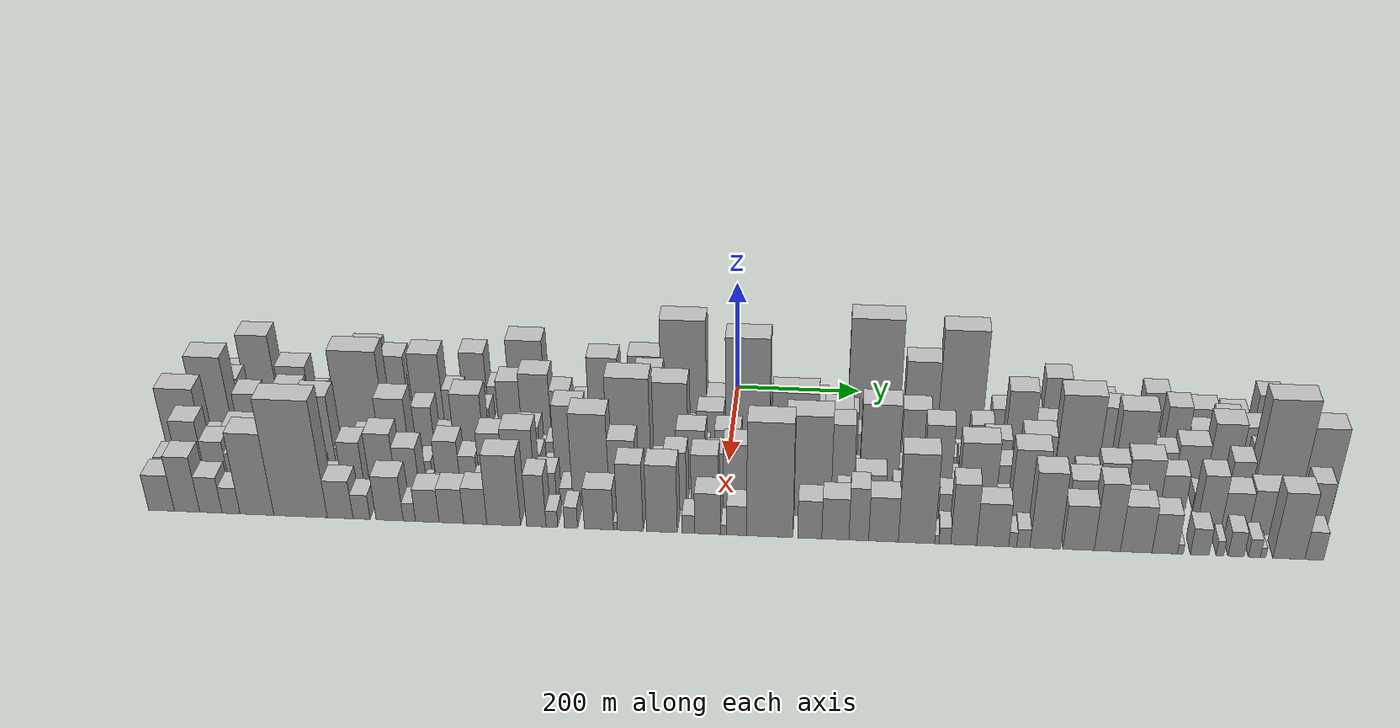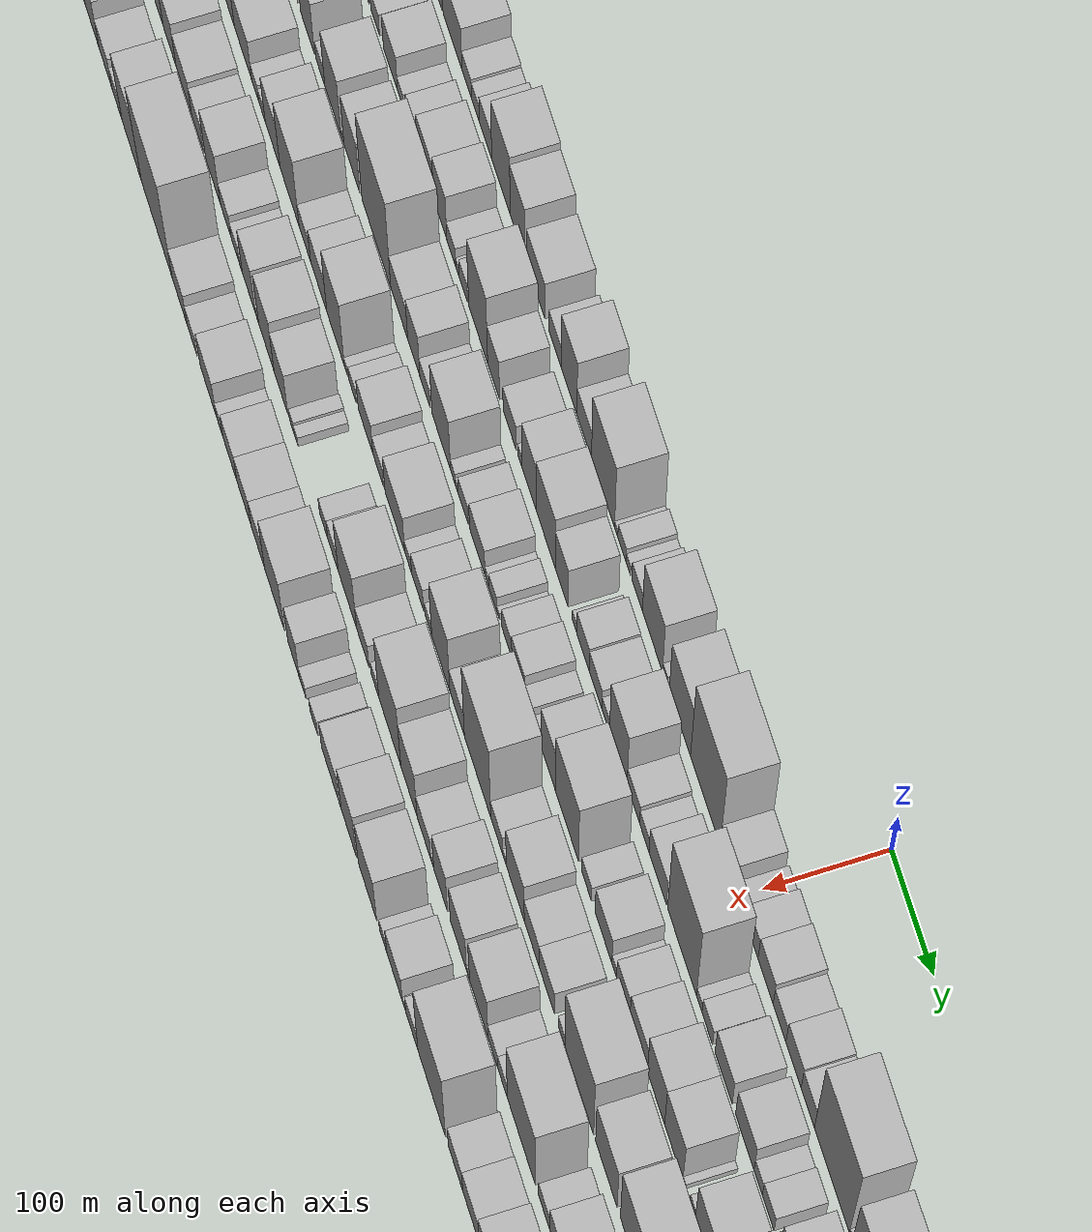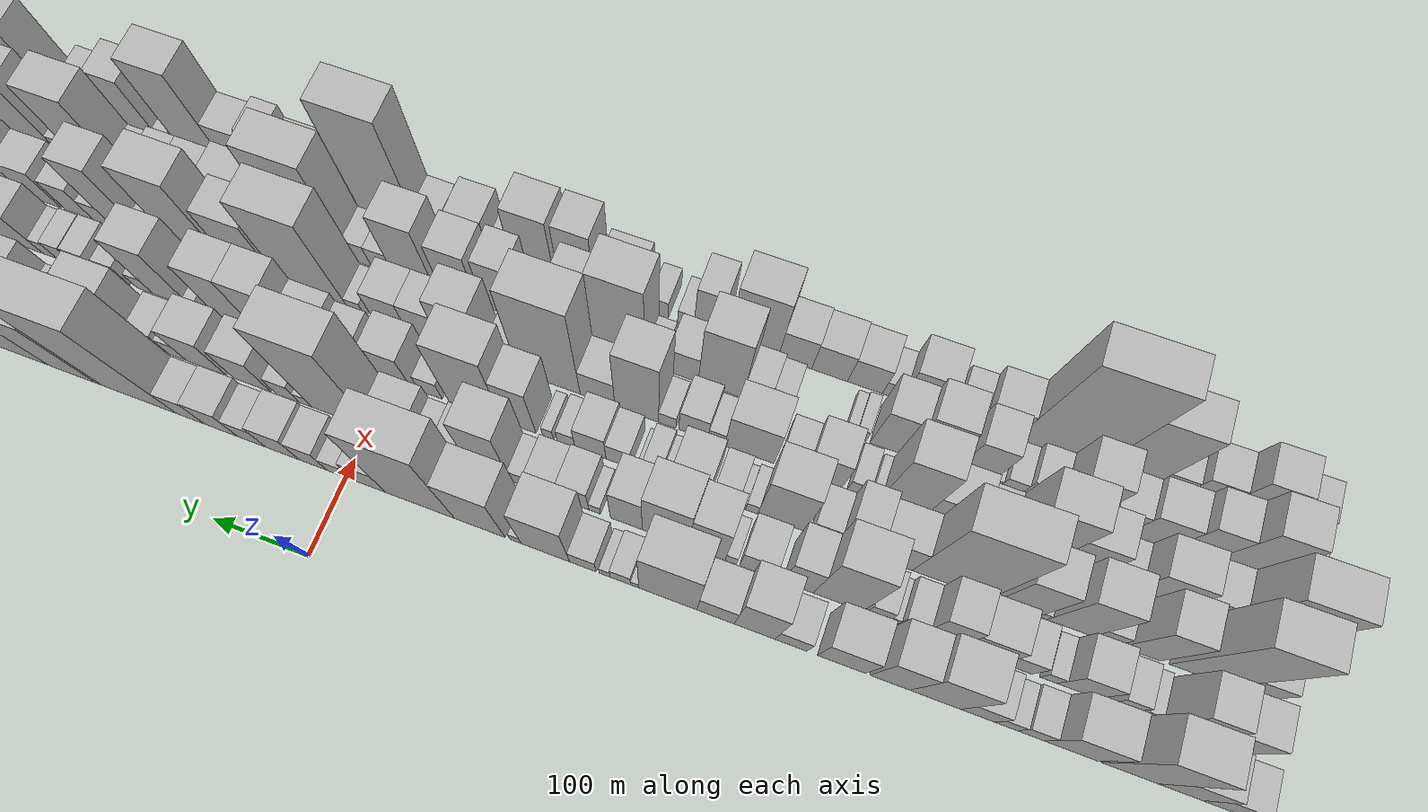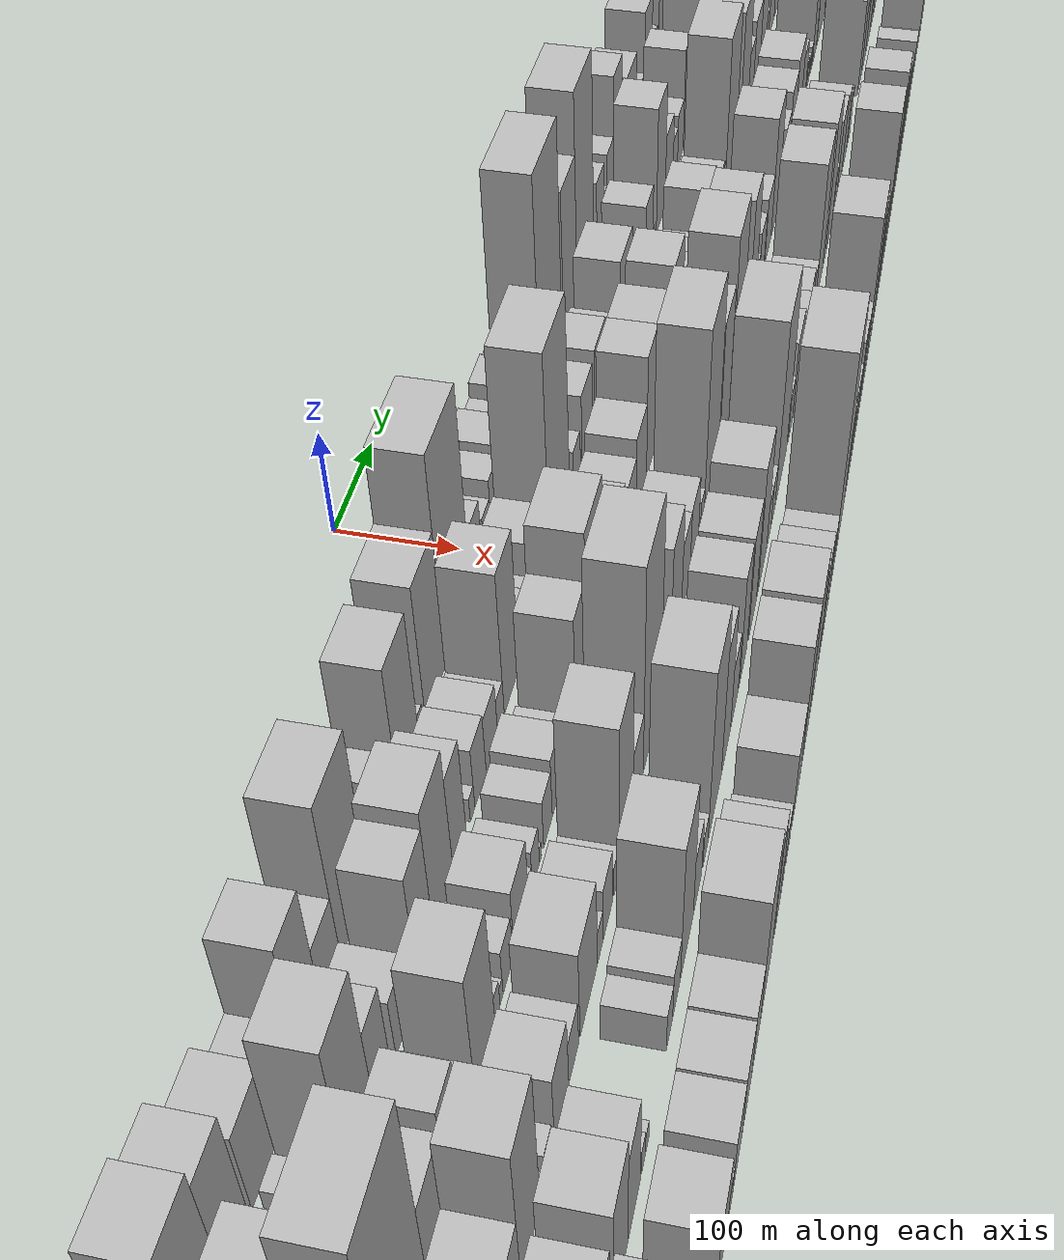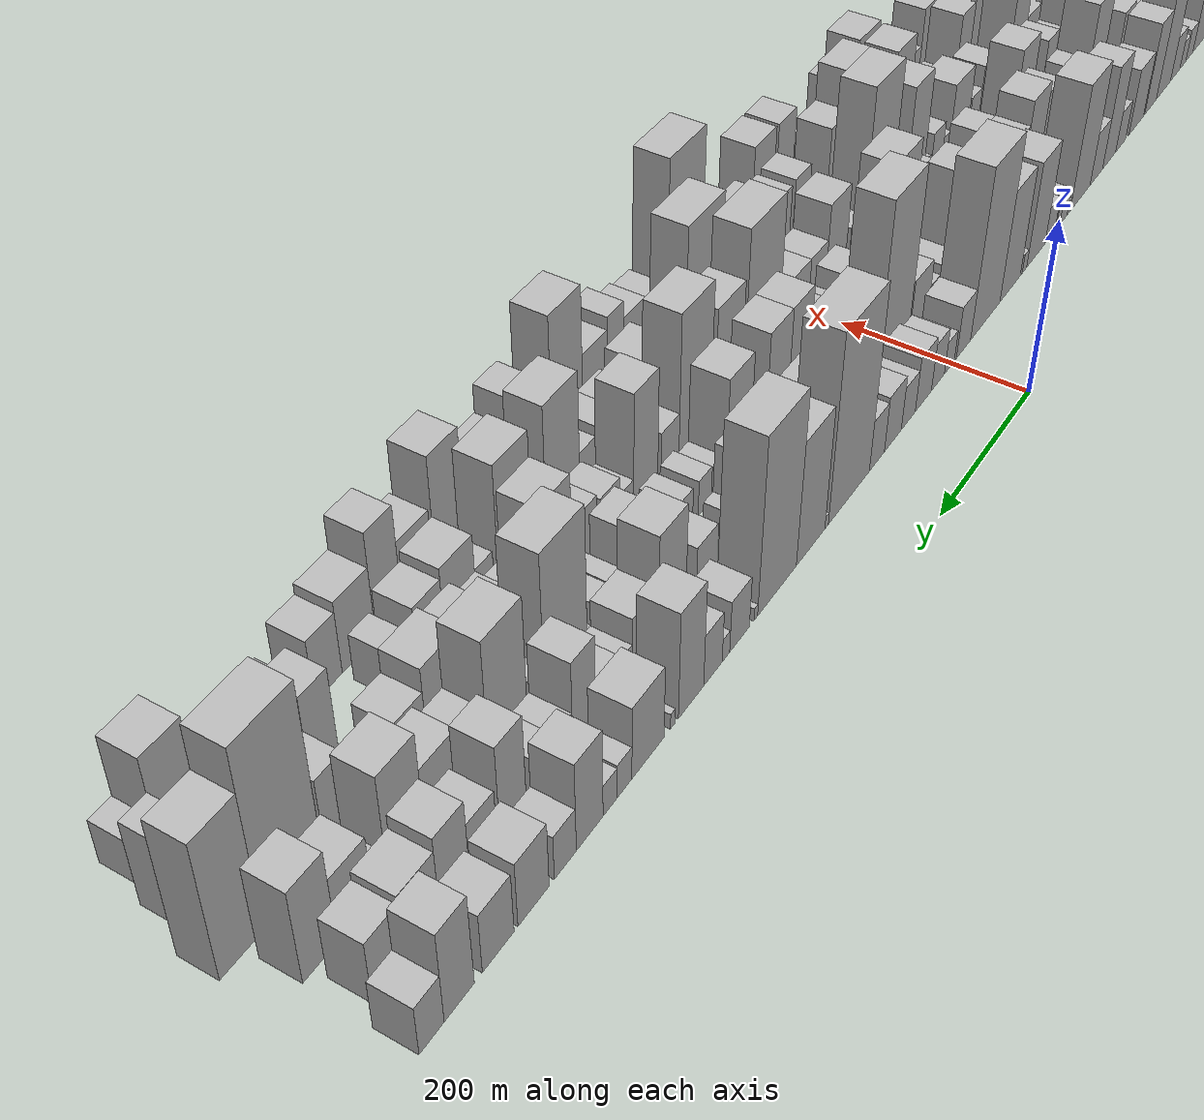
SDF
<sdf version="1.6">
 <world name="default">
  <scene>
   <sky><clouds><speed>12</speed></clouds></sky>
   <ambient>0.4 0.4 0.4 1</ambient>
   <background>0.7 0.7 0.7 1</background>
   <shadows>1</shadows>
  </scene>
  <gravity>0 0 -9.8066</gravity>
  <magnetic_field>6e-06 2.3e-05 -4.2e-05</magnetic_field>
  <physics default="0" name="default_physics" type="ode">
   <ode>
    <solver>
     <type>quick</type>
     <iters>10</iters>
     <sor>1.0</sor>
     <use_dynamic_moi_rescaling>0</use_dynamic_moi_rescaling>
    </solver>
    <constraints>
     <cfm>0</cfm>
     <erp>0.2</erp>
     <contact_max_correcting_vel>100</contact_max_correcting_vel>
     <contact_surface_layer>0.001</contact_surface_layer>
    </constraints>
   </ode>
   <max_step_size>0.004</max_step_size>
   <real_time_factor>1</real_time_factor>
   <real_time_update_rate>250</real_time_update_rate>
  </physics>
  <light name="sun" type="directional">
   <pose>0 0 10 0 0 0</pose>
   <diffuse>0.8 0.8 0.8 1</diffuse>
   <specular>0.2 0.2 0.2 1</specular>
   <attenuation>
    <range>1000</range>
    <constant>0.9</constant>
    <linear>0.01</linear>
    <quadratic>0.001</quadratic>
   </attenuation>
   <direction>-0.5 0.1 -0.9</direction>
  </light>
  <model name="building_1">
   <static>1</static>
   <pose>100.0000 -839.5826 0 0.000000 0.000000 0.000000</pose>
   <link name="link">
    <pose>0 0 28.50 0 0 0</pose>
    <collision name="collision"><geometry><box><size>40.0000 32.8347 57.0000</size></box></geometry></collision>
    <visual name="visual">
     <cast_shadows>0</cast_shadows>
     <geometry><box><size>40.0000 32.8347 57.0000</size></box></geometry>
     <material>
      <script>
       <uri>model://HANNAS_wall/materials/scripts</uri>
       <uri>model://HANNAS_wall/materials/textures</uri>
       <name>vrc/HANNAS_wall</name>
      </script>
     </material>
    </visual>
   </link>
  </model>
  <model name="building_2">
   <static>1</static>
   <pose>100.0000 -803.8127 0 0.000000 0.000000 0.000000</pose>
   <link name="link">
    <pose>0 0 37.50 0 0 0</pose>
    <collision name="collision"><geometry><box><size>40.0000 38.7050 75.0000</size></box></geometry></collision>
    <visual name="visual">
     <cast_shadows>0</cast_shadows>
     <geometry><box><size>40.0000 38.7050 75.0000</size></box></geometry>
     <material>
      <script>
       <uri>model://HANNAS_wall/materials/scripts</uri>
       <uri>model://HANNAS_wall/materials/textures</uri>
       <name>vrc/HANNAS_wall</name>
      </script>
     </material>
    </visual>
   </link>
  </model>
  <model name="building_3">
   <static>1</static>
   <pose>100.0000 -758.9218 0 0.000000 0.000000 0.000000</pose>
   <link name="link">
    <pose>0 0 73.50 0 0 0</pose>
    <collision name="collision"><geometry><box><size>40.0000 51.0769 147.0000</size></box></geometry></collision>
    <visual name="visual">
     <cast_shadows>0</cast_shadows>
     <geometry><box><size>40.0000 51.0769 147.0000</size></box></geometry>
     <material>
      <script>
       <uri>model://HANNAS_wall/materials/scripts</uri>
       <uri>model://HANNAS_wall/materials/textures</uri>
       <name>vrc/HANNAS_wall</name>
      </script>
     </material>
    </visual>
   </link>
  </model>
  <model name="building_4">
   <static>1</static>
   <pose>100.0000 -706.0290 0 0.000000 0.000000 0.000000</pose>
   <link name="link">
    <pose>0 0 45.00 0 0 0</pose>
    <collision name="collision"><geometry><box><size>40.0000 48.7086 90.0000</size></box></geometry></collision>
    <visual name="visual">
     <cast_shadows>0</cast_shadows>
     <geometry><box><size>40.0000 48.7086 90.0000</size></box></geometry>
     <material>
      <script>
       <uri>model://HANNAS_wall/materials/scripts</uri>
       <uri>model://HANNAS_wall/materials/textures</uri>
       <name>vrc/HANNAS_wall</name>
      </script>
     </material>
    </visual>
   </link>
  </model>
  <model name="building_5">
   <static>1</static>
   <pose>100.0000 -669.4987 0 0.000000 0.000000 0.000000</pose>
   <link name="link">
    <pose>0 0 21.00 0 0 0</pose>
    <collision name="collision"><geometry><box><size>40.0000 24.3519 42.0000</size></box></geometry></collision>
    <visual name="visual">
     <cast_shadows>0</cast_shadows>
     <geometry><box><size>40.0000 24.3519 42.0000</size></box></geometry>
     <material>
      <script>
       <uri>model://HANNAS_wall/materials/scripts</uri>
       <uri>model://HANNAS_wall/materials/textures</uri>
       <name>vrc/HANNAS_wall</name>
      </script>
     </material>
    </visual>
   </link>
  </model>
  <model name="building_6">
   <static>1</static>
   <pose>100.0000 -647.2073 0 0.000000 0.000000 0.000000</pose>
   <link name="link">
    <pose>0 0 18.00 0 0 0</pose>
    <collision name="collision"><geometry><box><size>40.0000 20.2310 36.0000</size></box></geometry></collision>
    <visual name="visual">
     <cast_shadows>0</cast_shadows>
     <geometry><box><size>40.0000 20.2310 36.0000</size></box></geometry>
     <material>
      <script>
       <uri>model://HANNAS_wall/materials/scripts</uri>
       <uri>model://HANNAS_wall/materials/textures</uri>
       <name>vrc/HANNAS_wall</name>
      </script>
     </material>
    </visual>
   </link>
  </model>
  <model name="building_7">
   <static>1</static>
   <pose>100.0000 -621.3473 0 0.000000 0.000000 0.000000</pose>
   <link name="link">
    <pose>0 0 28.50 0 0 0</pose>
    <collision name="collision"><geometry><box><size>40.0000 31.4890 57.0000</size></box></geometry></collision>
    <visual name="visual">
     <cast_shadows>0</cast_shadows>
     <geometry><box><size>40.0000 31.4890 57.0000</size></box></geometry>
     <material>
      <script>
       <uri>model://HANNAS_wall/materials/scripts</uri>
       <uri>model://HANNAS_wall/materials/textures</uri>
       <name>vrc/HANNAS_wall</name>
      </script>
     </material>
    </visual>
   </link>
  </model>
  <model name="building_8">
   <static>1</static>
   <pose>100.0000 -582.1317 0 0.000000 0.000000 0.000000</pose>
   <link name="link">
    <pose>0 0 66.00 0 0 0</pose>
    <collision name="collision"><geometry><box><size>40.0000 46.9421 132.0000</size></box></geometry></collision>
    <visual name="visual">
     <cast_shadows>0</cast_shadows>
     <geometry><box><size>40.0000 46.9421 132.0000</size></box></geometry>
     <material>
      <script>
       <uri>model://HANNAS_wall/materials/scripts</uri>
       <uri>model://HANNAS_wall/materials/textures</uri>
       <name>vrc/HANNAS_wall</name>
      </script>
     </material>
    </visual>
   </link>
  </model>
  <model name="building_9">
   <static>1</static>
   <pose>100.0000 -540.0095 0 0.000000 0.000000 0.000000</pose>
   <link name="link">
    <pose>0 0 58.50 0 0 0</pose>
    <collision name="collision"><geometry><box><size>40.0000 37.3023 117.0000</size></box></geometry></collision>
    <visual name="visual">
     <cast_shadows>0</cast_shadows>
     <geometry><box><size>40.0000 37.3023 117.0000</size></box></geometry>
     <material>
      <script>
       <uri>model://HANNAS_wall/materials/scripts</uri>
       <uri>model://HANNAS_wall/materials/textures</uri>
       <name>vrc/HANNAS_wall</name>
      </script>
     </material>
    </visual>
   </link>
  </model>
  <model name="building_10">
   <static>1</static>
   <pose>100.0000 -494.5107 0 0.000000 0.000000 0.000000</pose>
   <link name="link">
    <pose>0 0 42.00 0 0 0</pose>
    <collision name="collision"><geometry><box><size>40.0000 45.6954 84.0000</size></box></geometry></collision>
    <visual name="visual">
     <cast_shadows>0</cast_shadows>
     <geometry><box><size>40.0000 45.6954 84.0000</size></box></geometry>
     <material>
      <script>
       <uri>model://HANNAS_wall/materials/scripts</uri>
       <uri>model://HANNAS_wall/materials/textures</uri>
       <name>vrc/HANNAS_wall</name>
      </script>
     </material>
    </visual>
   </link>
  </model>
  <model name="building_11">
   <static>1</static>
   <pose>100.0000 -446.4359 0 0.000000 0.000000 0.000000</pose>
   <link name="link">
    <pose>0 0 25.50 0 0 0</pose>
    <collision name="collision"><geometry><box><size>40.0000 30.4542 51.0000</size></box></geometry></collision>
    <visual name="visual">
     <cast_shadows>0</cast_shadows>
     <geometry><box><size>40.0000 30.4542 51.0000</size></box></geometry>
     <material>
      <script>
       <uri>model://HANNAS_wall/materials/scripts</uri>
       <uri>model://HANNAS_wall/materials/textures</uri>
       <name>vrc/HANNAS_wall</name>
      </script>
     </material>
    </visual>
   </link>
  </model>
  <model name="building_12">
   <static>1</static>
   <pose>100.0000 -411.5022 0 0.000000 0.000000 0.000000</pose>
   <link name="link">
    <pose>0 0 64.50 0 0 0</pose>
    <collision name="collision"><geometry><box><size>40.0000 39.4130 129.0000</size></box></geometry></collision>
    <visual name="visual">
     <cast_shadows>0</cast_shadows>
     <geometry><box><size>40.0000 39.4130 129.0000</size></box></geometry>
     <material>
      <script>
       <uri>model://HANNAS_wall/materials/scripts</uri>
       <uri>model://HANNAS_wall/materials/textures</uri>
       <name>vrc/HANNAS_wall</name>
      </script>
     </material>
    </visual>
   </link>
  </model>
  <model name="building_13">
   <static>1</static>
   <pose>100.0000 -373.6717 0 0.000000 0.000000 0.000000</pose>
   <link name="link">
    <pose>0 0 33.00 0 0 0</pose>
    <collision name="collision"><geometry><box><size>40.0000 36.2482 66.0000</size></box></geometry></collision>
    <visual name="visual">
     <cast_shadows>0</cast_shadows>
     <geometry><box><size>40.0000 36.2482 66.0000</size></box></geometry>
     <material>
      <script>
       <uri>model://HANNAS_wall/materials/scripts</uri>
       <uri>model://HANNAS_wall/materials/textures</uri>
       <name>vrc/HANNAS_wall</name>
      </script>
     </material>
    </visual>
   </link>
  </model>
  <model name="building_14">
   <static>1</static>
   <pose>100.0000 -327.0706 0 0.000000 0.000000 0.000000</pose>
   <link name="link">
    <pose>0 0 78.00 0 0 0</pose>
    <collision name="collision"><geometry><box><size>40.0000 56.9540 156.0000</size></box></geometry></collision>
    <visual name="visual">
     <cast_shadows>0</cast_shadows>
     <geometry><box><size>40.0000 56.9540 156.0000</size></box></geometry>
     <material>
      <script>
       <uri>model://HANNAS_wall/materials/scripts</uri>
       <uri>model://HANNAS_wall/materials/textures</uri>
       <name>vrc/HANNAS_wall</name>
      </script>
     </material>
    </visual>
   </link>
  </model>
  <model name="building_15">
   <static>1</static>
   <pose>100.0000 -294.5431 0 0.000000 0.000000 0.000000</pose>
   <link name="link">
    <pose>0 0 9.00 0 0 0</pose>
    <collision name="collision"><geometry><box><size>40.0000 8.1011 18.0000</size></box></geometry></collision>
    <visual name="visual">
     <cast_shadows>0</cast_shadows>
     <geometry><box><size>40.0000 8.1011 18.0000</size></box></geometry>
     <material>
      <script>
       <uri>model://HANNAS_wall/materials/scripts</uri>
       <uri>model://HANNAS_wall/materials/textures</uri>
       <name>vrc/HANNAS_wall</name>
      </script>
     </material>
    </visual>
   </link>
  </model>
  <model name="building_16">
   <static>1</static>
   <pose>100.0000 -280.3721 0 0.000000 0.000000 0.000000</pose>
   <link name="link">
    <pose>0 0 18.00 0 0 0</pose>
    <collision name="collision"><geometry><box><size>40.0000 20.2410 36.0000</size></box></geometry></collision>
    <visual name="visual">
     <cast_shadows>0</cast_shadows>
     <geometry><box><size>40.0000 20.2410 36.0000</size></box></geometry>
     <material>
      <script>
       <uri>model://HANNAS_wall/materials/scripts</uri>
       <uri>model://HANNAS_wall/materials/textures</uri>
       <name>vrc/HANNAS_wall</name>
      </script>
     </material>
    </visual>
   </link>
  </model>
  <model name="building_17">
   <static>1</static>
   <pose>100.0000 -264.9043 0 0.000000 0.000000 0.000000</pose>
   <link name="link">
    <pose>0 0 12.00 0 0 0</pose>
    <collision name="collision"><geometry><box><size>40.0000 10.6945 24.0000</size></box></geometry></collision>
    <visual name="visual">
     <cast_shadows>0</cast_shadows>
     <geometry><box><size>40.0000 10.6945 24.0000</size></box></geometry>
     <material>
      <script>
       <uri>model://HANNAS_wall/materials/scripts</uri>
       <uri>model://HANNAS_wall/materials/textures</uri>
       <name>vrc/HANNAS_wall</name>
      </script>
     </material>
    </visual>
   </link>
  </model>
  <model name="building_18">
   <static>1</static>
   <pose>100.0000 -243.2661 0 0.000000 0.000000 0.000000</pose>
   <link name="link">
    <pose>0 0 22.50 0 0 0</pose>
    <collision name="collision"><geometry><box><size>40.0000 26.5818 45.0000</size></box></geometry></collision>
    <visual name="visual">
     <cast_shadows>0</cast_shadows>
     <geometry><box><size>40.0000 26.5818 45.0000</size></box></geometry>
     <material>
      <script>
       <uri>model://HANNAS_wall/materials/scripts</uri>
       <uri>model://HANNAS_wall/materials/textures</uri>
       <name>vrc/HANNAS_wall</name>
      </script>
     </material>
    </visual>
   </link>
  </model>
  <model name="building_19">
   <static>1</static>
   <pose>100.0000 -205.5943 0 0.000000 0.000000 0.000000</pose>
   <link name="link">
    <pose>0 0 64.50 0 0 0</pose>
    <collision name="collision"><geometry><box><size>40.0000 48.7619 129.0000</size></box></geometry></collision>
    <visual name="visual">
     <cast_shadows>0</cast_shadows>
     <geometry><box><size>40.0000 48.7619 129.0000</size></box></geometry>
     <material>
      <script>
       <uri>model://HANNAS_wall/materials/scripts</uri>
       <uri>model://HANNAS_wall/materials/textures</uri>
       <name>vrc/HANNAS_wall</name>
      </script>
     </material>
    </visual>
   </link>
  </model>
  <model name="building_20">
   <static>1</static>
   <pose>100.0000 -175.5670 0 0.000000 0.000000 0.000000</pose>
   <link name="link">
    <pose>0 0 12.00 0 0 0</pose>
    <collision name="collision"><geometry><box><size>40.0000 11.2925 24.0000</size></box></geometry></collision>
    <visual name="visual">
     <cast_shadows>0</cast_shadows>
     <geometry><box><size>40.0000 11.2925 24.0000</size></box></geometry>
     <material>
      <script>
       <uri>model://HANNAS_wall/materials/scripts</uri>
       <uri>model://HANNAS_wall/materials/textures</uri>
       <name>vrc/HANNAS_wall</name>
      </script>
     </material>
    </visual>
   </link>
  </model>
  <model name="building_21">
   <static>1</static>
   <pose>100.0000 -139.0701 0 0.000000 0.000000 0.000000</pose>
   <link name="link">
    <pose>0 0 67.50 0 0 0</pose>
    <collision name="collision"><geometry><box><size>40.0000 51.7013 135.0000</size></box></geometry></collision>
    <visual name="visual">
     <cast_shadows>0</cast_shadows>
     <geometry><box><size>40.0000 51.7013 135.0000</size></box></geometry>
     <material>
      <script>
       <uri>model://HANNAS_wall/materials/scripts</uri>
       <uri>model://HANNAS_wall/materials/textures</uri>
       <name>vrc/HANNAS_wall</name>
      </script>
     </material>
    </visual>
   </link>
  </model>
  <model name="building_22">
   <static>1</static>
   <pose>100.0000 -77.4613 0 0.000000 0.000000 0.000000</pose>
   <link name="link">
    <pose>0 0 102.00 0 0 0</pose>
    <collision name="collision"><geometry><box><size>40.0000 71.5163 204.0000</size></box></geometry></collision>
    <visual name="visual">
     <cast_shadows>0</cast_shadows>
     <geometry><box><size>40.0000 71.5163 204.0000</size></box></geometry>
     <material>
      <script>
       <uri>model://HANNAS_wall/materials/scripts</uri>
       <uri>model://HANNAS_wall/materials/textures</uri>
       <name>vrc/HANNAS_wall</name>
      </script>
     </material>
    </visual>
   </link>
  </model>
  <model name="building_23">
   <static>1</static>
   <pose>100.0000 -24.9427 0 0.000000 0.000000 0.000000</pose>
   <link name="link">
    <pose>0 0 31.50 0 0 0</pose>
    <collision name="collision"><geometry><box><size>40.0000 33.5210 63.0000</size></box></geometry></collision>
    <visual name="visual">
     <cast_shadows>0</cast_shadows>
     <geometry><box><size>40.0000 33.5210 63.0000</size></box></geometry>
     <material>
      <script>
       <uri>model://HANNAS_wall/materials/scripts</uri>
       <uri>model://HANNAS_wall/materials/textures</uri>
       <name>vrc/HANNAS_wall</name>
      </script>
     </material>
    </visual>
   </link>
  </model>
  <model name="building_24">
   <static>1</static>
   <pose>100.0000 8.2083 0 0.000000 0.000000 0.000000</pose>
   <link name="link">
    <pose>0 0 19.50 0 0 0</pose>
    <collision name="collision"><geometry><box><size>40.0000 22.7810 39.0000</size></box></geometry></collision>
    <visual name="visual">
     <cast_shadows>0</cast_shadows>
     <geometry><box><size>40.0000 22.7810 39.0000</size></box></geometry>
     <material>
      <script>
       <uri>model://HANNAS_wall/materials/scripts</uri>
       <uri>model://HANNAS_wall/materials/textures</uri>
       <name>vrc/HANNAS_wall</name>
      </script>
     </material>
    </visual>
   </link>
  </model>
  <model name="building_25">
   <static>1</static>
   <pose>100.0000 34.2007 0 0.000000 0.000000 0.000000</pose>
   <link name="link">
    <pose>0 0 28.50 0 0 0</pose>
    <collision name="collision"><geometry><box><size>40.0000 29.2038 57.0000</size></box></geometry></collision>
    <visual name="visual">
     <cast_shadows>0</cast_shadows>
     <geometry><box><size>40.0000 29.2038 57.0000</size></box></geometry>
     <material>
      <script>
       <uri>model://HANNAS_wall/materials/scripts</uri>
       <uri>model://HANNAS_wall/materials/textures</uri>
       <name>vrc/HANNAS_wall</name>
      </script>
     </material>
    </visual>
   </link>
  </model>
  <model name="building_26">
   <static>1</static>
   <pose>100.0000 66.7584 0 0.000000 0.000000 0.000000</pose>
   <link name="link">
    <pose>0 0 33.00 0 0 0</pose>
    <collision name="collision"><geometry><box><size>40.0000 35.9115 66.0000</size></box></geometry></collision>
    <visual name="visual">
     <cast_shadows>0</cast_shadows>
     <geometry><box><size>40.0000 35.9115 66.0000</size></box></geometry>
     <material>
      <script>
       <uri>model://HANNAS_wall/materials/scripts</uri>
       <uri>model://HANNAS_wall/materials/textures</uri>
       <name>vrc/HANNAS_wall</name>
      </script>
     </material>
    </visual>
   </link>
  </model>
  <model name="building_27">
   <static>1</static>
   <pose>100.0000 99.8125 0 0.000000 0.000000 0.000000</pose>
   <link name="link">
    <pose>0 0 25.50 0 0 0</pose>
    <collision name="collision"><geometry><box><size>40.0000 30.1968 51.0000</size></box></geometry></collision>
    <visual name="visual">
     <cast_shadows>0</cast_shadows>
     <geometry><box><size>40.0000 30.1968 51.0000</size></box></geometry>
     <material>
      <script>
       <uri>model://HANNAS_wall/materials/scripts</uri>
       <uri>model://HANNAS_wall/materials/textures</uri>
       <name>vrc/HANNAS_wall</name>
      </script>
     </material>
    </visual>
   </link>
  </model>
  <model name="building_28">
   <static>1</static>
   <pose>100.0000 132.8469 0 0.000000 0.000000 0.000000</pose>
   <link name="link">
    <pose>0 0 33.00 0 0 0</pose>
    <collision name="collision"><geometry><box><size>40.0000 35.8721 66.0000</size></box></geometry></collision>
    <visual name="visual">
     <cast_shadows>0</cast_shadows>
     <geometry><box><size>40.0000 35.8721 66.0000</size></box></geometry>
     <material>
      <script>
       <uri>model://HANNAS_wall/materials/scripts</uri>
       <uri>model://HANNAS_wall/materials/textures</uri>
       <name>vrc/HANNAS_wall</name>
      </script>
     </material>
    </visual>
   </link>
  </model>
  <model name="building_29">
   <static>1</static>
   <pose>100.0000 166.3247 0 0.000000 0.000000 0.000000</pose>
   <link name="link">
    <pose>0 0 30.00 0 0 0</pose>
    <collision name="collision"><geometry><box><size>40.0000 31.0834 60.0000</size></box></geometry></collision>
    <visual name="visual">
     <cast_shadows>0</cast_shadows>
     <geometry><box><size>40.0000 31.0834 60.0000</size></box></geometry>
     <material>
      <script>
       <uri>model://HANNAS_wall/materials/scripts</uri>
       <uri>model://HANNAS_wall/materials/textures</uri>
       <name>vrc/HANNAS_wall</name>
      </script>
     </material>
    </visual>
   </link>
  </model>
  <model name="building_30">
   <static>1</static>
   <pose>100.0000 222.6896 0 0.000000 0.000000 0.000000</pose>
   <link name="link">
    <pose>0 0 109.50 0 0 0</pose>
    <collision name="collision"><geometry><box><size>40.0000 81.6465 219.0000</size></box></geometry></collision>
    <visual name="visual">
     <cast_shadows>0</cast_shadows>
     <geometry><box><size>40.0000 81.6465 219.0000</size></box></geometry>
     <material>
      <script>
       <uri>model://HANNAS_wall/materials/scripts</uri>
       <uri>model://HANNAS_wall/materials/textures</uri>
       <name>vrc/HANNAS_wall</name>
      </script>
     </material>
    </visual>
   </link>
  </model>
  <model name="building_31">
   <static>1</static>
   <pose>100.0000 266.8751 0 0.000000 0.000000 0.000000</pose>
   <link name="link">
    <pose>0 0 7.50 0 0 0</pose>
    <collision name="collision"><geometry><box><size>40.0000 6.7245 15.0000</size></box></geometry></collision>
    <visual name="visual">
     <cast_shadows>0</cast_shadows>
     <geometry><box><size>40.0000 6.7245 15.0000</size></box></geometry>
     <material>
      <script>
       <uri>model://HANNAS_wall/materials/scripts</uri>
       <uri>model://HANNAS_wall/materials/textures</uri>
       <name>vrc/HANNAS_wall</name>
      </script>
     </material>
    </visual>
   </link>
  </model>
  <model name="building_32">
   <static>1</static>
   <pose>100.0000 297.1430 0 0.000000 0.000000 0.000000</pose>
   <link name="link">
    <pose>0 0 72.00 0 0 0</pose>
    <collision name="collision"><geometry><box><size>40.0000 53.8115 144.0000</size></box></geometry></collision>
    <visual name="visual">
     <cast_shadows>0</cast_shadows>
     <geometry><box><size>40.0000 53.8115 144.0000</size></box></geometry>
     <material>
      <script>
       <uri>model://HANNAS_wall/materials/scripts</uri>
       <uri>model://HANNAS_wall/materials/textures</uri>
       <name>vrc/HANNAS_wall</name>
      </script>
     </material>
    </visual>
   </link>
  </model>
  <model name="building_33">
   <static>1</static>
   <pose>100.0000 358.9259 0 0.000000 0.000000 0.000000</pose>
   <link name="link">
    <pose>0 0 102.00 0 0 0</pose>
    <collision name="collision"><geometry><box><size>40.0000 69.7542 204.0000</size></box></geometry></collision>
    <visual name="visual">
     <cast_shadows>0</cast_shadows>
     <geometry><box><size>40.0000 69.7542 204.0000</size></box></geometry>
     <material>
      <script>
       <uri>model://HANNAS_wall/materials/scripts</uri>
       <uri>model://HANNAS_wall/materials/textures</uri>
       <name>vrc/HANNAS_wall</name>
      </script>
     </material>
    </visual>
   </link>
  </model>
  <model name="building_34">
   <static>1</static>
   <pose>100.0000 396.9656 0 0.000000 0.000000 0.000000</pose>
   <link name="link">
    <pose>0 0 7.50 0 0 0</pose>
    <collision name="collision"><geometry><box><size>40.0000 6.3254 15.0000</size></box></geometry></collision>
    <visual name="visual">
     <cast_shadows>0</cast_shadows>
     <geometry><box><size>40.0000 6.3254 15.0000</size></box></geometry>
     <material>
      <script>
       <uri>model://HANNAS_wall/materials/scripts</uri>
       <uri>model://HANNAS_wall/materials/textures</uri>
       <name>vrc/HANNAS_wall</name>
      </script>
     </material>
    </visual>
   </link>
  </model>
  <model name="building_35">
   <static>1</static>
   <pose>100.0000 425.0530 0 0.000000 0.000000 0.000000</pose>
   <link name="link">
    <pose>0 0 30.00 0 0 0</pose>
    <collision name="collision"><geometry><box><size>40.0000 33.8494 60.0000</size></box></geometry></collision>
    <visual name="visual">
     <cast_shadows>0</cast_shadows>
     <geometry><box><size>40.0000 33.8494 60.0000</size></box></geometry>
     <material>
      <script>
       <uri>model://HANNAS_wall/materials/scripts</uri>
       <uri>model://HANNAS_wall/materials/textures</uri>
       <name>vrc/HANNAS_wall</name>
      </script>
     </material>
    </visual>
   </link>
  </model>
  <model name="building_36">
   <static>1</static>
   <pose>100.0000 448.3234 0 0.000000 0.000000 0.000000</pose>
   <link name="link">
    <pose>0 0 13.50 0 0 0</pose>
    <collision name="collision"><geometry><box><size>40.0000 12.6913 27.0000</size></box></geometry></collision>
    <visual name="visual">
     <cast_shadows>0</cast_shadows>
     <geometry><box><size>40.0000 12.6913 27.0000</size></box></geometry>
     <material>
      <script>
       <uri>model://HANNAS_wall/materials/scripts</uri>
       <uri>model://HANNAS_wall/materials/textures</uri>
       <name>vrc/HANNAS_wall</name>
      </script>
     </material>
    </visual>
   </link>
  </model>
  <model name="building_37">
   <static>1</static>
   <pose>100.0000 469.9412 0 0.000000 0.000000 0.000000</pose>
   <link name="link">
    <pose>0 0 30.00 0 0 0</pose>
    <collision name="collision"><geometry><box><size>40.0000 30.5444 60.0000</size></box></geometry></collision>
    <visual name="visual">
     <cast_shadows>0</cast_shadows>
     <geometry><box><size>40.0000 30.5444 60.0000</size></box></geometry>
     <material>
      <script>
       <uri>model://HANNAS_wall/materials/scripts</uri>
       <uri>model://HANNAS_wall/materials/textures</uri>
       <name>vrc/HANNAS_wall</name>
      </script>
     </material>
    </visual>
   </link>
  </model>
  <model name="building_38">
   <static>1</static>
   <pose>100.0000 505.5566 0 0.000000 0.000000 0.000000</pose>
   <link name="link">
    <pose>0 0 61.50 0 0 0</pose>
    <collision name="collision"><geometry><box><size>40.0000 40.6864 123.0000</size></box></geometry></collision>
    <visual name="visual">
     <cast_shadows>0</cast_shadows>
     <geometry><box><size>40.0000 40.6864 123.0000</size></box></geometry>
     <material>
      <script>
       <uri>model://HANNAS_wall/materials/scripts</uri>
       <uri>model://HANNAS_wall/materials/textures</uri>
       <name>vrc/HANNAS_wall</name>
      </script>
     </material>
    </visual>
   </link>
  </model>
  <model name="building_39">
   <static>1</static>
   <pose>100.0000 534.6174 0 0.000000 0.000000 0.000000</pose>
   <link name="link">
    <pose>0 0 9.00 0 0 0</pose>
    <collision name="collision"><geometry><box><size>40.0000 7.4353 18.0000</size></box></geometry></collision>
    <visual name="visual">
     <cast_shadows>0</cast_shadows>
     <geometry><box><size>40.0000 7.4353 18.0000</size></box></geometry>
     <material>
      <script>
       <uri>model://HANNAS_wall/materials/scripts</uri>
       <uri>model://HANNAS_wall/materials/textures</uri>
       <name>vrc/HANNAS_wall</name>
      </script>
     </material>
    </visual>
   </link>
  </model>
  <model name="building_40">
   <static>1</static>
   <pose>100.0000 572.8481 0 0.000000 0.000000 0.000000</pose>
   <link name="link">
    <pose>0 0 42.00 0 0 0</pose>
    <collision name="collision"><geometry><box><size>40.0000 49.0260 84.0000</size></box></geometry></collision>
    <visual name="visual">
     <cast_shadows>0</cast_shadows>
     <geometry><box><size>40.0000 49.0260 84.0000</size></box></geometry>
     <material>
      <script>
       <uri>model://HANNAS_wall/materials/scripts</uri>
       <uri>model://HANNAS_wall/materials/textures</uri>
       <name>vrc/HANNAS_wall</name>
      </script>
     </material>
    </visual>
   </link>
  </model>
  <model name="building_41">
   <static>1</static>
   <pose>100.0000 608.1299 0 0.000000 0.000000 0.000000</pose>
   <link name="link">
    <pose>0 0 19.50 0 0 0</pose>
    <collision name="collision"><geometry><box><size>40.0000 21.5375 39.0000</size></box></geometry></collision>
    <visual name="visual">
     <cast_shadows>0</cast_shadows>
     <geometry><box><size>40.0000 21.5375 39.0000</size></box></geometry>
     <material>
      <script>
       <uri>model://HANNAS_wall/materials/scripts</uri>
       <uri>model://HANNAS_wall/materials/textures</uri>
       <name>vrc/HANNAS_wall</name>
      </script>
     </material>
    </visual>
   </link>
  </model>
  <model name="building_42">
   <static>1</static>
   <pose>100.0000 629.2807 0 0.000000 0.000000 0.000000</pose>
   <link name="link">
    <pose>0 0 18.00 0 0 0</pose>
    <collision name="collision"><geometry><box><size>40.0000 20.7642 36.0000</size></box></geometry></collision>
    <visual name="visual">
     <cast_shadows>0</cast_shadows>
     <geometry><box><size>40.0000 20.7642 36.0000</size></box></geometry>
     <material>
      <script>
       <uri>model://HANNAS_wall/materials/scripts</uri>
       <uri>model://HANNAS_wall/materials/textures</uri>
       <name>vrc/HANNAS_wall</name>
      </script>
     </material>
    </visual>
   </link>
  </model>
  <model name="building_43">
   <static>1</static>
   <pose>100.0000 658.6435 0 0.000000 0.000000 0.000000</pose>
   <link name="link">
    <pose>0 0 51.00 0 0 0</pose>
    <collision name="collision"><geometry><box><size>40.0000 37.9613 102.0000</size></box></geometry></collision>
    <visual name="visual">
     <cast_shadows>0</cast_shadows>
     <geometry><box><size>40.0000 37.9613 102.0000</size></box></geometry>
     <material>
      <script>
       <uri>model://HANNAS_wall/materials/scripts</uri>
       <uri>model://HANNAS_wall/materials/textures</uri>
       <name>vrc/HANNAS_wall</name>
      </script>
     </material>
    </visual>
   </link>
  </model>
  <model name="building_44">
   <static>1</static>
   <pose>100.0000 692.8332 0 0.000000 0.000000 0.000000</pose>
   <link name="link">
    <pose>0 0 25.50 0 0 0</pose>
    <collision name="collision"><geometry><box><size>40.0000 30.4181 51.0000</size></box></geometry></collision>
    <visual name="visual">
     <cast_shadows>0</cast_shadows>
     <geometry><box><size>40.0000 30.4181 51.0000</size></box></geometry>
     <material>
      <script>
       <uri>model://HANNAS_wall/materials/scripts</uri>
       <uri>model://HANNAS_wall/materials/textures</uri>
       <name>vrc/HANNAS_wall</name>
      </script>
     </material>
    </visual>
   </link>
  </model>
  <model name="building_45">
   <static>1</static>
   <pose>100.0000 735.8056 0 0.000000 0.000000 0.000000</pose>
   <link name="link">
    <pose>0 0 37.50 0 0 0</pose>
    <collision name="collision"><geometry><box><size>40.0000 41.5267 75.0000</size></box></geometry></collision>
    <visual name="visual">
     <cast_shadows>0</cast_shadows>
     <geometry><box><size>40.0000 41.5267 75.0000</size></box></geometry>
     <material>
      <script>
       <uri>model://HANNAS_wall/materials/scripts</uri>
       <uri>model://HANNAS_wall/materials/textures</uri>
       <name>vrc/HANNAS_wall</name>
      </script>
     </material>
    </visual>
   </link>
  </model>
  <model name="building_46">
   <static>1</static>
   <pose>100.0000 781.8442 0 0.000000 0.000000 0.000000</pose>
   <link name="link">
    <pose>0 0 34.50 0 0 0</pose>
    <collision name="collision"><geometry><box><size>40.0000 40.5506 69.0000</size></box></geometry></collision>
    <visual name="visual">
     <cast_shadows>0</cast_shadows>
     <geometry><box><size>40.0000 40.5506 69.0000</size></box></geometry>
     <material>
      <script>
       <uri>model://HANNAS_wall/materials/scripts</uri>
       <uri>model://HANNAS_wall/materials/textures</uri>
       <name>vrc/HANNAS_wall</name>
      </script>
     </material>
    </visual>
   </link>
  </model>
  <model name="building_47">
   <static>1</static>
   <pose>100.0000 830.5040 0 0.000000 0.000000 0.000000</pose>
   <link name="link">
    <pose>0 0 52.50 0 0 0</pose>
    <collision name="collision"><geometry><box><size>40.0000 36.7689 105.0000</size></box></geometry></collision>
    <visual name="visual">
     <cast_shadows>0</cast_shadows>
     <geometry><box><size>40.0000 36.7689 105.0000</size></box></geometry>
     <material>
      <script>
       <uri>model://HANNAS_wall/materials/scripts</uri>
       <uri>model://HANNAS_wall/materials/textures</uri>
       <name>vrc/HANNAS_wall</name>
      </script>
     </material>
    </visual>
   </link>
  </model>
  <model name="building_48">
   <static>1</static>
   <pose>100.0000 863.8424 0 0.000000 0.000000 0.000000</pose>
   <link name="link">
    <pose>0 0 28.50 0 0 0</pose>
    <collision name="collision"><geometry><box><size>40.0000 29.9080 57.0000</size></box></geometry></collision>
    <visual name="visual">
     <cast_shadows>0</cast_shadows>
     <geometry><box><size>40.0000 29.9080 57.0000</size></box></geometry>
     <material>
      <script>
       <uri>model://HANNAS_wall/materials/scripts</uri>
       <uri>model://HANNAS_wall/materials/textures</uri>
       <name>vrc/HANNAS_wall</name>
      </script>
     </material>
    </visual>
   </link>
  </model>
  <model name="building_49">
   <static>1</static>
   <pose>152.0000 -831.6447 0 0.000000 0.000000 0.000000</pose>
   <link name="link">
    <pose>0 0 36.00 0 0 0</pose>
    <collision name="collision"><geometry><box><size>40.0000 40.7107 72.0000</size></box></geometry></collision>
    <visual name="visual">
     <cast_shadows>0</cast_shadows>
     <geometry><box><size>40.0000 40.7107 72.0000</size></box></geometry>
     <material>
      <script>
       <uri>model://HANNAS_wall/materials/scripts</uri>
       <uri>model://HANNAS_wall/materials/textures</uri>
       <name>vrc/HANNAS_wall</name>
      </script>
     </material>
    </visual>
   </link>
  </model>
  <model name="building_50">
   <static>1</static>
   <pose>152.0000 -790.9299 0 0.000000 0.000000 0.000000</pose>
   <link name="link">
    <pose>0 0 49.50 0 0 0</pose>
    <collision name="collision"><geometry><box><size>40.0000 34.7189 99.0000</size></box></geometry></collision>
    <visual name="visual">
     <cast_shadows>0</cast_shadows>
     <geometry><box><size>40.0000 34.7189 99.0000</size></box></geometry>
     <material>
      <script>
       <uri>model://HANNAS_wall/materials/scripts</uri>
       <uri>model://HANNAS_wall/materials/textures</uri>
       <name>vrc/HANNAS_wall</name>
      </script>
     </material>
    </visual>
   </link>
  </model>
  <model name="building_51">
   <static>1</static>
   <pose>152.0000 -761.2111 0 0.000000 0.000000 0.000000</pose>
   <link name="link">
    <pose>0 0 13.50 0 0 0</pose>
    <collision name="collision"><geometry><box><size>40.0000 12.7188 27.0000</size></box></geometry></collision>
    <visual name="visual">
     <cast_shadows>0</cast_shadows>
     <geometry><box><size>40.0000 12.7188 27.0000</size></box></geometry>
     <material>
      <script>
       <uri>model://HANNAS_wall/materials/scripts</uri>
       <uri>model://HANNAS_wall/materials/textures</uri>
       <name>vrc/HANNAS_wall</name>
      </script>
     </material>
    </visual>
   </link>
  </model>
  <model name="building_52">
   <static>1</static>
   <pose>152.0000 -738.5863 0 0.000000 0.000000 0.000000</pose>
   <link name="link">
    <pose>0 0 22.50 0 0 0</pose>
    <collision name="collision"><geometry><box><size>40.0000 22.5308 45.0000</size></box></geometry></collision>
    <visual name="visual">
     <cast_shadows>0</cast_shadows>
     <geometry><box><size>40.0000 22.5308 45.0000</size></box></geometry>
     <material>
      <script>
       <uri>model://HANNAS_wall/materials/scripts</uri>
       <uri>model://HANNAS_wall/materials/textures</uri>
       <name>vrc/HANNAS_wall</name>
      </script>
     </material>
    </visual>
   </link>
  </model>
  <model name="building_53">
   <static>1</static>
   <pose>152.0000 -699.1443 0 0.000000 0.000000 0.000000</pose>
   <link name="link">
    <pose>0 0 36.00 0 0 0</pose>
    <collision name="collision"><geometry><box><size>40.0000 36.3531 72.0000</size></box></geometry></collision>
    <visual name="visual">
     <cast_shadows>0</cast_shadows>
     <geometry><box><size>40.0000 36.3531 72.0000</size></box></geometry>
     <material>
      <script>
       <uri>model://HANNAS_wall/materials/scripts</uri>
       <uri>model://HANNAS_wall/materials/textures</uri>
       <name>vrc/HANNAS_wall</name>
      </script>
     </material>
    </visual>
   </link>
  </model>
  <model name="building_54">
   <static>1</static>
   <pose>152.0000 -673.0068 0 0.000000 0.000000 0.000000</pose>
   <link name="link">
    <pose>0 0 15.00 0 0 0</pose>
    <collision name="collision"><geometry><box><size>40.0000 15.9220 30.0000</size></box></geometry></collision>
    <visual name="visual">
     <cast_shadows>0</cast_shadows>
     <geometry><box><size>40.0000 15.9220 30.0000</size></box></geometry>
     <material>
      <script>
       <uri>model://HANNAS_wall/materials/scripts</uri>
       <uri>model://HANNAS_wall/materials/textures</uri>
       <name>vrc/HANNAS_wall</name>
      </script>
     </material>
    </visual>
   </link>
  </model>
  <model name="building_55">
   <static>1</static>
   <pose>152.0000 -643.9043 0 0.000000 0.000000 0.000000</pose>
   <link name="link">
    <pose>0 0 25.50 0 0 0</pose>
    <collision name="collision"><geometry><box><size>40.0000 28.2830 51.0000</size></box></geometry></collision>
    <visual name="visual">
     <cast_shadows>0</cast_shadows>
     <geometry><box><size>40.0000 28.2830 51.0000</size></box></geometry>
     <material>
      <script>
       <uri>model://HANNAS_wall/materials/scripts</uri>
       <uri>model://HANNAS_wall/materials/textures</uri>
       <name>vrc/HANNAS_wall</name>
      </script>
     </material>
    </visual>
   </link>
  </model>
  <model name="building_56">
   <static>1</static>
   <pose>152.0000 -608.8419 0 0.000000 0.000000 0.000000</pose>
   <link name="link">
    <pose>0 0 40.50 0 0 0</pose>
    <collision name="collision"><geometry><box><size>40.0000 41.8420 81.0000</size></box></geometry></collision>
    <visual name="visual">
     <cast_shadows>0</cast_shadows>
     <geometry><box><size>40.0000 41.8420 81.0000</size></box></geometry>
     <material>
      <script>
       <uri>model://HANNAS_wall/materials/scripts</uri>
       <uri>model://HANNAS_wall/materials/textures</uri>
       <name>vrc/HANNAS_wall</name>
      </script>
     </material>
    </visual>
   </link>
  </model>
  <model name="building_57">
   <static>1</static>
   <pose>152.0000 -571.2216 0 0.000000 0.000000 0.000000</pose>
   <link name="link">
    <pose>0 0 49.50 0 0 0</pose>
    <collision name="collision"><geometry><box><size>40.0000 33.3986 99.0000</size></box></geometry></collision>
    <visual name="visual">
     <cast_shadows>0</cast_shadows>
     <geometry><box><size>40.0000 33.3986 99.0000</size></box></geometry>
     <material>
      <script>
       <uri>model://HANNAS_wall/materials/scripts</uri>
       <uri>model://HANNAS_wall/materials/textures</uri>
       <name>vrc/HANNAS_wall</name>
      </script>
     </material>
    </visual>
   </link>
  </model>
  <model name="building_58">
   <static>1</static>
   <pose>152.0000 -543.2752 0 0.000000 0.000000 0.000000</pose>
   <link name="link">
    <pose>0 0 21.00 0 0 0</pose>
    <collision name="collision"><geometry><box><size>40.0000 22.4943 42.0000</size></box></geometry></collision>
    <visual name="visual">
     <cast_shadows>0</cast_shadows>
     <geometry><box><size>40.0000 22.4943 42.0000</size></box></geometry>
     <material>
      <script>
       <uri>model://HANNAS_wall/materials/scripts</uri>
       <uri>model://HANNAS_wall/materials/textures</uri>
       <name>vrc/HANNAS_wall</name>
      </script>
     </material>
    </visual>
   </link>
  </model>
  <model name="building_59">
   <static>1</static>
   <pose>152.0000 -527.6275 0 0.000000 0.000000 0.000000</pose>
   <link name="link">
    <pose>0 0 10.50 0 0 0</pose>
    <collision name="collision"><geometry><box><size>40.0000 8.8011 21.0000</size></box></geometry></collision>
    <visual name="visual">
     <cast_shadows>0</cast_shadows>
     <geometry><box><size>40.0000 8.8011 21.0000</size></box></geometry>
     <material>
      <script>
       <uri>model://HANNAS_wall/materials/scripts</uri>
       <uri>model://HANNAS_wall/materials/textures</uri>
       <name>vrc/HANNAS_wall</name>
      </script>
     </material>
    </visual>
   </link>
  </model>
  <model name="building_60">
   <static>1</static>
   <pose>152.0000 -512.4964 0 0.000000 0.000000 0.000000</pose>
   <link name="link">
    <pose>0 0 21.00 0 0 0</pose>
    <collision name="collision"><geometry><box><size>40.0000 21.4612 42.0000</size></box></geometry></collision>
    <visual name="visual">
     <cast_shadows>0</cast_shadows>
     <geometry><box><size>40.0000 21.4612 42.0000</size></box></geometry>
     <material>
      <script>
       <uri>model://HANNAS_wall/materials/scripts</uri>
       <uri>model://HANNAS_wall/materials/textures</uri>
       <name>vrc/HANNAS_wall</name>
      </script>
     </material>
    </visual>
   </link>
  </model>
  <model name="building_61">
   <static>1</static>
   <pose>152.0000 -474.8754 0 0.000000 0.000000 0.000000</pose>
   <link name="link">
    <pose>0 0 79.50 0 0 0</pose>
    <collision name="collision"><geometry><box><size>40.0000 47.7807 159.0000</size></box></geometry></collision>
    <visual name="visual">
     <cast_shadows>0</cast_shadows>
     <geometry><box><size>40.0000 47.7807 159.0000</size></box></geometry>
     <material>
      <script>
       <uri>model://HANNAS_wall/materials/scripts</uri>
       <uri>model://HANNAS_wall/materials/textures</uri>
       <name>vrc/HANNAS_wall</name>
      </script>
     </material>
    </visual>
   </link>
  </model>
  <model name="building_62">
   <static>1</static>
   <pose>152.0000 -436.0417 0 0.000000 0.000000 0.000000</pose>
   <link name="link">
    <pose>0 0 46.50 0 0 0</pose>
    <collision name="collision"><geometry><box><size>40.0000 29.8868 93.0000</size></box></geometry></collision>
    <visual name="visual">
     <cast_shadows>0</cast_shadows>
     <geometry><box><size>40.0000 29.8868 93.0000</size></box></geometry>
     <material>
      <script>
       <uri>model://HANNAS_wall/materials/scripts</uri>
       <uri>model://HANNAS_wall/materials/textures</uri>
       <name>vrc/HANNAS_wall</name>
      </script>
     </material>
    </visual>
   </link>
  </model>
  <model name="building_63">
   <static>1</static>
   <pose>152.0000 -395.5219 0 0.000000 0.000000 0.000000</pose>
   <link name="link">
    <pose>0 0 30.00 0 0 0</pose>
    <collision name="collision"><geometry><box><size>40.0000 33.1527 60.0000</size></box></geometry></collision>
    <visual name="visual">
     <cast_shadows>0</cast_shadows>
     <geometry><box><size>40.0000 33.1527 60.0000</size></box></geometry>
     <material>
      <script>
       <uri>model://HANNAS_wall/materials/scripts</uri>
       <uri>model://HANNAS_wall/materials/textures</uri>
       <name>vrc/HANNAS_wall</name>
      </script>
     </material>
    </visual>
   </link>
  </model>
  <model name="building_64">
   <static>1</static>
   <pose>152.0000 -370.3888 0 0.000000 0.000000 0.000000</pose>
   <link name="link">
    <pose>0 0 13.50 0 0 0</pose>
    <collision name="collision"><geometry><box><size>40.0000 11.1135 27.0000</size></box></geometry></collision>
    <visual name="visual">
     <cast_shadows>0</cast_shadows>
     <geometry><box><size>40.0000 11.1135 27.0000</size></box></geometry>
     <material>
      <script>
       <uri>model://HANNAS_wall/materials/scripts</uri>
       <uri>model://HANNAS_wall/materials/textures</uri>
       <name>vrc/HANNAS_wall</name>
      </script>
     </material>
    </visual>
   </link>
  </model>
  <model name="building_65">
   <static>1</static>
   <pose>152.0000 -346.8798 0 0.000000 0.000000 0.000000</pose>
   <link name="link">
    <pose>0 0 57.00 0 0 0</pose>
    <collision name="collision"><geometry><box><size>40.0000 35.9045 114.0000</size></box></geometry></collision>
    <visual name="visual">
     <cast_shadows>0</cast_shadows>
     <geometry><box><size>40.0000 35.9045 114.0000</size></box></geometry>
     <material>
      <script>
       <uri>model://HANNAS_wall/materials/scripts</uri>
       <uri>model://HANNAS_wall/materials/textures</uri>
       <name>vrc/HANNAS_wall</name>
      </script>
     </material>
    </visual>
   </link>
  </model>
  <model name="building_66">
   <static>1</static>
   <pose>152.0000 -305.6294 0 0.000000 0.000000 0.000000</pose>
   <link name="link">
    <pose>0 0 64.50 0 0 0</pose>
    <collision name="collision"><geometry><box><size>40.0000 46.5963 129.0000</size></box></geometry></collision>
    <visual name="visual">
     <cast_shadows>0</cast_shadows>
     <geometry><box><size>40.0000 46.5963 129.0000</size></box></geometry>
     <material>
      <script>
       <uri>model://HANNAS_wall/materials/scripts</uri>
       <uri>model://HANNAS_wall/materials/textures</uri>
       <name>vrc/HANNAS_wall</name>
      </script>
     </material>
    </visual>
   </link>
  </model>
  <model name="building_67">
   <static>1</static>
   <pose>152.0000 -266.3999 0 0.000000 0.000000 0.000000</pose>
   <link name="link">
    <pose>0 0 49.50 0 0 0</pose>
    <collision name="collision"><geometry><box><size>40.0000 31.8627 99.0000</size></box></geometry></collision>
    <visual name="visual">
     <cast_shadows>0</cast_shadows>
     <geometry><box><size>40.0000 31.8627 99.0000</size></box></geometry>
     <material>
      <script>
       <uri>model://HANNAS_wall/materials/scripts</uri>
       <uri>model://HANNAS_wall/materials/textures</uri>
       <name>vrc/HANNAS_wall</name>
      </script>
     </material>
    </visual>
   </link>
  </model>
  <model name="building_68">
   <static>1</static>
   <pose>152.0000 -234.6018 0 0.000000 0.000000 0.000000</pose>
   <link name="link">
    <pose>0 0 12.00 0 0 0</pose>
    <collision name="collision"><geometry><box><size>40.0000 11.7334 24.0000</size></box></geometry></collision>
    <visual name="visual">
     <cast_shadows>0</cast_shadows>
     <geometry><box><size>40.0000 11.7334 24.0000</size></box></geometry>
     <material>
      <script>
       <uri>model://HANNAS_wall/materials/scripts</uri>
       <uri>model://HANNAS_wall/materials/textures</uri>
       <name>vrc/HANNAS_wall</name>
      </script>
     </material>
    </visual>
   </link>
  </model>
  <model name="building_69">
   <static>1</static>
   <pose>152.0000 -213.7087 0 0.000000 0.000000 0.000000</pose>
   <link name="link">
    <pose>0 0 30.00 0 0 0</pose>
    <collision name="collision"><geometry><box><size>40.0000 30.0528 60.0000</size></box></geometry></collision>
    <visual name="visual">
     <cast_shadows>0</cast_shadows>
     <geometry><box><size>40.0000 30.0528 60.0000</size></box></geometry>
     <material>
      <script>
       <uri>model://HANNAS_wall/materials/scripts</uri>
       <uri>model://HANNAS_wall/materials/textures</uri>
       <name>vrc/HANNAS_wall</name>
      </script>
     </material>
    </visual>
   </link>
  </model>
  <model name="building_70">
   <static>1</static>
   <pose>152.0000 -182.9101 0 0.000000 0.000000 0.000000</pose>
   <link name="link">
    <pose>0 0 27.00 0 0 0</pose>
    <collision name="collision"><geometry><box><size>40.0000 31.5444 54.0000</size></box></geometry></collision>
    <visual name="visual">
     <cast_shadows>0</cast_shadows>
     <geometry><box><size>40.0000 31.5444 54.0000</size></box></geometry>
     <material>
      <script>
       <uri>model://HANNAS_wall/materials/scripts</uri>
       <uri>model://HANNAS_wall/materials/textures</uri>
       <name>vrc/HANNAS_wall</name>
      </script>
     </material>
    </visual>
   </link>
  </model>
  <model name="building_71">
   <static>1</static>
   <pose>152.0000 -157.8578 0 0.000000 0.000000 0.000000</pose>
   <link name="link">
    <pose>0 0 18.00 0 0 0</pose>
    <collision name="collision"><geometry><box><size>40.0000 18.5602 36.0000</size></box></geometry></collision>
    <visual name="visual">
     <cast_shadows>0</cast_shadows>
     <geometry><box><size>40.0000 18.5602 36.0000</size></box></geometry>
     <material>
      <script>
       <uri>model://HANNAS_wall/materials/scripts</uri>
       <uri>model://HANNAS_wall/materials/textures</uri>
       <name>vrc/HANNAS_wall</name>
      </script>
     </material>
    </visual>
   </link>
  </model>
  <model name="building_72">
   <static>1</static>
   <pose>152.0000 -127.2685 0 0.000000 0.000000 0.000000</pose>
   <link name="link">
    <pose>0 0 70.50 0 0 0</pose>
    <collision name="collision"><geometry><box><size>40.0000 42.6184 141.0000</size></box></geometry></collision>
    <visual name="visual">
     <cast_shadows>0</cast_shadows>
     <geometry><box><size>40.0000 42.6184 141.0000</size></box></geometry>
     <material>
      <script>
       <uri>model://HANNAS_wall/materials/scripts</uri>
       <uri>model://HANNAS_wall/materials/textures</uri>
       <name>vrc/HANNAS_wall</name>
      </script>
     </material>
    </visual>
   </link>
  </model>
  <model name="building_73">
   <static>1</static>
   <pose>152.0000 -90.6969 0 0.000000 0.000000 0.000000</pose>
   <link name="link">
    <pose>0 0 25.50 0 0 0</pose>
    <collision name="collision"><geometry><box><size>40.0000 30.5247 51.0000</size></box></geometry></collision>
    <visual name="visual">
     <cast_shadows>0</cast_shadows>
     <geometry><box><size>40.0000 30.5247 51.0000</size></box></geometry>
     <material>
      <script>
       <uri>model://HANNAS_wall/materials/scripts</uri>
       <uri>model://HANNAS_wall/materials/textures</uri>
       <name>vrc/HANNAS_wall</name>
      </script>
     </material>
    </visual>
   </link>
  </model>
  <model name="building_74">
   <static>1</static>
   <pose>152.0000 -64.0057 0 0.000000 0.000000 0.000000</pose>
   <link name="link">
    <pose>0 0 19.50 0 0 0</pose>
    <collision name="collision"><geometry><box><size>40.0000 22.8576 39.0000</size></box></geometry></collision>
    <visual name="visual">
     <cast_shadows>0</cast_shadows>
     <geometry><box><size>40.0000 22.8576 39.0000</size></box></geometry>
     <material>
      <script>
       <uri>model://HANNAS_wall/materials/scripts</uri>
       <uri>model://HANNAS_wall/materials/textures</uri>
       <name>vrc/HANNAS_wall</name>
      </script>
     </material>
    </visual>
   </link>
  </model>
  <model name="building_75">
   <static>1</static>
   <pose>152.0000 -31.5033 0 0.000000 0.000000 0.000000</pose>
   <link name="link">
    <pose>0 0 36.00 0 0 0</pose>
    <collision name="collision"><geometry><box><size>40.0000 42.1472 72.0000</size></box></geometry></collision>
    <visual name="visual">
     <cast_shadows>0</cast_shadows>
     <geometry><box><size>40.0000 42.1472 72.0000</size></box></geometry>
     <material>
      <script>
       <uri>model://HANNAS_wall/materials/scripts</uri>
       <uri>model://HANNAS_wall/materials/textures</uri>
       <name>vrc/HANNAS_wall</name>
      </script>
     </material>
    </visual>
   </link>
  </model>
  <model name="building_76">
   <static>1</static>
   <pose>152.0000 27.0588 0 0.000000 0.000000 0.000000</pose>
   <link name="link">
    <pose>0 0 105.00 0 0 0</pose>
    <collision name="collision"><geometry><box><size>40.0000 68.9771 210.0000</size></box></geometry></collision>
    <visual name="visual">
     <cast_shadows>0</cast_shadows>
     <geometry><box><size>40.0000 68.9771 210.0000</size></box></geometry>
     <material>
      <script>
       <uri>model://HANNAS_wall/materials/scripts</uri>
       <uri>model://HANNAS_wall/materials/textures</uri>
       <name>vrc/HANNAS_wall</name>
      </script>
     </material>
    </visual>
   </link>
  </model>
  <model name="building_77">
   <static>1</static>
   <pose>152.0000 68.2634 0 0.000000 0.000000 0.000000</pose>
   <link name="link">
    <pose>0 0 13.50 0 0 0</pose>
    <collision name="collision"><geometry><box><size>40.0000 13.4322 27.0000</size></box></geometry></collision>
    <visual name="visual">
     <cast_shadows>0</cast_shadows>
     <geometry><box><size>40.0000 13.4322 27.0000</size></box></geometry>
     <material>
      <script>
       <uri>model://HANNAS_wall/materials/scripts</uri>
       <uri>model://HANNAS_wall/materials/textures</uri>
       <name>vrc/HANNAS_wall</name>
      </script>
     </material>
    </visual>
   </link>
  </model>
  <model name="building_78">
   <static>1</static>
   <pose>152.0000 87.5955 0 0.000000 0.000000 0.000000</pose>
   <link name="link">
    <pose>0 0 22.50 0 0 0</pose>
    <collision name="collision"><geometry><box><size>40.0000 25.2320 45.0000</size></box></geometry></collision>
    <visual name="visual">
     <cast_shadows>0</cast_shadows>
     <geometry><box><size>40.0000 25.2320 45.0000</size></box></geometry>
     <material>
      <script>
       <uri>model://HANNAS_wall/materials/scripts</uri>
       <uri>model://HANNAS_wall/materials/textures</uri>
       <name>vrc/HANNAS_wall</name>
      </script>
     </material>
    </visual>
   </link>
  </model>
  <model name="building_79">
   <static>1</static>
   <pose>152.0000 126.4594 0 0.000000 0.000000 0.000000</pose>
   <link name="link">
    <pose>0 0 37.50 0 0 0</pose>
    <collision name="collision"><geometry><box><size>40.0000 40.4957 75.0000</size></box></geometry></collision>
    <visual name="visual">
     <cast_shadows>0</cast_shadows>
     <geometry><box><size>40.0000 40.4957 75.0000</size></box></geometry>
     <material>
      <script>
       <uri>model://HANNAS_wall/materials/scripts</uri>
       <uri>model://HANNAS_wall/materials/textures</uri>
       <name>vrc/HANNAS_wall</name>
      </script>
     </material>
    </visual>
   </link>
  </model>
  <model name="building_80">
   <static>1</static>
   <pose>152.0000 176.5757 0 0.000000 0.000000 0.000000</pose>
   <link name="link">
    <pose>0 0 40.50 0 0 0</pose>
    <collision name="collision"><geometry><box><size>40.0000 43.7370 81.0000</size></box></geometry></collision>
    <visual name="visual">
     <cast_shadows>0</cast_shadows>
     <geometry><box><size>40.0000 43.7370 81.0000</size></box></geometry>
     <material>
      <script>
       <uri>model://HANNAS_wall/materials/scripts</uri>
       <uri>model://HANNAS_wall/materials/textures</uri>
       <name>vrc/HANNAS_wall</name>
      </script>
     </material>
    </visual>
   </link>
  </model>
  <model name="building_81">
   <static>1</static>
   <pose>152.0000 208.3155 0 0.000000 0.000000 0.000000</pose>
   <link name="link">
    <pose>0 0 19.50 0 0 0</pose>
    <collision name="collision"><geometry><box><size>40.0000 19.7425 39.0000</size></box></geometry></collision>
    <visual name="visual">
     <cast_shadows>0</cast_shadows>
     <geometry><box><size>40.0000 19.7425 39.0000</size></box></geometry>
     <material>
      <script>
       <uri>model://HANNAS_wall/materials/scripts</uri>
       <uri>model://HANNAS_wall/materials/textures</uri>
       <name>vrc/HANNAS_wall</name>
      </script>
     </material>
    </visual>
   </link>
  </model>
  <model name="building_82">
   <static>1</static>
   <pose>152.0000 231.8939 0 0.000000 0.000000 0.000000</pose>
   <link name="link">
    <pose>0 0 24.00 0 0 0</pose>
    <collision name="collision"><geometry><box><size>40.0000 27.4143 48.0000</size></box></geometry></collision>
    <visual name="visual">
     <cast_shadows>0</cast_shadows>
     <geometry><box><size>40.0000 27.4143 48.0000</size></box></geometry>
     <material>
      <script>
       <uri>model://HANNAS_wall/materials/scripts</uri>
       <uri>model://HANNAS_wall/materials/textures</uri>
       <name>vrc/HANNAS_wall</name>
      </script>
     </material>
    </visual>
   </link>
  </model>
  <model name="building_83">
   <static>1</static>
   <pose>152.0000 254.9790 0 0.000000 0.000000 0.000000</pose>
   <link name="link">
    <pose>0 0 9.00 0 0 0</pose>
    <collision name="collision"><geometry><box><size>40.0000 8.7559 18.0000</size></box></geometry></collision>
    <visual name="visual">
     <cast_shadows>0</cast_shadows>
     <geometry><box><size>40.0000 8.7559 18.0000</size></box></geometry>
     <material>
      <script>
       <uri>model://HANNAS_wall/materials/scripts</uri>
       <uri>model://HANNAS_wall/materials/textures</uri>
       <name>vrc/HANNAS_wall</name>
      </script>
     </material>
    </visual>
   </link>
  </model>
  <model name="building_84">
   <static>1</static>
   <pose>152.0000 284.9435 0 0.000000 0.000000 0.000000</pose>
   <link name="link">
    <pose>0 0 45.00 0 0 0</pose>
    <collision name="collision"><geometry><box><size>40.0000 51.1730 90.0000</size></box></geometry></collision>
    <visual name="visual">
     <cast_shadows>0</cast_shadows>
     <geometry><box><size>40.0000 51.1730 90.0000</size></box></geometry>
     <material>
      <script>
       <uri>model://HANNAS_wall/materials/scripts</uri>
       <uri>model://HANNAS_wall/materials/textures</uri>
       <name>vrc/HANNAS_wall</name>
      </script>
     </material>
    </visual>
   </link>
  </model>
  <model name="building_85">
   <static>1</static>
   <pose>152.0000 318.8657 0 0.000000 0.000000 0.000000</pose>
   <link name="link">
    <pose>0 0 16.50 0 0 0</pose>
    <collision name="collision"><geometry><box><size>40.0000 16.6713 33.0000</size></box></geometry></collision>
    <visual name="visual">
     <cast_shadows>0</cast_shadows>
     <geometry><box><size>40.0000 16.6713 33.0000</size></box></geometry>
     <material>
      <script>
       <uri>model://HANNAS_wall/materials/scripts</uri>
       <uri>model://HANNAS_wall/materials/textures</uri>
       <name>vrc/HANNAS_wall</name>
      </script>
     </material>
    </visual>
   </link>
  </model>
  <model name="building_86">
   <static>1</static>
   <pose>152.0000 369.1546 0 0.000000 0.000000 0.000000</pose>
   <link name="link">
    <pose>0 0 7.50 0 0 0</pose>
    <collision name="collision"><geometry><box><size>40.0000 7.3022 15.0000</size></box></geometry></collision>
    <visual name="visual">
     <cast_shadows>0</cast_shadows>
     <geometry><box><size>40.0000 7.3022 15.0000</size></box></geometry>
     <material>
      <script>
       <uri>model://HANNAS_wall/materials/scripts</uri>
       <uri>model://HANNAS_wall/materials/textures</uri>
       <name>vrc/HANNAS_wall</name>
      </script>
     </material>
    </visual>
   </link>
  </model>
  <model name="building_87">
   <static>1</static>
   <pose>152.0000 390.4259 0 0.000000 0.000000 0.000000</pose>
   <link name="link">
    <pose>0 0 33.00 0 0 0</pose>
    <collision name="collision"><geometry><box><size>40.0000 35.2403 66.0000</size></box></geometry></collision>
    <visual name="visual">
     <cast_shadows>0</cast_shadows>
     <geometry><box><size>40.0000 35.2403 66.0000</size></box></geometry>
     <material>
      <script>
       <uri>model://HANNAS_wall/materials/scripts</uri>
       <uri>model://HANNAS_wall/materials/textures</uri>
       <name>vrc/HANNAS_wall</name>
      </script>
     </material>
    </visual>
   </link>
  </model>
  <model name="building_88">
   <static>1</static>
   <pose>152.0000 411.9635 0 0.000000 0.000000 0.000000</pose>
   <link name="link">
    <pose>0 0 9.00 0 0 0</pose>
    <collision name="collision"><geometry><box><size>40.0000 7.8349 18.0000</size></box></geometry></collision>
    <visual name="visual">
     <cast_shadows>0</cast_shadows>
     <geometry><box><size>40.0000 7.8349 18.0000</size></box></geometry>
     <material>
      <script>
       <uri>model://HANNAS_wall/materials/scripts</uri>
       <uri>model://HANNAS_wall/materials/textures</uri>
       <name>vrc/HANNAS_wall</name>
      </script>
     </material>
    </visual>
   </link>
  </model>
  <model name="building_89">
   <static>1</static>
   <pose>152.0000 448.1950 0 0.000000 0.000000 0.000000</pose>
   <link name="link">
    <pose>0 0 66.00 0 0 0</pose>
    <collision name="collision"><geometry><box><size>40.0000 44.6281 132.0000</size></box></geometry></collision>
    <visual name="visual">
     <cast_shadows>0</cast_shadows>
     <geometry><box><size>40.0000 44.6281 132.0000</size></box></geometry>
     <material>
      <script>
       <uri>model://HANNAS_wall/materials/scripts</uri>
       <uri>model://HANNAS_wall/materials/textures</uri>
       <name>vrc/HANNAS_wall</name>
      </script>
     </material>
    </visual>
   </link>
  </model>
  <model name="building_90">
   <static>1</static>
   <pose>152.0000 491.1642 0 0.000000 0.000000 0.000000</pose>
   <link name="link">
    <pose>0 0 37.50 0 0 0</pose>
    <collision name="collision"><geometry><box><size>40.0000 41.3102 75.0000</size></box></geometry></collision>
    <visual name="visual">
     <cast_shadows>0</cast_shadows>
     <geometry><box><size>40.0000 41.3102 75.0000</size></box></geometry>
     <material>
      <script>
       <uri>model://HANNAS_wall/materials/scripts</uri>
       <uri>model://HANNAS_wall/materials/textures</uri>
       <name>vrc/HANNAS_wall</name>
      </script>
     </material>
    </visual>
   </link>
  </model>
  <model name="building_91">
   <static>1</static>
   <pose>152.0000 523.9615 0 0.000000 0.000000 0.000000</pose>
   <link name="link">
    <pose>0 0 22.50 0 0 0</pose>
    <collision name="collision"><geometry><box><size>40.0000 24.2843 45.0000</size></box></geometry></collision>
    <visual name="visual">
     <cast_shadows>0</cast_shadows>
     <geometry><box><size>40.0000 24.2843 45.0000</size></box></geometry>
     <material>
      <script>
       <uri>model://HANNAS_wall/materials/scripts</uri>
       <uri>model://HANNAS_wall/materials/textures</uri>
       <name>vrc/HANNAS_wall</name>
      </script>
     </material>
    </visual>
   </link>
  </model>
  <model name="building_92">
   <static>1</static>
   <pose>152.0000 551.9967 0 0.000000 0.000000 0.000000</pose>
   <link name="link">
    <pose>0 0 28.50 0 0 0</pose>
    <collision name="collision"><geometry><box><size>40.0000 31.7861 57.0000</size></box></geometry></collision>
    <visual name="visual">
     <cast_shadows>0</cast_shadows>
     <geometry><box><size>40.0000 31.7861 57.0000</size></box></geometry>
     <material>
      <script>
       <uri>model://HANNAS_wall/materials/scripts</uri>
       <uri>model://HANNAS_wall/materials/textures</uri>
       <name>vrc/HANNAS_wall</name>
      </script>
     </material>
    </visual>
   </link>
  </model>
  <model name="building_93">
   <static>1</static>
   <pose>152.0000 584.6896 0 0.000000 0.000000 0.000000</pose>
   <link name="link">
    <pose>0 0 54.00 0 0 0</pose>
    <collision name="collision"><geometry><box><size>40.0000 33.5998 108.0000</size></box></geometry></collision>
    <visual name="visual">
     <cast_shadows>0</cast_shadows>
     <geometry><box><size>40.0000 33.5998 108.0000</size></box></geometry>
     <material>
      <script>
       <uri>model://HANNAS_wall/materials/scripts</uri>
       <uri>model://HANNAS_wall/materials/textures</uri>
       <name>vrc/HANNAS_wall</name>
      </script>
     </material>
    </visual>
   </link>
  </model>
  <model name="building_94">
   <static>1</static>
   <pose>152.0000 616.1269 0 0.000000 0.000000 0.000000</pose>
   <link name="link">
    <pose>0 0 25.50 0 0 0</pose>
    <collision name="collision"><geometry><box><size>40.0000 29.2748 51.0000</size></box></geometry></collision>
    <visual name="visual">
     <cast_shadows>0</cast_shadows>
     <geometry><box><size>40.0000 29.2748 51.0000</size></box></geometry>
     <material>
      <script>
       <uri>model://HANNAS_wall/materials/scripts</uri>
       <uri>model://HANNAS_wall/materials/textures</uri>
       <name>vrc/HANNAS_wall</name>
      </script>
     </material>
    </visual>
   </link>
  </model>
  <model name="building_95">
   <static>1</static>
   <pose>152.0000 645.3666 0 0.000000 0.000000 0.000000</pose>
   <link name="link">
    <pose>0 0 28.50 0 0 0</pose>
    <collision name="collision"><geometry><box><size>40.0000 29.2047 57.0000</size></box></geometry></collision>
    <visual name="visual">
     <cast_shadows>0</cast_shadows>
     <geometry><box><size>40.0000 29.2047 57.0000</size></box></geometry>
     <material>
      <script>
       <uri>model://HANNAS_wall/materials/scripts</uri>
       <uri>model://HANNAS_wall/materials/textures</uri>
       <name>vrc/HANNAS_wall</name>
      </script>
     </material>
    </visual>
   </link>
  </model>
  <model name="building_96">
   <static>1</static>
   <pose>152.0000 684.8823 0 0.000000 0.000000 0.000000</pose>
   <link name="link">
    <pose>0 0 57.00 0 0 0</pose>
    <collision name="collision"><geometry><box><size>40.0000 35.8268 114.0000</size></box></geometry></collision>
    <visual name="visual">
     <cast_shadows>0</cast_shadows>
     <geometry><box><size>40.0000 35.8268 114.0000</size></box></geometry>
     <material>
      <script>
       <uri>model://HANNAS_wall/materials/scripts</uri>
       <uri>model://HANNAS_wall/materials/textures</uri>
       <name>vrc/HANNAS_wall</name>
      </script>
     </material>
    </visual>
   </link>
  </model>
  <model name="building_97">
   <static>1</static>
   <pose>152.0000 724.7681 0 0.000000 0.000000 0.000000</pose>
   <link name="link">
    <pose>0 0 34.50 0 0 0</pose>
    <collision name="collision"><geometry><box><size>40.0000 35.9448 69.0000</size></box></geometry></collision>
    <visual name="visual">
     <cast_shadows>0</cast_shadows>
     <geometry><box><size>40.0000 35.9448 69.0000</size></box></geometry>
     <material>
      <script>
       <uri>model://HANNAS_wall/materials/scripts</uri>
       <uri>model://HANNAS_wall/materials/textures</uri>
       <name>vrc/HANNAS_wall</name>
      </script>
     </material>
    </visual>
   </link>
  </model>
  <model name="building_98">
   <static>1</static>
   <pose>152.0000 761.8422 0 0.000000 0.000000 0.000000</pose>
   <link name="link">
    <pose>0 0 48.00 0 0 0</pose>
    <collision name="collision"><geometry><box><size>40.0000 38.2033 96.0000</size></box></geometry></collision>
    <visual name="visual">
     <cast_shadows>0</cast_shadows>
     <geometry><box><size>40.0000 38.2033 96.0000</size></box></geometry>
     <material>
      <script>
       <uri>model://HANNAS_wall/materials/scripts</uri>
       <uri>model://HANNAS_wall/materials/textures</uri>
       <name>vrc/HANNAS_wall</name>
      </script>
     </material>
    </visual>
   </link>
  </model>
  <model name="building_99">
   <static>1</static>
   <pose>152.0000 803.0215 0 0.000000 0.000000 0.000000</pose>
   <link name="link">
    <pose>0 0 40.50 0 0 0</pose>
    <collision name="collision"><geometry><box><size>40.0000 44.1552 81.0000</size></box></geometry></collision>
    <visual name="visual">
     <cast_shadows>0</cast_shadows>
     <geometry><box><size>40.0000 44.1552 81.0000</size></box></geometry>
     <material>
      <script>
       <uri>model://HANNAS_wall/materials/scripts</uri>
       <uri>model://HANNAS_wall/materials/textures</uri>
       <name>vrc/HANNAS_wall</name>
      </script>
     </material>
    </visual>
   </link>
  </model>
  <model name="building_100">
   <static>1</static>
   <pose>152.0000 844.2013 0 0.000000 0.000000 0.000000</pose>
   <link name="link">
    <pose>0 0 36.00 0 0 0</pose>
    <collision name="collision"><geometry><box><size>40.0000 38.2045 72.0000</size></box></geometry></collision>
    <visual name="visual">
     <cast_shadows>0</cast_shadows>
     <geometry><box><size>40.0000 38.2045 72.0000</size></box></geometry>
     <material>
      <script>
       <uri>model://HANNAS_wall/materials/scripts</uri>
       <uri>model://HANNAS_wall/materials/textures</uri>
       <name>vrc/HANNAS_wall</name>
      </script>
     </material>
    </visual>
   </link>
  </model>
  <model name="building_101">
   <static>1</static>
   <pose>204.0000 -843.9155 0 0.000000 0.000000 0.000000</pose>
   <link name="link">
    <pose>0 0 28.50 0 0 0</pose>
    <collision name="collision"><geometry><box><size>40.0000 32.1689 57.0000</size></box></geometry></collision>
    <visual name="visual">
     <cast_shadows>0</cast_shadows>
     <geometry><box><size>40.0000 32.1689 57.0000</size></box></geometry>
     <material>
      <script>
       <uri>model://HANNAS_wall/materials/scripts</uri>
       <uri>model://HANNAS_wall/materials/textures</uri>
       <name>vrc/HANNAS_wall</name>
      </script>
     </material>
    </visual>
   </link>
  </model>
  <model name="building_102">
   <static>1</static>
   <pose>204.0000 -800.0457 0 0.000000 0.000000 0.000000</pose>
   <link name="link">
    <pose>0 0 87.00 0 0 0</pose>
    <collision name="collision"><geometry><box><size>40.0000 55.5708 174.0000</size></box></geometry></collision>
    <visual name="visual">
     <cast_shadows>0</cast_shadows>
     <geometry><box><size>40.0000 55.5708 174.0000</size></box></geometry>
     <material>
      <script>
       <uri>model://HANNAS_wall/materials/scripts</uri>
       <uri>model://HANNAS_wall/materials/textures</uri>
       <name>vrc/HANNAS_wall</name>
      </script>
     </material>
    </visual>
   </link>
  </model>
  <model name="building_103">
   <static>1</static>
   <pose>204.0000 -746.1005 0 0.000000 0.000000 0.000000</pose>
   <link name="link">
    <pose>0 0 54.00 0 0 0</pose>
    <collision name="collision"><geometry><box><size>40.0000 36.3195 108.0000</size></box></geometry></collision>
    <visual name="visual">
     <cast_shadows>0</cast_shadows>
     <geometry><box><size>40.0000 36.3195 108.0000</size></box></geometry>
     <material>
      <script>
       <uri>model://HANNAS_wall/materials/scripts</uri>
       <uri>model://HANNAS_wall/materials/textures</uri>
       <name>vrc/HANNAS_wall</name>
      </script>
     </material>
    </visual>
   </link>
  </model>
  <model name="building_104">
   <static>1</static>
   <pose>204.0000 -712.5826 0 0.000000 0.000000 0.000000</pose>
   <link name="link">
    <pose>0 0 19.50 0 0 0</pose>
    <collision name="collision"><geometry><box><size>40.0000 22.7163 39.0000</size></box></geometry></collision>
    <visual name="visual">
     <cast_shadows>0</cast_shadows>
     <geometry><box><size>40.0000 22.7163 39.0000</size></box></geometry>
     <material>
      <script>
       <uri>model://HANNAS_wall/materials/scripts</uri>
       <uri>model://HANNAS_wall/materials/textures</uri>
       <name>vrc/HANNAS_wall</name>
      </script>
     </material>
    </visual>
   </link>
  </model>
  <model name="building_105">
   <static>1</static>
   <pose>204.0000 -680.0476 0 0.000000 0.000000 0.000000</pose>
   <link name="link">
    <pose>0 0 60.00 0 0 0</pose>
    <collision name="collision"><geometry><box><size>40.0000 42.3537 120.0000</size></box></geometry></collision>
    <visual name="visual">
     <cast_shadows>0</cast_shadows>
     <geometry><box><size>40.0000 42.3537 120.0000</size></box></geometry>
     <material>
      <script>
       <uri>model://HANNAS_wall/materials/scripts</uri>
       <uri>model://HANNAS_wall/materials/textures</uri>
       <name>vrc/HANNAS_wall</name>
      </script>
     </material>
    </visual>
   </link>
  </model>
  <model name="building_106">
   <static>1</static>
   <pose>204.0000 -655.0511 0 0.000000 0.000000 0.000000</pose>
   <link name="link">
    <pose>0 0 9.00 0 0 0</pose>
    <collision name="collision"><geometry><box><size>40.0000 7.6394 18.0000</size></box></geometry></collision>
    <visual name="visual">
     <cast_shadows>0</cast_shadows>
     <geometry><box><size>40.0000 7.6394 18.0000</size></box></geometry>
     <material>
      <script>
       <uri>model://HANNAS_wall/materials/scripts</uri>
       <uri>model://HANNAS_wall/materials/textures</uri>
       <name>vrc/HANNAS_wall</name>
      </script>
     </material>
    </visual>
   </link>
  </model>
  <model name="building_107">
   <static>1</static>
   <pose>204.0000 -630.9782 0 0.000000 0.000000 0.000000</pose>
   <link name="link">
    <pose>0 0 55.50 0 0 0</pose>
    <collision name="collision"><geometry><box><size>40.0000 40.5064 111.0000</size></box></geometry></collision>
    <visual name="visual">
     <cast_shadows>0</cast_shadows>
     <geometry><box><size>40.0000 40.5064 111.0000</size></box></geometry>
     <material>
      <script>
       <uri>model://HANNAS_wall/materials/scripts</uri>
       <uri>model://HANNAS_wall/materials/textures</uri>
       <name>vrc/HANNAS_wall</name>
      </script>
     </material>
    </visual>
   </link>
  </model>
  <model name="building_108">
   <static>1</static>
   <pose>204.0000 -567.8685 0 0.000000 0.000000 0.000000</pose>
   <link name="link">
    <pose>0 0 97.50 0 0 0</pose>
    <collision name="collision"><geometry><box><size>40.0000 73.7130 195.0000</size></box></geometry></collision>
    <visual name="visual">
     <cast_shadows>0</cast_shadows>
     <geometry><box><size>40.0000 73.7130 195.0000</size></box></geometry>
     <material>
      <script>
       <uri>model://HANNAS_wall/materials/scripts</uri>
       <uri>model://HANNAS_wall/materials/textures</uri>
       <name>vrc/HANNAS_wall</name>
      </script>
     </material>
    </visual>
   </link>
  </model>
  <model name="building_109">
   <static>1</static>
   <pose>204.0000 -509.3145 0 0.000000 0.000000 0.000000</pose>
   <link name="link">
    <pose>0 0 37.50 0 0 0</pose>
    <collision name="collision"><geometry><box><size>40.0000 43.3950 75.0000</size></box></geometry></collision>
    <visual name="visual">
     <cast_shadows>0</cast_shadows>
     <geometry><box><size>40.0000 43.3950 75.0000</size></box></geometry>
     <material>
      <script>
       <uri>model://HANNAS_wall/materials/scripts</uri>
       <uri>model://HANNAS_wall/materials/textures</uri>
       <name>vrc/HANNAS_wall</name>
      </script>
     </material>
    </visual>
   </link>
  </model>
  <model name="building_110">
   <static>1</static>
   <pose>204.0000 -472.2299 0 0.000000 0.000000 0.000000</pose>
   <link name="link">
    <pose>0 0 48.00 0 0 0</pose>
    <collision name="collision"><geometry><box><size>40.0000 30.7741 96.0000</size></box></geometry></collision>
    <visual name="visual">
     <cast_shadows>0</cast_shadows>
     <geometry><box><size>40.0000 30.7741 96.0000</size></box></geometry>
     <material>
      <script>
       <uri>model://HANNAS_wall/materials/scripts</uri>
       <uri>model://HANNAS_wall/materials/textures</uri>
       <name>vrc/HANNAS_wall</name>
      </script>
     </material>
    </visual>
   </link>
  </model>
  <model name="building_111">
   <static>1</static>
   <pose>204.0000 -443.8031 0 0.000000 0.000000 0.000000</pose>
   <link name="link">
    <pose>0 0 22.50 0 0 0</pose>
    <collision name="collision"><geometry><box><size>40.0000 26.0795 45.0000</size></box></geometry></collision>
    <visual name="visual">
     <cast_shadows>0</cast_shadows>
     <geometry><box><size>40.0000 26.0795 45.0000</size></box></geometry>
     <material>
      <script>
       <uri>model://HANNAS_wall/materials/scripts</uri>
       <uri>model://HANNAS_wall/materials/textures</uri>
       <name>vrc/HANNAS_wall</name>
      </script>
     </material>
    </visual>
   </link>
  </model>
  <model name="building_112">
   <static>1</static>
   <pose>204.0000 -402.4470 0 0.000000 0.000000 0.000000</pose>
   <link name="link">
    <pose>0 0 61.50 0 0 0</pose>
    <collision name="collision"><geometry><box><size>40.0000 46.6326 123.0000</size></box></geometry></collision>
    <visual name="visual">
     <cast_shadows>0</cast_shadows>
     <geometry><box><size>40.0000 46.6326 123.0000</size></box></geometry>
     <material>
      <script>
       <uri>model://HANNAS_wall/materials/scripts</uri>
       <uri>model://HANNAS_wall/materials/textures</uri>
       <name>vrc/HANNAS_wall</name>
      </script>
     </material>
    </visual>
   </link>
  </model>
  <model name="building_113">
   <static>1</static>
   <pose>204.0000 -373.0540 0 0.000000 0.000000 0.000000</pose>
   <link name="link">
    <pose>0 0 13.50 0 0 0</pose>
    <collision name="collision"><geometry><box><size>40.0000 12.1534 27.0000</size></box></geometry></collision>
    <visual name="visual">
     <cast_shadows>0</cast_shadows>
     <geometry><box><size>40.0000 12.1534 27.0000</size></box></geometry>
     <material>
      <script>
       <uri>model://HANNAS_wall/materials/scripts</uri>
       <uri>model://HANNAS_wall/materials/textures</uri>
       <name>vrc/HANNAS_wall</name>
      </script>
     </material>
    </visual>
   </link>
  </model>
  <model name="building_114">
   <static>1</static>
   <pose>204.0000 -363.1214 0 0.000000 0.000000 0.000000</pose>
   <link name="link">
    <pose>0 0 9.00 0 0 0</pose>
    <collision name="collision"><geometry><box><size>40.0000 7.7119 18.0000</size></box></geometry></collision>
    <visual name="visual">
     <cast_shadows>0</cast_shadows>
     <geometry><box><size>40.0000 7.7119 18.0000</size></box></geometry>
     <material>
      <script>
       <uri>model://HANNAS_wall/materials/scripts</uri>
       <uri>model://HANNAS_wall/materials/textures</uri>
       <name>vrc/HANNAS_wall</name>
      </script>
     </material>
    </visual>
   </link>
  </model>
  <model name="building_115">
   <static>1</static>
   <pose>204.0000 -346.7055 0 0.000000 0.000000 0.000000</pose>
   <link name="link">
    <pose>0 0 22.50 0 0 0</pose>
    <collision name="collision"><geometry><box><size>40.0000 25.1198 45.0000</size></box></geometry></collision>
    <visual name="visual">
     <cast_shadows>0</cast_shadows>
     <geometry><box><size>40.0000 25.1198 45.0000</size></box></geometry>
     <material>
      <script>
       <uri>model://HANNAS_wall/materials/scripts</uri>
       <uri>model://HANNAS_wall/materials/textures</uri>
       <name>vrc/HANNAS_wall</name>
      </script>
     </material>
    </visual>
   </link>
  </model>
  <model name="building_116">
   <static>1</static>
   <pose>204.0000 -311.8279 0 0.000000 0.000000 0.000000</pose>
   <link name="link">
    <pose>0 0 33.00 0 0 0</pose>
    <collision name="collision"><geometry><box><size>40.0000 38.6355 66.0000</size></box></geometry></collision>
    <visual name="visual">
     <cast_shadows>0</cast_shadows>
     <geometry><box><size>40.0000 38.6355 66.0000</size></box></geometry>
     <material>
      <script>
       <uri>model://HANNAS_wall/materials/scripts</uri>
       <uri>model://HANNAS_wall/materials/textures</uri>
       <name>vrc/HANNAS_wall</name>
      </script>
     </material>
    </visual>
   </link>
  </model>
  <model name="building_117">
   <static>1</static>
   <pose>204.0000 -287.5956 0 0.000000 0.000000 0.000000</pose>
   <link name="link">
    <pose>0 0 12.00 0 0 0</pose>
    <collision name="collision"><geometry><box><size>40.0000 9.8291 24.0000</size></box></geometry></collision>
    <visual name="visual">
     <cast_shadows>0</cast_shadows>
     <geometry><box><size>40.0000 9.8291 24.0000</size></box></geometry>
     <material>
      <script>
       <uri>model://HANNAS_wall/materials/scripts</uri>
       <uri>model://HANNAS_wall/materials/textures</uri>
       <name>vrc/HANNAS_wall</name>
      </script>
     </material>
    </visual>
   </link>
  </model>
  <model name="building_118">
   <static>1</static>
   <pose>204.0000 -272.8367 0 0.000000 0.000000 0.000000</pose>
   <link name="link">
    <pose>0 0 19.50 0 0 0</pose>
    <collision name="collision"><geometry><box><size>40.0000 19.6886 39.0000</size></box></geometry></collision>
    <visual name="visual">
     <cast_shadows>0</cast_shadows>
     <geometry><box><size>40.0000 19.6886 39.0000</size></box></geometry>
     <material>
      <script>
       <uri>model://HANNAS_wall/materials/scripts</uri>
       <uri>model://HANNAS_wall/materials/textures</uri>
       <name>vrc/HANNAS_wall</name>
      </script>
     </material>
    </visual>
   </link>
  </model>
  <model name="building_119">
   <static>1</static>
   <pose>204.0000 -259.9211 0 0.000000 0.000000 0.000000</pose>
   <link name="link">
    <pose>0 0 7.50 0 0 0</pose>
    <collision name="collision"><geometry><box><size>40.0000 6.1426 15.0000</size></box></geometry></collision>
    <visual name="visual">
     <cast_shadows>0</cast_shadows>
     <geometry><box><size>40.0000 6.1426 15.0000</size></box></geometry>
     <material>
      <script>
       <uri>model://HANNAS_wall/materials/scripts</uri>
       <uri>model://HANNAS_wall/materials/textures</uri>
       <name>vrc/HANNAS_wall</name>
      </script>
     </material>
    </visual>
   </link>
  </model>
  <model name="building_120">
   <static>1</static>
   <pose>204.0000 -238.3190 0 0.000000 0.000000 0.000000</pose>
   <link name="link">
    <pose>0 0 24.00 0 0 0</pose>
    <collision name="collision"><geometry><box><size>40.0000 25.0618 48.0000</size></box></geometry></collision>
    <visual name="visual">
     <cast_shadows>0</cast_shadows>
     <geometry><box><size>40.0000 25.0618 48.0000</size></box></geometry>
     <material>
      <script>
       <uri>model://HANNAS_wall/materials/scripts</uri>
       <uri>model://HANNAS_wall/materials/textures</uri>
       <name>vrc/HANNAS_wall</name>
      </script>
     </material>
    </visual>
   </link>
  </model>
  <model name="building_121">
   <static>1</static>
   <pose>204.0000 -209.8506 0 0.000000 0.000000 0.000000</pose>
   <link name="link">
    <pose>0 0 30.00 0 0 0</pose>
    <collision name="collision"><geometry><box><size>40.0000 31.8751 60.0000</size></box></geometry></collision>
    <visual name="visual">
     <cast_shadows>0</cast_shadows>
     <geometry><box><size>40.0000 31.8751 60.0000</size></box></geometry>
     <material>
      <script>
       <uri>model://HANNAS_wall/materials/scripts</uri>
       <uri>model://HANNAS_wall/materials/textures</uri>
       <name>vrc/HANNAS_wall</name>
      </script>
     </material>
    </visual>
   </link>
  </model>
  <model name="building_122">
   <static>1</static>
   <pose>204.0000 -184.7067 0 0.000000 0.000000 0.000000</pose>
   <link name="link">
    <pose>0 0 16.50 0 0 0</pose>
    <collision name="collision"><geometry><box><size>40.0000 18.4126 33.0000</size></box></geometry></collision>
    <visual name="visual">
     <cast_shadows>0</cast_shadows>
     <geometry><box><size>40.0000 18.4126 33.0000</size></box></geometry>
     <material>
      <script>
       <uri>model://HANNAS_wall/materials/scripts</uri>
       <uri>model://HANNAS_wall/materials/textures</uri>
       <name>vrc/HANNAS_wall</name>
      </script>
     </material>
    </visual>
   </link>
  </model>
  <model name="building_123">
   <static>1</static>
   <pose>204.0000 -165.9236 0 0.000000 0.000000 0.000000</pose>
   <link name="link">
    <pose>0 0 13.50 0 0 0</pose>
    <collision name="collision"><geometry><box><size>40.0000 11.1537 27.0000</size></box></geometry></collision>
    <visual name="visual">
     <cast_shadows>0</cast_shadows>
     <geometry><box><size>40.0000 11.1537 27.0000</size></box></geometry>
     <material>
      <script>
       <uri>model://HANNAS_wall/materials/scripts</uri>
       <uri>model://HANNAS_wall/materials/textures</uri>
       <name>vrc/HANNAS_wall</name>
      </script>
     </material>
    </visual>
   </link>
  </model>
  <model name="building_124">
   <static>1</static>
   <pose>204.0000 -135.6167 0 0.000000 0.000000 0.000000</pose>
   <link name="link">
    <pose>0 0 57.00 0 0 0</pose>
    <collision name="collision"><geometry><box><size>40.0000 35.4601 114.0000</size></box></geometry></collision>
    <visual name="visual">
     <cast_shadows>0</cast_shadows>
     <geometry><box><size>40.0000 35.4601 114.0000</size></box></geometry>
     <material>
      <script>
       <uri>model://HANNAS_wall/materials/scripts</uri>
       <uri>model://HANNAS_wall/materials/textures</uri>
       <name>vrc/HANNAS_wall</name>
      </script>
     </material>
    </visual>
   </link>
  </model>
  <model name="building_125">
   <static>1</static>
   <pose>204.0000 -89.6528 0 0.000000 0.000000 0.000000</pose>
   <link name="link">
    <pose>0 0 79.50 0 0 0</pose>
    <collision name="collision"><geometry><box><size>40.0000 56.4677 159.0000</size></box></geometry></collision>
    <visual name="visual">
     <cast_shadows>0</cast_shadows>
     <geometry><box><size>40.0000 56.4677 159.0000</size></box></geometry>
     <material>
      <script>
       <uri>model://HANNAS_wall/materials/scripts</uri>
       <uri>model://HANNAS_wall/materials/textures</uri>
       <name>vrc/HANNAS_wall</name>
      </script>
     </material>
    </visual>
   </link>
  </model>
  <model name="building_126">
   <static>1</static>
   <pose>204.0000 -42.1306 0 0.000000 0.000000 0.000000</pose>
   <link name="link">
    <pose>0 0 21.00 0 0 0</pose>
    <collision name="collision"><geometry><box><size>40.0000 24.5767 42.0000</size></box></geometry></collision>
    <visual name="visual">
     <cast_shadows>0</cast_shadows>
     <geometry><box><size>40.0000 24.5767 42.0000</size></box></geometry>
     <material>
      <script>
       <uri>model://HANNAS_wall/materials/scripts</uri>
       <uri>model://HANNAS_wall/materials/textures</uri>
       <name>vrc/HANNAS_wall</name>
      </script>
     </material>
    </visual>
   </link>
  </model>
  <model name="building_127">
   <static>1</static>
   <pose>204.0000 -0.7295 0 0.000000 0.000000 0.000000</pose>
   <link name="link">
    <pose>0 0 37.50 0 0 0</pose>
    <collision name="collision"><geometry><box><size>40.0000 40.2254 75.0000</size></box></geometry></collision>
    <visual name="visual">
     <cast_shadows>0</cast_shadows>
     <geometry><box><size>40.0000 40.2254 75.0000</size></box></geometry>
     <material>
      <script>
       <uri>model://HANNAS_wall/materials/scripts</uri>
       <uri>model://HANNAS_wall/materials/textures</uri>
       <name>vrc/HANNAS_wall</name>
      </script>
     </material>
    </visual>
   </link>
  </model>
  <model name="building_128">
   <static>1</static>
   <pose>204.0000 25.1600 0 0.000000 0.000000 0.000000</pose>
   <link name="link">
    <pose>0 0 13.50 0 0 0</pose>
    <collision name="collision"><geometry><box><size>40.0000 11.5536 27.0000</size></box></geometry></collision>
    <visual name="visual">
     <cast_shadows>0</cast_shadows>
     <geometry><box><size>40.0000 11.5536 27.0000</size></box></geometry>
     <material>
      <script>
       <uri>model://HANNAS_wall/materials/scripts</uri>
       <uri>model://HANNAS_wall/materials/textures</uri>
       <name>vrc/HANNAS_wall</name>
      </script>
     </material>
    </visual>
   </link>
  </model>
  <model name="building_129">
   <static>1</static>
   <pose>204.0000 47.0754 0 0.000000 0.000000 0.000000</pose>
   <link name="link">
    <pose>0 0 30.00 0 0 0</pose>
    <collision name="collision"><geometry><box><size>40.0000 32.2773 60.0000</size></box></geometry></collision>
    <visual name="visual">
     <cast_shadows>0</cast_shadows>
     <geometry><box><size>40.0000 32.2773 60.0000</size></box></geometry>
     <material>
      <script>
       <uri>model://HANNAS_wall/materials/scripts</uri>
       <uri>model://HANNAS_wall/materials/textures</uri>
       <name>vrc/HANNAS_wall</name>
      </script>
     </material>
    </visual>
   </link>
  </model>
  <model name="building_130">
   <static>1</static>
   <pose>204.0000 84.2514 0 0.000000 0.000000 0.000000</pose>
   <link name="link">
    <pose>0 0 39.00 0 0 0</pose>
    <collision name="collision"><geometry><box><size>40.0000 42.0747 78.0000</size></box></geometry></collision>
    <visual name="visual">
     <cast_shadows>0</cast_shadows>
     <geometry><box><size>40.0000 42.0747 78.0000</size></box></geometry>
     <material>
      <script>
       <uri>model://HANNAS_wall/materials/scripts</uri>
       <uri>model://HANNAS_wall/materials/textures</uri>
       <name>vrc/HANNAS_wall</name>
      </script>
     </material>
    </visual>
   </link>
  </model>
  <model name="building_131">
   <static>1</static>
   <pose>204.0000 125.8388 0 0.000000 0.000000 0.000000</pose>
   <link name="link">
    <pose>0 0 61.50 0 0 0</pose>
    <collision name="collision"><geometry><box><size>40.0000 41.1000 123.0000</size></box></geometry></collision>
    <visual name="visual">
     <cast_shadows>0</cast_shadows>
     <geometry><box><size>40.0000 41.1000 123.0000</size></box></geometry>
     <material>
      <script>
       <uri>model://HANNAS_wall/materials/scripts</uri>
       <uri>model://HANNAS_wall/materials/textures</uri>
       <name>vrc/HANNAS_wall</name>
      </script>
     </material>
    </visual>
   </link>
  </model>
  <model name="building_132">
   <static>1</static>
   <pose>204.0000 168.1521 0 0.000000 0.000000 0.000000</pose>
   <link name="link">
    <pose>0 0 61.50 0 0 0</pose>
    <collision name="collision"><geometry><box><size>40.0000 43.5266 123.0000</size></box></geometry></collision>
    <visual name="visual">
     <cast_shadows>0</cast_shadows>
     <geometry><box><size>40.0000 43.5266 123.0000</size></box></geometry>
     <material>
      <script>
       <uri>model://HANNAS_wall/materials/scripts</uri>
       <uri>model://HANNAS_wall/materials/textures</uri>
       <name>vrc/HANNAS_wall</name>
      </script>
     </material>
    </visual>
   </link>
  </model>
  <model name="building_133">
   <static>1</static>
   <pose>204.0000 193.1940 0 0.000000 0.000000 0.000000</pose>
   <link name="link">
    <pose>0 0 7.50 0 0 0</pose>
    <collision name="collision"><geometry><box><size>40.0000 6.5572 15.0000</size></box></geometry></collision>
    <visual name="visual">
     <cast_shadows>0</cast_shadows>
     <geometry><box><size>40.0000 6.5572 15.0000</size></box></geometry>
     <material>
      <script>
       <uri>model://HANNAS_wall/materials/scripts</uri>
       <uri>model://HANNAS_wall/materials/textures</uri>
       <name>vrc/HANNAS_wall</name>
      </script>
     </material>
    </visual>
   </link>
  </model>
  <model name="building_134">
   <static>1</static>
   <pose>204.0000 212.9743 0 0.000000 0.000000 0.000000</pose>
   <link name="link">
    <pose>0 0 13.50 0 0 0</pose>
    <collision name="collision"><geometry><box><size>40.0000 13.0035 27.0000</size></box></geometry></collision>
    <visual name="visual">
     <cast_shadows>0</cast_shadows>
     <geometry><box><size>40.0000 13.0035 27.0000</size></box></geometry>
     <material>
      <script>
       <uri>model://HANNAS_wall/materials/scripts</uri>
       <uri>model://HANNAS_wall/materials/textures</uri>
       <name>vrc/HANNAS_wall</name>
      </script>
     </material>
    </visual>
   </link>
  </model>
  <model name="building_135">
   <static>1</static>
   <pose>204.0000 241.9842 0 0.000000 0.000000 0.000000</pose>
   <link name="link">
    <pose>0 0 61.50 0 0 0</pose>
    <collision name="collision"><geometry><box><size>40.0000 45.0164 123.0000</size></box></geometry></collision>
    <visual name="visual">
     <cast_shadows>0</cast_shadows>
     <geometry><box><size>40.0000 45.0164 123.0000</size></box></geometry>
     <material>
      <script>
       <uri>model://HANNAS_wall/materials/scripts</uri>
       <uri>model://HANNAS_wall/materials/textures</uri>
       <name>vrc/HANNAS_wall</name>
      </script>
     </material>
    </visual>
   </link>
  </model>
  <model name="building_136">
   <static>1</static>
   <pose>204.0000 273.8310 0 0.000000 0.000000 0.000000</pose>
   <link name="link">
    <pose>0 0 16.50 0 0 0</pose>
    <collision name="collision"><geometry><box><size>40.0000 18.6770 33.0000</size></box></geometry></collision>
    <visual name="visual">
     <cast_shadows>0</cast_shadows>
     <geometry><box><size>40.0000 18.6770 33.0000</size></box></geometry>
     <material>
      <script>
       <uri>model://HANNAS_wall/materials/scripts</uri>
       <uri>model://HANNAS_wall/materials/textures</uri>
       <name>vrc/HANNAS_wall</name>
      </script>
     </material>
    </visual>
   </link>
  </model>
  <model name="building_137">
   <static>1</static>
   <pose>204.0000 302.8965 0 0.000000 0.000000 0.000000</pose>
   <link name="link">
    <pose>0 0 21.00 0 0 0</pose>
    <collision name="collision"><geometry><box><size>40.0000 23.4541 42.0000</size></box></geometry></collision>
    <visual name="visual">
     <cast_shadows>0</cast_shadows>
     <geometry><box><size>40.0000 23.4541 42.0000</size></box></geometry>
     <material>
      <script>
       <uri>model://HANNAS_wall/materials/scripts</uri>
       <uri>model://HANNAS_wall/materials/textures</uri>
       <name>vrc/HANNAS_wall</name>
      </script>
     </material>
    </visual>
   </link>
  </model>
  <model name="building_138">
   <static>1</static>
   <pose>204.0000 337.2116 0 0.000000 0.000000 0.000000</pose>
   <link name="link">
    <pose>0 0 21.00 0 0 0</pose>
    <collision name="collision"><geometry><box><size>40.0000 25.1760 42.0000</size></box></geometry></collision>
    <visual name="visual">
     <cast_shadows>0</cast_shadows>
     <geometry><box><size>40.0000 25.1760 42.0000</size></box></geometry>
     <material>
      <script>
       <uri>model://HANNAS_wall/materials/scripts</uri>
       <uri>model://HANNAS_wall/materials/textures</uri>
       <name>vrc/HANNAS_wall</name>
      </script>
     </material>
    </visual>
   </link>
  </model>
  <model name="building_139">
   <static>1</static>
   <pose>204.0000 363.4592 0 0.000000 0.000000 0.000000</pose>
   <link name="link">
    <pose>0 0 19.50 0 0 0</pose>
    <collision name="collision"><geometry><box><size>40.0000 21.3193 39.0000</size></box></geometry></collision>
    <visual name="visual">
     <cast_shadows>0</cast_shadows>
     <geometry><box><size>40.0000 21.3193 39.0000</size></box></geometry>
     <material>
      <script>
       <uri>model://HANNAS_wall/materials/scripts</uri>
       <uri>model://HANNAS_wall/materials/textures</uri>
       <name>vrc/HANNAS_wall</name>
      </script>
     </material>
    </visual>
   </link>
  </model>
  <model name="building_140">
   <static>1</static>
   <pose>204.0000 382.4380 0 0.000000 0.000000 0.000000</pose>
   <link name="link">
    <pose>0 0 16.50 0 0 0</pose>
    <collision name="collision"><geometry><box><size>40.0000 16.6383 33.0000</size></box></geometry></collision>
    <visual name="visual">
     <cast_shadows>0</cast_shadows>
     <geometry><box><size>40.0000 16.6383 33.0000</size></box></geometry>
     <material>
      <script>
       <uri>model://HANNAS_wall/materials/scripts</uri>
       <uri>model://HANNAS_wall/materials/textures</uri>
       <name>vrc/HANNAS_wall</name>
      </script>
     </material>
    </visual>
   </link>
  </model>
  <model name="building_141">
   <static>1</static>
   <pose>204.0000 410.9063 0 0.000000 0.000000 0.000000</pose>
   <link name="link">
    <pose>0 0 39.00 0 0 0</pose>
    <collision name="collision"><geometry><box><size>40.0000 40.2984 78.0000</size></box></geometry></collision>
    <visual name="visual">
     <cast_shadows>0</cast_shadows>
     <geometry><box><size>40.0000 40.2984 78.0000</size></box></geometry>
     <material>
      <script>
       <uri>model://HANNAS_wall/materials/scripts</uri>
       <uri>model://HANNAS_wall/materials/textures</uri>
       <name>vrc/HANNAS_wall</name>
      </script>
     </material>
    </visual>
   </link>
  </model>
  <model name="building_142">
   <static>1</static>
   <pose>204.0000 448.0942 0 0.000000 0.000000 0.000000</pose>
   <link name="link">
    <pose>0 0 19.50 0 0 0</pose>
    <collision name="collision"><geometry><box><size>40.0000 20.0774 39.0000</size></box></geometry></collision>
    <visual name="visual">
     <cast_shadows>0</cast_shadows>
     <geometry><box><size>40.0000 20.0774 39.0000</size></box></geometry>
     <material>
      <script>
       <uri>model://HANNAS_wall/materials/scripts</uri>
       <uri>model://HANNAS_wall/materials/textures</uri>
       <name>vrc/HANNAS_wall</name>
      </script>
     </material>
    </visual>
   </link>
  </model>
  <model name="building_143">
   <static>1</static>
   <pose>204.0000 477.1650 0 0.000000 0.000000 0.000000</pose>
   <link name="link">
    <pose>0 0 22.50 0 0 0</pose>
    <collision name="collision"><geometry><box><size>40.0000 26.0640 45.0000</size></box></geometry></collision>
    <visual name="visual">
     <cast_shadows>0</cast_shadows>
     <geometry><box><size>40.0000 26.0640 45.0000</size></box></geometry>
     <material>
      <script>
       <uri>model://HANNAS_wall/materials/scripts</uri>
       <uri>model://HANNAS_wall/materials/textures</uri>
       <name>vrc/HANNAS_wall</name>
      </script>
     </material>
    </visual>
   </link>
  </model>
  <model name="building_144">
   <static>1</static>
   <pose>204.0000 494.5583 0 0.000000 0.000000 0.000000</pose>
   <link name="link">
    <pose>0 0 9.00 0 0 0</pose>
    <collision name="collision"><geometry><box><size>40.0000 8.7225 18.0000</size></box></geometry></collision>
    <visual name="visual">
     <cast_shadows>0</cast_shadows>
     <geometry><box><size>40.0000 8.7225 18.0000</size></box></geometry>
     <material>
      <script>
       <uri>model://HANNAS_wall/materials/scripts</uri>
       <uri>model://HANNAS_wall/materials/textures</uri>
       <name>vrc/HANNAS_wall</name>
      </script>
     </material>
    </visual>
   </link>
  </model>
  <model name="building_145">
   <static>1</static>
   <pose>204.0000 531.2300 0 0.000000 0.000000 0.000000</pose>
   <link name="link">
    <pose>0 0 82.50 0 0 0</pose>
    <collision name="collision"><geometry><box><size>40.0000 64.6209 165.0000</size></box></geometry></collision>
    <visual name="visual">
     <cast_shadows>0</cast_shadows>
     <geometry><box><size>40.0000 64.6209 165.0000</size></box></geometry>
     <material>
      <script>
       <uri>model://HANNAS_wall/materials/scripts</uri>
       <uri>model://HANNAS_wall/materials/textures</uri>
       <name>vrc/HANNAS_wall</name>
      </script>
     </material>
    </visual>
   </link>
  </model>
  <model name="building_146">
   <static>1</static>
   <pose>204.0000 573.9318 0 0.000000 0.000000 0.000000</pose>
   <link name="link">
    <pose>0 0 19.50 0 0 0</pose>
    <collision name="collision"><geometry><box><size>40.0000 20.7826 39.0000</size></box></geometry></collision>
    <visual name="visual">
     <cast_shadows>0</cast_shadows>
     <geometry><box><size>40.0000 20.7826 39.0000</size></box></geometry>
     <material>
      <script>
       <uri>model://HANNAS_wall/materials/scripts</uri>
       <uri>model://HANNAS_wall/materials/textures</uri>
       <name>vrc/HANNAS_wall</name>
      </script>
     </material>
    </visual>
   </link>
  </model>
  <model name="building_147">
   <static>1</static>
   <pose>204.0000 615.8243 0 0.000000 0.000000 0.000000</pose>
   <link name="link">
    <pose>0 0 70.50 0 0 0</pose>
    <collision name="collision"><geometry><box><size>40.0000 55.0024 141.0000</size></box></geometry></collision>
    <visual name="visual">
     <cast_shadows>0</cast_shadows>
     <geometry><box><size>40.0000 55.0024 141.0000</size></box></geometry>
     <material>
      <script>
       <uri>model://HANNAS_wall/materials/scripts</uri>
       <uri>model://HANNAS_wall/materials/textures</uri>
       <name>vrc/HANNAS_wall</name>
      </script>
     </material>
    </visual>
   </link>
  </model>
  <model name="building_148">
   <static>1</static>
   <pose>204.0000 662.1297 0 0.000000 0.000000 0.000000</pose>
   <link name="link">
    <pose>0 0 33.00 0 0 0</pose>
    <collision name="collision"><geometry><box><size>40.0000 37.6084 66.0000</size></box></geometry></collision>
    <visual name="visual">
     <cast_shadows>0</cast_shadows>
     <geometry><box><size>40.0000 37.6084 66.0000</size></box></geometry>
     <material>
      <script>
       <uri>model://HANNAS_wall/materials/scripts</uri>
       <uri>model://HANNAS_wall/materials/textures</uri>
       <name>vrc/HANNAS_wall</name>
      </script>
     </material>
    </visual>
   </link>
  </model>
  <model name="building_149">
   <static>1</static>
   <pose>204.0000 704.2894 0 0.000000 0.000000 0.000000</pose>
   <link name="link">
    <pose>0 0 40.50 0 0 0</pose>
    <collision name="collision"><geometry><box><size>40.0000 46.7109 81.0000</size></box></geometry></collision>
    <visual name="visual">
     <cast_shadows>0</cast_shadows>
     <geometry><box><size>40.0000 46.7109 81.0000</size></box></geometry>
     <material>
      <script>
       <uri>model://HANNAS_wall/materials/scripts</uri>
       <uri>model://HANNAS_wall/materials/textures</uri>
       <name>vrc/HANNAS_wall</name>
      </script>
     </material>
    </visual>
   </link>
  </model>
  <model name="building_150">
   <static>1</static>
   <pose>204.0000 751.0916 0 0.000000 0.000000 0.000000</pose>
   <link name="link">
    <pose>0 0 61.50 0 0 0</pose>
    <collision name="collision"><geometry><box><size>40.0000 46.8937 123.0000</size></box></geometry></collision>
    <visual name="visual">
     <cast_shadows>0</cast_shadows>
     <geometry><box><size>40.0000 46.8937 123.0000</size></box></geometry>
     <material>
      <script>
       <uri>model://HANNAS_wall/materials/scripts</uri>
       <uri>model://HANNAS_wall/materials/textures</uri>
       <name>vrc/HANNAS_wall</name>
      </script>
     </material>
    </visual>
   </link>
  </model>
  <model name="building_151">
   <static>1</static>
   <pose>204.0000 783.8099 0 0.000000 0.000000 0.000000</pose>
   <link name="link">
    <pose>0 0 18.00 0 0 0</pose>
    <collision name="collision"><geometry><box><size>40.0000 18.5428 36.0000</size></box></geometry></collision>
    <visual name="visual">
     <cast_shadows>0</cast_shadows>
     <geometry><box><size>40.0000 18.5428 36.0000</size></box></geometry>
     <material>
      <script>
       <uri>model://HANNAS_wall/materials/scripts</uri>
       <uri>model://HANNAS_wall/materials/textures</uri>
       <name>vrc/HANNAS_wall</name>
      </script>
     </material>
    </visual>
   </link>
  </model>
  <model name="building_152">
   <static>1</static>
   <pose>204.0000 814.6638 0 0.000000 0.000000 0.000000</pose>
   <link name="link">
    <pose>0 0 37.50 0 0 0</pose>
    <collision name="collision"><geometry><box><size>40.0000 43.1650 75.0000</size></box></geometry></collision>
    <visual name="visual">
     <cast_shadows>0</cast_shadows>
     <geometry><box><size>40.0000 43.1650 75.0000</size></box></geometry>
     <material>
      <script>
       <uri>model://HANNAS_wall/materials/scripts</uri>
       <uri>model://HANNAS_wall/materials/textures</uri>
       <name>vrc/HANNAS_wall</name>
      </script>
     </material>
    </visual>
   </link>
  </model>
  <model name="building_153">
   <static>1</static>
   <pose>204.0000 856.3323 0 0.000000 0.000000 0.000000</pose>
   <link name="link">
    <pose>0 0 54.00 0 0 0</pose>
    <collision name="collision"><geometry><box><size>40.0000 40.1720 108.0000</size></box></geometry></collision>
    <visual name="visual">
     <cast_shadows>0</cast_shadows>
     <geometry><box><size>40.0000 40.1720 108.0000</size></box></geometry>
     <material>
      <script>
       <uri>model://HANNAS_wall/materials/scripts</uri>
       <uri>model://HANNAS_wall/materials/textures</uri>
       <name>vrc/HANNAS_wall</name>
      </script>
     </material>
    </visual>
   </link>
  </model>
  <model name="building_154">
   <static>1</static>
   <pose>256.0000 -830.9233 0 0.000000 0.000000 0.000000</pose>
   <link name="link">
    <pose>0 0 75.00 0 0 0</pose>
    <collision name="collision"><geometry><box><size>40.0000 58.1534 150.0000</size></box></geometry></collision>
    <visual name="visual">
     <cast_shadows>0</cast_shadows>
     <geometry><box><size>40.0000 58.1534 150.0000</size></box></geometry>
     <material>
      <script>
       <uri>model://HANNAS_wall/materials/scripts</uri>
       <uri>model://HANNAS_wall/materials/textures</uri>
       <name>vrc/HANNAS_wall</name>
      </script>
     </material>
    </visual>
   </link>
  </model>
  <model name="building_155">
   <static>1</static>
   <pose>256.0000 -785.0221 0 0.000000 0.000000 0.000000</pose>
   <link name="link">
    <pose>0 0 31.50 0 0 0</pose>
    <collision name="collision"><geometry><box><size>40.0000 33.6490 63.0000</size></box></geometry></collision>
    <visual name="visual">
     <cast_shadows>0</cast_shadows>
     <geometry><box><size>40.0000 33.6490 63.0000</size></box></geometry>
     <material>
      <script>
       <uri>model://HANNAS_wall/materials/scripts</uri>
       <uri>model://HANNAS_wall/materials/textures</uri>
       <name>vrc/HANNAS_wall</name>
      </script>
     </material>
    </visual>
   </link>
  </model>
  <model name="building_156">
   <static>1</static>
   <pose>256.0000 -745.2883 0 0.000000 0.000000 0.000000</pose>
   <link name="link">
    <pose>0 0 42.00 0 0 0</pose>
    <collision name="collision"><geometry><box><size>40.0000 45.8186 84.0000</size></box></geometry></collision>
    <visual name="visual">
     <cast_shadows>0</cast_shadows>
     <geometry><box><size>40.0000 45.8186 84.0000</size></box></geometry>
     <material>
      <script>
       <uri>model://HANNAS_wall/materials/scripts</uri>
       <uri>model://HANNAS_wall/materials/textures</uri>
       <name>vrc/HANNAS_wall</name>
      </script>
     </material>
    </visual>
   </link>
  </model>
  <model name="building_157">
   <static>1</static>
   <pose>256.0000 -713.1857 0 0.000000 0.000000 0.000000</pose>
   <link name="link">
    <pose>0 0 18.00 0 0 0</pose>
    <collision name="collision"><geometry><box><size>40.0000 18.3867 36.0000</size></box></geometry></collision>
    <visual name="visual">
     <cast_shadows>0</cast_shadows>
     <geometry><box><size>40.0000 18.3867 36.0000</size></box></geometry>
     <material>
      <script>
       <uri>model://HANNAS_wall/materials/scripts</uri>
       <uri>model://HANNAS_wall/materials/textures</uri>
       <name>vrc/HANNAS_wall</name>
      </script>
     </material>
    </visual>
   </link>
  </model>
  <model name="building_158">
   <static>1</static>
   <pose>256.0000 -695.5342 0 0.000000 0.000000 0.000000</pose>
   <link name="link">
    <pose>0 0 15.00 0 0 0</pose>
    <collision name="collision"><geometry><box><size>40.0000 16.9162 30.0000</size></box></geometry></collision>
    <visual name="visual">
     <cast_shadows>0</cast_shadows>
     <geometry><box><size>40.0000 16.9162 30.0000</size></box></geometry>
     <material>
      <script>
       <uri>model://HANNAS_wall/materials/scripts</uri>
       <uri>model://HANNAS_wall/materials/textures</uri>
       <name>vrc/HANNAS_wall</name>
      </script>
     </material>
    </visual>
   </link>
  </model>
  <model name="building_159">
   <static>1</static>
   <pose>256.0000 -667.4558 0 0.000000 0.000000 0.000000</pose>
   <link name="link">
    <pose>0 0 49.50 0 0 0</pose>
    <collision name="collision"><geometry><box><size>40.0000 39.2407 99.0000</size></box></geometry></collision>
    <visual name="visual">
     <cast_shadows>0</cast_shadows>
     <geometry><box><size>40.0000 39.2407 99.0000</size></box></geometry>
     <material>
      <script>
       <uri>model://HANNAS_wall/materials/scripts</uri>
       <uri>model://HANNAS_wall/materials/textures</uri>
       <name>vrc/HANNAS_wall</name>
      </script>
     </material>
    </visual>
   </link>
  </model>
  <model name="building_160">
   <static>1</static>
   <pose>256.0000 -623.3529 0 0.000000 0.000000 0.000000</pose>
   <link name="link">
    <pose>0 0 73.50 0 0 0</pose>
    <collision name="collision"><geometry><box><size>40.0000 48.9651 147.0000</size></box></geometry></collision>
    <visual name="visual">
     <cast_shadows>0</cast_shadows>
     <geometry><box><size>40.0000 48.9651 147.0000</size></box></geometry>
     <material>
      <script>
       <uri>model://HANNAS_wall/materials/scripts</uri>
       <uri>model://HANNAS_wall/materials/textures</uri>
       <name>vrc/HANNAS_wall</name>
      </script>
     </material>
    </visual>
   </link>
  </model>
  <model name="building_161">
   <static>1</static>
   <pose>256.0000 -583.8645 0 0.000000 0.000000 0.000000</pose>
   <link name="link">
    <pose>0 0 25.50 0 0 0</pose>
    <collision name="collision"><geometry><box><size>40.0000 30.0115 51.0000</size></box></geometry></collision>
    <visual name="visual">
     <cast_shadows>0</cast_shadows>
     <geometry><box><size>40.0000 30.0115 51.0000</size></box></geometry>
     <material>
      <script>
       <uri>model://HANNAS_wall/materials/scripts</uri>
       <uri>model://HANNAS_wall/materials/textures</uri>
       <name>vrc/HANNAS_wall</name>
      </script>
     </material>
    </visual>
   </link>
  </model>
  <model name="building_162">
   <static>1</static>
   <pose>256.0000 -547.7988 0 0.000000 0.000000 0.000000</pose>
   <link name="link">
    <pose>0 0 37.50 0 0 0</pose>
    <collision name="collision"><geometry><box><size>40.0000 42.1199 75.0000</size></box></geometry></collision>
    <visual name="visual">
     <cast_shadows>0</cast_shadows>
     <geometry><box><size>40.0000 42.1199 75.0000</size></box></geometry>
     <material>
      <script>
       <uri>model://HANNAS_wall/materials/scripts</uri>
       <uri>model://HANNAS_wall/materials/textures</uri>
       <name>vrc/HANNAS_wall</name>
      </script>
     </material>
    </visual>
   </link>
  </model>
  <model name="building_163">
   <static>1</static>
   <pose>256.0000 -504.3911 0 0.000000 0.000000 0.000000</pose>
   <link name="link">
    <pose>0 0 73.50 0 0 0</pose>
    <collision name="collision"><geometry><box><size>40.0000 44.6955 147.0000</size></box></geometry></collision>
    <visual name="visual">
     <cast_shadows>0</cast_shadows>
     <geometry><box><size>40.0000 44.6955 147.0000</size></box></geometry>
     <material>
      <script>
       <uri>model://HANNAS_wall/materials/scripts</uri>
       <uri>model://HANNAS_wall/materials/textures</uri>
       <name>vrc/HANNAS_wall</name>
      </script>
     </material>
    </visual>
   </link>
  </model>
  <model name="building_164">
   <static>1</static>
   <pose>256.0000 -477.5440 0 0.000000 0.000000 0.000000</pose>
   <link name="link">
    <pose>0 0 10.50 0 0 0</pose>
    <collision name="collision"><geometry><box><size>40.0000 8.9986 21.0000</size></box></geometry></collision>
    <visual name="visual">
     <cast_shadows>0</cast_shadows>
     <geometry><box><size>40.0000 8.9986 21.0000</size></box></geometry>
     <material>
      <script>
       <uri>model://HANNAS_wall/materials/scripts</uri>
       <uri>model://HANNAS_wall/materials/textures</uri>
       <name>vrc/HANNAS_wall</name>
      </script>
     </material>
    </visual>
   </link>
  </model>
  <model name="building_165">
   <static>1</static>
   <pose>256.0000 -460.6285 0 0.000000 0.000000 0.000000</pose>
   <link name="link">
    <pose>0 0 16.50 0 0 0</pose>
    <collision name="collision"><geometry><box><size>40.0000 18.8326 33.0000</size></box></geometry></collision>
    <visual name="visual">
     <cast_shadows>0</cast_shadows>
     <geometry><box><size>40.0000 18.8326 33.0000</size></box></geometry>
     <material>
      <script>
       <uri>model://HANNAS_wall/materials/scripts</uri>
       <uri>model://HANNAS_wall/materials/textures</uri>
       <name>vrc/HANNAS_wall</name>
      </script>
     </material>
    </visual>
   </link>
  </model>
  <model name="building_166">
   <static>1</static>
   <pose>256.0000 -427.6216 0 0.000000 0.000000 0.000000</pose>
   <link name="link">
    <pose>0 0 36.00 0 0 0</pose>
    <collision name="collision"><geometry><box><size>40.0000 37.1812 72.0000</size></box></geometry></collision>
    <visual name="visual">
     <cast_shadows>0</cast_shadows>
     <geometry><box><size>40.0000 37.1812 72.0000</size></box></geometry>
     <material>
      <script>
       <uri>model://HANNAS_wall/materials/scripts</uri>
       <uri>model://HANNAS_wall/materials/textures</uri>
       <name>vrc/HANNAS_wall</name>
      </script>
     </material>
    </visual>
   </link>
  </model>
  <model name="building_167">
   <static>1</static>
   <pose>256.0000 -395.5468 0 0.000000 0.000000 0.000000</pose>
   <link name="link">
    <pose>0 0 22.50 0 0 0</pose>
    <collision name="collision"><geometry><box><size>40.0000 26.9684 45.0000</size></box></geometry></collision>
    <visual name="visual">
     <cast_shadows>0</cast_shadows>
     <geometry><box><size>40.0000 26.9684 45.0000</size></box></geometry>
     <material>
      <script>
       <uri>model://HANNAS_wall/materials/scripts</uri>
       <uri>model://HANNAS_wall/materials/textures</uri>
       <name>vrc/HANNAS_wall</name>
      </script>
     </material>
    </visual>
   </link>
  </model>
  <model name="building_168">
   <static>1</static>
   <pose>256.0000 -353.1212 0 0.000000 0.000000 0.000000</pose>
   <link name="link">
    <pose>0 0 45.00 0 0 0</pose>
    <collision name="collision"><geometry><box><size>40.0000 49.8828 90.0000</size></box></geometry></collision>
    <visual name="visual">
     <cast_shadows>0</cast_shadows>
     <geometry><box><size>40.0000 49.8828 90.0000</size></box></geometry>
     <material>
      <script>
       <uri>model://HANNAS_wall/materials/scripts</uri>
       <uri>model://HANNAS_wall/materials/textures</uri>
       <name>vrc/HANNAS_wall</name>
      </script>
     </material>
    </visual>
   </link>
  </model>
  <model name="building_169">
   <static>1</static>
   <pose>256.0000 -319.5101 0 0.000000 0.000000 0.000000</pose>
   <link name="link">
    <pose>0 0 16.50 0 0 0</pose>
    <collision name="collision"><geometry><box><size>40.0000 17.3394 33.0000</size></box></geometry></collision>
    <visual name="visual">
     <cast_shadows>0</cast_shadows>
     <geometry><box><size>40.0000 17.3394 33.0000</size></box></geometry>
     <material>
      <script>
       <uri>model://HANNAS_wall/materials/scripts</uri>
       <uri>model://HANNAS_wall/materials/textures</uri>
       <name>vrc/HANNAS_wall</name>
      </script>
     </material>
    </visual>
   </link>
  </model>
  <model name="building_170">
   <static>1</static>
   <pose>256.0000 -295.8602 0 0.000000 0.000000 0.000000</pose>
   <link name="link">
    <pose>0 0 27.00 0 0 0</pose>
    <collision name="collision"><geometry><box><size>40.0000 29.9603 54.0000</size></box></geometry></collision>
    <visual name="visual">
     <cast_shadows>0</cast_shadows>
     <geometry><box><size>40.0000 29.9603 54.0000</size></box></geometry>
     <material>
      <script>
       <uri>model://HANNAS_wall/materials/scripts</uri>
       <uri>model://HANNAS_wall/materials/textures</uri>
       <name>vrc/HANNAS_wall</name>
      </script>
     </material>
    </visual>
   </link>
  </model>
  <model name="building_171">
   <static>1</static>
   <pose>256.0000 -268.9234 0 0.000000 0.000000 0.000000</pose>
   <link name="link">
    <pose>0 0 15.00 0 0 0</pose>
    <collision name="collision"><geometry><box><size>40.0000 17.9134 30.0000</size></box></geometry></collision>
    <visual name="visual">
     <cast_shadows>0</cast_shadows>
     <geometry><box><size>40.0000 17.9134 30.0000</size></box></geometry>
     <material>
      <script>
       <uri>model://HANNAS_wall/materials/scripts</uri>
       <uri>model://HANNAS_wall/materials/textures</uri>
       <name>vrc/HANNAS_wall</name>
      </script>
     </material>
    </visual>
   </link>
  </model>
  <model name="building_172">
   <static>1</static>
   <pose>256.0000 -237.3932 0 0.000000 0.000000 0.000000</pose>
   <link name="link">
    <pose>0 0 73.50 0 0 0</pose>
    <collision name="collision"><geometry><box><size>40.0000 45.1470 147.0000</size></box></geometry></collision>
    <visual name="visual">
     <cast_shadows>0</cast_shadows>
     <geometry><box><size>40.0000 45.1470 147.0000</size></box></geometry>
     <material>
      <script>
       <uri>model://HANNAS_wall/materials/scripts</uri>
       <uri>model://HANNAS_wall/materials/textures</uri>
       <name>vrc/HANNAS_wall</name>
      </script>
     </material>
    </visual>
   </link>
  </model>
  <model name="building_173">
   <static>1</static>
   <pose>256.0000 -196.6353 0 0.000000 0.000000 0.000000</pose>
   <link name="link">
    <pose>0 0 31.50 0 0 0</pose>
    <collision name="collision"><geometry><box><size>40.0000 36.3689 63.0000</size></box></geometry></collision>
    <visual name="visual">
     <cast_shadows>0</cast_shadows>
     <geometry><box><size>40.0000 36.3689 63.0000</size></box></geometry>
     <material>
      <script>
       <uri>model://HANNAS_wall/materials/scripts</uri>
       <uri>model://HANNAS_wall/materials/textures</uri>
       <name>vrc/HANNAS_wall</name>
      </script>
     </material>
    </visual>
   </link>
  </model>
  <model name="building_174">
   <static>1</static>
   <pose>256.0000 -145.7598 0 0.000000 0.000000 0.000000</pose>
   <link name="link">
    <pose>0 0 100.50 0 0 0</pose>
    <collision name="collision"><geometry><box><size>40.0000 65.3820 201.0000</size></box></geometry></collision>
    <visual name="visual">
     <cast_shadows>0</cast_shadows>
     <geometry><box><size>40.0000 65.3820 201.0000</size></box></geometry>
     <material>
      <script>
       <uri>model://HANNAS_wall/materials/scripts</uri>
       <uri>model://HANNAS_wall/materials/textures</uri>
       <name>vrc/HANNAS_wall</name>
      </script>
     </material>
    </visual>
   </link>
  </model>
  <model name="building_175">
   <static>1</static>
   <pose>256.0000 -98.2858 0 0.000000 0.000000 0.000000</pose>
   <link name="link">
    <pose>0 0 25.50 0 0 0</pose>
    <collision name="collision"><geometry><box><size>40.0000 29.5660 51.0000</size></box></geometry></collision>
    <visual name="visual">
     <cast_shadows>0</cast_shadows>
     <geometry><box><size>40.0000 29.5660 51.0000</size></box></geometry>
     <material>
      <script>
       <uri>model://HANNAS_wall/materials/scripts</uri>
       <uri>model://HANNAS_wall/materials/textures</uri>
       <name>vrc/HANNAS_wall</name>
      </script>
     </material>
    </visual>
   </link>
  </model>
  <model name="building_176">
   <static>1</static>
   <pose>256.0000 -79.0485 0 0.000000 0.000000 0.000000</pose>
   <link name="link">
    <pose>0 0 9.00 0 0 0</pose>
    <collision name="collision"><geometry><box><size>40.0000 8.9086 18.0000</size></box></geometry></collision>
    <visual name="visual">
     <cast_shadows>0</cast_shadows>
     <geometry><box><size>40.0000 8.9086 18.0000</size></box></geometry>
     <material>
      <script>
       <uri>model://HANNAS_wall/materials/scripts</uri>
       <uri>model://HANNAS_wall/materials/textures</uri>
       <name>vrc/HANNAS_wall</name>
      </script>
     </material>
    </visual>
   </link>
  </model>
  <model name="building_177">
   <static>1</static>
   <pose>256.0000 -52.5292 0 0.000000 0.000000 0.000000</pose>
   <link name="link">
    <pose>0 0 55.50 0 0 0</pose>
    <collision name="collision"><geometry><box><size>40.0000 44.1301 111.0000</size></box></geometry></collision>
    <visual name="visual">
     <cast_shadows>0</cast_shadows>
     <geometry><box><size>40.0000 44.1301 111.0000</size></box></geometry>
     <material>
      <script>
       <uri>model://HANNAS_wall/materials/scripts</uri>
       <uri>model://HANNAS_wall/materials/textures</uri>
       <name>vrc/HANNAS_wall</name>
      </script>
     </material>
    </visual>
   </link>
  </model>
  <model name="building_178">
   <static>1</static>
   <pose>256.0000 -12.3557 0 0.000000 0.000000 0.000000</pose>
   <link name="link">
    <pose>0 0 34.50 0 0 0</pose>
    <collision name="collision"><geometry><box><size>40.0000 36.2168 69.0000</size></box></geometry></collision>
    <visual name="visual">
     <cast_shadows>0</cast_shadows>
     <geometry><box><size>40.0000 36.2168 69.0000</size></box></geometry>
     <material>
      <script>
       <uri>model://HANNAS_wall/materials/scripts</uri>
       <uri>model://HANNAS_wall/materials/textures</uri>
       <name>vrc/HANNAS_wall</name>
      </script>
     </material>
    </visual>
   </link>
  </model>
  <model name="building_179">
   <static>1</static>
   <pose>256.0000 24.3312 0 0.000000 0.000000 0.000000</pose>
   <link name="link">
    <pose>0 0 34.50 0 0 0</pose>
    <collision name="collision"><geometry><box><size>40.0000 37.1570 69.0000</size></box></geometry></collision>
    <visual name="visual">
     <cast_shadows>0</cast_shadows>
     <geometry><box><size>40.0000 37.1570 69.0000</size></box></geometry>
     <material>
      <script>
       <uri>model://HANNAS_wall/materials/scripts</uri>
       <uri>model://HANNAS_wall/materials/textures</uri>
       <name>vrc/HANNAS_wall</name>
      </script>
     </material>
    </visual>
   </link>
  </model>
  <model name="building_180">
   <static>1</static>
   <pose>256.0000 60.5442 0 0.000000 0.000000 0.000000</pose>
   <link name="link">
    <pose>0 0 16.50 0 0 0</pose>
    <collision name="collision"><geometry><box><size>40.0000 17.2689 33.0000</size></box></geometry></collision>
    <visual name="visual">
     <cast_shadows>0</cast_shadows>
     <geometry><box><size>40.0000 17.2689 33.0000</size></box></geometry>
     <material>
      <script>
       <uri>model://HANNAS_wall/materials/scripts</uri>
       <uri>model://HANNAS_wall/materials/textures</uri>
       <name>vrc/HANNAS_wall</name>
      </script>
     </material>
    </visual>
   </link>
  </model>
  <model name="building_181">
   <static>1</static>
   <pose>256.0000 103.5384 0 0.000000 0.000000 0.000000</pose>
   <link name="link">
    <pose>0 0 93.00 0 0 0</pose>
    <collision name="collision"><geometry><box><size>40.0000 68.7195 186.0000</size></box></geometry></collision>
    <visual name="visual">
     <cast_shadows>0</cast_shadows>
     <geometry><box><size>40.0000 68.7195 186.0000</size></box></geometry>
     <material>
      <script>
       <uri>model://HANNAS_wall/materials/scripts</uri>
       <uri>model://HANNAS_wall/materials/textures</uri>
       <name>vrc/HANNAS_wall</name>
      </script>
     </material>
    </visual>
   </link>
  </model>
  <model name="building_182">
   <static>1</static>
   <pose>256.0000 168.5689 0 0.000000 0.000000 0.000000</pose>
   <link name="link">
    <pose>0 0 66.00 0 0 0</pose>
    <collision name="collision"><geometry><box><size>40.0000 51.3417 132.0000</size></box></geometry></collision>
    <visual name="visual">
     <cast_shadows>0</cast_shadows>
     <geometry><box><size>40.0000 51.3417 132.0000</size></box></geometry>
     <material>
      <script>
       <uri>model://HANNAS_wall/materials/scripts</uri>
       <uri>model://HANNAS_wall/materials/textures</uri>
       <name>vrc/HANNAS_wall</name>
      </script>
     </material>
    </visual>
   </link>
  </model>
  <model name="building_183">
   <static>1</static>
   <pose>256.0000 231.2332 0 0.000000 0.000000 0.000000</pose>
   <link name="link">
    <pose>0 0 85.50 0 0 0</pose>
    <collision name="collision"><geometry><box><size>40.0000 57.9868 171.0000</size></box></geometry></collision>
    <visual name="visual">
     <cast_shadows>0</cast_shadows>
     <geometry><box><size>40.0000 57.9868 171.0000</size></box></geometry>
     <material>
      <script>
       <uri>model://HANNAS_wall/materials/scripts</uri>
       <uri>model://HANNAS_wall/materials/textures</uri>
       <name>vrc/HANNAS_wall</name>
      </script>
     </material>
    </visual>
   </link>
  </model>
  <model name="building_184">
   <static>1</static>
   <pose>256.0000 276.1626 0 0.000000 0.000000 0.000000</pose>
   <link name="link">
    <pose>0 0 28.50 0 0 0</pose>
    <collision name="collision"><geometry><box><size>40.0000 31.8721 57.0000</size></box></geometry></collision>
    <visual name="visual">
     <cast_shadows>0</cast_shadows>
     <geometry><box><size>40.0000 31.8721 57.0000</size></box></geometry>
     <material>
      <script>
       <uri>model://HANNAS_wall/materials/scripts</uri>
       <uri>model://HANNAS_wall/materials/textures</uri>
       <name>vrc/HANNAS_wall</name>
      </script>
     </material>
    </visual>
   </link>
  </model>
  <model name="building_185">
   <static>1</static>
   <pose>256.0000 318.9410 0 0.000000 0.000000 0.000000</pose>
   <link name="link">
    <pose>0 0 69.00 0 0 0</pose>
    <collision name="collision"><geometry><box><size>40.0000 41.6847 138.0000</size></box></geometry></collision>
    <visual name="visual">
     <cast_shadows>0</cast_shadows>
     <geometry><box><size>40.0000 41.6847 138.0000</size></box></geometry>
     <material>
      <script>
       <uri>model://HANNAS_wall/materials/scripts</uri>
       <uri>model://HANNAS_wall/materials/textures</uri>
       <name>vrc/HANNAS_wall</name>
      </script>
     </material>
    </visual>
   </link>
  </model>
  <model name="building_186">
   <static>1</static>
   <pose>256.0000 351.3844 0 0.000000 0.000000 0.000000</pose>
   <link name="link">
    <pose>0 0 19.50 0 0 0</pose>
    <collision name="collision"><geometry><box><size>40.0000 23.2022 39.0000</size></box></geometry></collision>
    <visual name="visual">
     <cast_shadows>0</cast_shadows>
     <geometry><box><size>40.0000 23.2022 39.0000</size></box></geometry>
     <material>
      <script>
       <uri>model://HANNAS_wall/materials/scripts</uri>
       <uri>model://HANNAS_wall/materials/textures</uri>
       <name>vrc/HANNAS_wall</name>
      </script>
     </material>
    </visual>
   </link>
  </model>
  <model name="building_187">
   <static>1</static>
   <pose>256.0000 379.0873 0 0.000000 0.000000 0.000000</pose>
   <link name="link">
    <pose>0 0 30.00 0 0 0</pose>
    <collision name="collision"><geometry><box><size>40.0000 32.2036 60.0000</size></box></geometry></collision>
    <visual name="visual">
     <cast_shadows>0</cast_shadows>
     <geometry><box><size>40.0000 32.2036 60.0000</size></box></geometry>
     <material>
      <script>
       <uri>model://HANNAS_wall/materials/scripts</uri>
       <uri>model://HANNAS_wall/materials/textures</uri>
       <name>vrc/HANNAS_wall</name>
      </script>
     </material>
    </visual>
   </link>
  </model>
  <model name="building_188">
   <static>1</static>
   <pose>256.0000 420.5503 0 0.000000 0.000000 0.000000</pose>
   <link name="link">
    <pose>0 0 34.50 0 0 0</pose>
    <collision name="collision"><geometry><box><size>40.0000 40.7224 69.0000</size></box></geometry></collision>
    <visual name="visual">
     <cast_shadows>0</cast_shadows>
     <geometry><box><size>40.0000 40.7224 69.0000</size></box></geometry>
     <material>
      <script>
       <uri>model://HANNAS_wall/materials/scripts</uri>
       <uri>model://HANNAS_wall/materials/textures</uri>
       <name>vrc/HANNAS_wall</name>
      </script>
     </material>
    </visual>
   </link>
  </model>
  <model name="building_189">
   <static>1</static>
   <pose>256.0000 465.3791 0 0.000000 0.000000 0.000000</pose>
   <link name="link">
    <pose>0 0 63.00 0 0 0</pose>
    <collision name="collision"><geometry><box><size>40.0000 48.9353 126.0000</size></box></geometry></collision>
    <visual name="visual">
     <cast_shadows>0</cast_shadows>
     <geometry><box><size>40.0000 48.9353 126.0000</size></box></geometry>
     <material>
      <script>
       <uri>model://HANNAS_wall/materials/scripts</uri>
       <uri>model://HANNAS_wall/materials/textures</uri>
       <name>vrc/HANNAS_wall</name>
      </script>
     </material>
    </visual>
   </link>
  </model>
  <model name="building_190">
   <static>1</static>
   <pose>256.0000 503.0374 0 0.000000 0.000000 0.000000</pose>
   <link name="link">
    <pose>0 0 24.00 0 0 0</pose>
    <collision name="collision"><geometry><box><size>40.0000 26.3812 48.0000</size></box></geometry></collision>
    <visual name="visual">
     <cast_shadows>0</cast_shadows>
     <geometry><box><size>40.0000 26.3812 48.0000</size></box></geometry>
     <material>
      <script>
       <uri>model://HANNAS_wall/materials/scripts</uri>
       <uri>model://HANNAS_wall/materials/textures</uri>
       <name>vrc/HANNAS_wall</name>
      </script>
     </material>
    </visual>
   </link>
  </model>
  <model name="building_191">
   <static>1</static>
   <pose>256.0000 541.9744 0 0.000000 0.000000 0.000000</pose>
   <link name="link">
    <pose>0 0 31.50 0 0 0</pose>
    <collision name="collision"><geometry><box><size>40.0000 35.4928 63.0000</size></box></geometry></collision>
    <visual name="visual">
     <cast_shadows>0</cast_shadows>
     <geometry><box><size>40.0000 35.4928 63.0000</size></box></geometry>
     <material>
      <script>
       <uri>model://HANNAS_wall/materials/scripts</uri>
       <uri>model://HANNAS_wall/materials/textures</uri>
       <name>vrc/HANNAS_wall</name>
      </script>
     </material>
    </visual>
   </link>
  </model>
  <model name="building_192">
   <static>1</static>
   <pose>256.0000 580.8543 0 0.000000 0.000000 0.000000</pose>
   <link name="link">
    <pose>0 0 40.50 0 0 0</pose>
    <collision name="collision"><geometry><box><size>40.0000 42.2671 81.0000</size></box></geometry></collision>
    <visual name="visual">
     <cast_shadows>0</cast_shadows>
     <geometry><box><size>40.0000 42.2671 81.0000</size></box></geometry>
     <material>
      <script>
       <uri>model://HANNAS_wall/materials/scripts</uri>
       <uri>model://HANNAS_wall/materials/textures</uri>
       <name>vrc/HANNAS_wall</name>
      </script>
     </material>
    </visual>
   </link>
  </model>
  <model name="building_193">
   <static>1</static>
   <pose>256.0000 627.6849 0 0.000000 0.000000 0.000000</pose>
   <link name="link">
    <pose>0 0 45.00 0 0 0</pose>
    <collision name="collision"><geometry><box><size>40.0000 51.3941 90.0000</size></box></geometry></collision>
    <visual name="visual">
     <cast_shadows>0</cast_shadows>
     <geometry><box><size>40.0000 51.3941 90.0000</size></box></geometry>
     <material>
      <script>
       <uri>model://HANNAS_wall/materials/scripts</uri>
       <uri>model://HANNAS_wall/materials/textures</uri>
       <name>vrc/HANNAS_wall</name>
      </script>
     </material>
    </visual>
   </link>
  </model>
  <model name="building_194">
   <static>1</static>
   <pose>256.0000 672.2578 0 0.000000 0.000000 0.000000</pose>
   <link name="link">
    <pose>0 0 31.50 0 0 0</pose>
    <collision name="collision"><geometry><box><size>40.0000 37.7517 63.0000</size></box></geometry></collision>
    <visual name="visual">
     <cast_shadows>0</cast_shadows>
     <geometry><box><size>40.0000 37.7517 63.0000</size></box></geometry>
     <material>
      <script>
       <uri>model://HANNAS_wall/materials/scripts</uri>
       <uri>model://HANNAS_wall/materials/textures</uri>
       <name>vrc/HANNAS_wall</name>
      </script>
     </material>
    </visual>
   </link>
  </model>
  <model name="building_195">
   <static>1</static>
   <pose>256.0000 709.0108 0 0.000000 0.000000 0.000000</pose>
   <link name="link">
    <pose>0 0 15.00 0 0 0</pose>
    <collision name="collision"><geometry><box><size>40.0000 15.7543 30.0000</size></box></geometry></collision>
    <visual name="visual">
     <cast_shadows>0</cast_shadows>
     <geometry><box><size>40.0000 15.7543 30.0000</size></box></geometry>
     <material>
      <script>
       <uri>model://HANNAS_wall/materials/scripts</uri>
       <uri>model://HANNAS_wall/materials/textures</uri>
       <name>vrc/HANNAS_wall</name>
      </script>
     </material>
    </visual>
   </link>
  </model>
  <model name="building_196">
   <static>1</static>
   <pose>256.0000 731.9410 0 0.000000 0.000000 0.000000</pose>
   <link name="link">
    <pose>0 0 10.50 0 0 0</pose>
    <collision name="collision"><geometry><box><size>40.0000 10.1059 21.0000</size></box></geometry></collision>
    <visual name="visual">
     <cast_shadows>0</cast_shadows>
     <geometry><box><size>40.0000 10.1059 21.0000</size></box></geometry>
     <material>
      <script>
       <uri>model://HANNAS_wall/materials/scripts</uri>
       <uri>model://HANNAS_wall/materials/textures</uri>
       <name>vrc/HANNAS_wall</name>
      </script>
     </material>
    </visual>
   </link>
  </model>
  <model name="building_197">
   <static>1</static>
   <pose>256.0000 743.4361 0 0.000000 0.000000 0.000000</pose>
   <link name="link">
    <pose>0 0 13.50 0 0 0</pose>
    <collision name="collision"><geometry><box><size>40.0000 12.8843 27.0000</size></box></geometry></collision>
    <visual name="visual">
     <cast_shadows>0</cast_shadows>
     <geometry><box><size>40.0000 12.8843 27.0000</size></box></geometry>
     <material>
      <script>
       <uri>model://HANNAS_wall/materials/scripts</uri>
       <uri>model://HANNAS_wall/materials/textures</uri>
       <name>vrc/HANNAS_wall</name>
      </script>
     </material>
    </visual>
   </link>
  </model>
  <model name="building_198">
   <static>1</static>
   <pose>256.0000 766.2232 0 0.000000 0.000000 0.000000</pose>
   <link name="link">
    <pose>0 0 46.50 0 0 0</pose>
    <collision name="collision"><geometry><box><size>40.0000 32.6898 93.0000</size></box></geometry></collision>
    <visual name="visual">
     <cast_shadows>0</cast_shadows>
     <geometry><box><size>40.0000 32.6898 93.0000</size></box></geometry>
     <material>
      <script>
       <uri>model://HANNAS_wall/materials/scripts</uri>
       <uri>model://HANNAS_wall/materials/textures</uri>
       <name>vrc/HANNAS_wall</name>
      </script>
     </material>
    </visual>
   </link>
  </model>
  <model name="building_199">
   <static>1</static>
   <pose>256.0000 820.8286 0 0.000000 0.000000 0.000000</pose>
   <link name="link">
    <pose>0 0 103.50 0 0 0</pose>
    <collision name="collision"><geometry><box><size>40.0000 70.5211 207.0000</size></box></geometry></collision>
    <visual name="visual">
     <cast_shadows>0</cast_shadows>
     <geometry><box><size>40.0000 70.5211 207.0000</size></box></geometry>
     <material>
      <script>
       <uri>model://HANNAS_wall/materials/scripts</uri>
       <uri>model://HANNAS_wall/materials/textures</uri>
       <name>vrc/HANNAS_wall</name>
      </script>
     </material>
    </visual>
   </link>
  </model>
  <model name="building_200">
   <static>1</static>
   <pose>256.0000 880.9322 0 0.000000 0.000000 0.000000</pose>
   <link name="link">
    <pose>0 0 79.50 0 0 0</pose>
    <collision name="collision"><geometry><box><size>40.0000 49.6860 159.0000</size></box></geometry></collision>
    <visual name="visual">
     <cast_shadows>0</cast_shadows>
     <geometry><box><size>40.0000 49.6860 159.0000</size></box></geometry>
     <material>
      <script>
       <uri>model://HANNAS_wall/materials/scripts</uri>
       <uri>model://HANNAS_wall/materials/textures</uri>
       <name>vrc/HANNAS_wall</name>
      </script>
     </material>
    </visual>
   </link>
  </model>
  <model name="building_201">
   <static>1</static>
   <pose>308.0000 -842.4354 0 0.000000 0.000000 0.000000</pose>
   <link name="link">
    <pose>0 0 30.00 0 0 0</pose>
    <collision name="collision"><geometry><box><size>40.0000 35.1292 60.0000</size></box></geometry></collision>
    <visual name="visual">
     <cast_shadows>0</cast_shadows>
     <geometry><box><size>40.0000 35.1292 60.0000</size></box></geometry>
     <material>
      <script>
       <uri>model://HANNAS_wall/materials/scripts</uri>
       <uri>model://HANNAS_wall/materials/textures</uri>
       <name>vrc/HANNAS_wall</name>
      </script>
     </material>
    </visual>
   </link>
  </model>
  <model name="building_202">
   <static>1</static>
   <pose>308.0000 -804.8808 0 0.000000 0.000000 0.000000</pose>
   <link name="link">
    <pose>0 0 64.50 0 0 0</pose>
    <collision name="collision"><geometry><box><size>40.0000 39.9800 129.0000</size></box></geometry></collision>
    <visual name="visual">
     <cast_shadows>0</cast_shadows>
     <geometry><box><size>40.0000 39.9800 129.0000</size></box></geometry>
     <material>
      <script>
       <uri>model://HANNAS_wall/materials/scripts</uri>
       <uri>model://HANNAS_wall/materials/textures</uri>
       <name>vrc/HANNAS_wall</name>
      </script>
     </material>
    </visual>
   </link>
  </model>
  <model name="building_203">
   <static>1</static>
   <pose>308.0000 -767.5042 0 0.000000 0.000000 0.000000</pose>
   <link name="link">
    <pose>0 0 46.50 0 0 0</pose>
    <collision name="collision"><geometry><box><size>40.0000 34.7732 93.0000</size></box></geometry></collision>
    <visual name="visual">
     <cast_shadows>0</cast_shadows>
     <geometry><box><size>40.0000 34.7732 93.0000</size></box></geometry>
     <material>
      <script>
       <uri>model://HANNAS_wall/materials/scripts</uri>
       <uri>model://HANNAS_wall/materials/textures</uri>
       <name>vrc/HANNAS_wall</name>
      </script>
     </material>
    </visual>
   </link>
  </model>
  <model name="building_204">
   <static>1</static>
   <pose>308.0000 -729.7178 0 0.000000 0.000000 0.000000</pose>
   <link name="link">
    <pose>0 0 36.00 0 0 0</pose>
    <collision name="collision"><geometry><box><size>40.0000 40.7994 72.0000</size></box></geometry></collision>
    <visual name="visual">
     <cast_shadows>0</cast_shadows>
     <geometry><box><size>40.0000 40.7994 72.0000</size></box></geometry>
     <material>
      <script>
       <uri>model://HANNAS_wall/materials/scripts</uri>
       <uri>model://HANNAS_wall/materials/textures</uri>
       <name>vrc/HANNAS_wall</name>
      </script>
     </material>
    </visual>
   </link>
  </model>
  <model name="building_205">
   <static>1</static>
   <pose>308.0000 -693.6685 0 0.000000 0.000000 0.000000</pose>
   <link name="link">
    <pose>0 0 30.00 0 0 0</pose>
    <collision name="collision"><geometry><box><size>40.0000 31.2993 60.0000</size></box></geometry></collision>
    <visual name="visual">
     <cast_shadows>0</cast_shadows>
     <geometry><box><size>40.0000 31.2993 60.0000</size></box></geometry>
     <material>
      <script>
       <uri>model://HANNAS_wall/materials/scripts</uri>
       <uri>model://HANNAS_wall/materials/textures</uri>
       <name>vrc/HANNAS_wall</name>
      </script>
     </material>
    </visual>
   </link>
  </model>
  <model name="building_206">
   <static>1</static>
   <pose>308.0000 -652.5995 0 0.000000 0.000000 0.000000</pose>
   <link name="link">
    <pose>0 0 55.50 0 0 0</pose>
    <collision name="collision"><geometry><box><size>40.0000 38.8387 111.0000</size></box></geometry></collision>
    <visual name="visual">
     <cast_shadows>0</cast_shadows>
     <geometry><box><size>40.0000 38.8387 111.0000</size></box></geometry>
     <material>
      <script>
       <uri>model://HANNAS_wall/materials/scripts</uri>
       <uri>model://HANNAS_wall/materials/textures</uri>
       <name>vrc/HANNAS_wall</name>
      </script>
     </material>
    </visual>
   </link>
  </model>
  <model name="building_207">
   <static>1</static>
   <pose>308.0000 -619.3905 0 0.000000 0.000000 0.000000</pose>
   <link name="link">
    <pose>0 0 25.50 0 0 0</pose>
    <collision name="collision"><geometry><box><size>40.0000 27.5792 51.0000</size></box></geometry></collision>
    <visual name="visual">
     <cast_shadows>0</cast_shadows>
     <geometry><box><size>40.0000 27.5792 51.0000</size></box></geometry>
     <material>
      <script>
       <uri>model://HANNAS_wall/materials/scripts</uri>
       <uri>model://HANNAS_wall/materials/textures</uri>
       <name>vrc/HANNAS_wall</name>
      </script>
     </material>
    </visual>
   </link>
  </model>
  <model name="building_208">
   <static>1</static>
   <pose>308.0000 -595.3991 0 0.000000 0.000000 0.000000</pose>
   <link name="link">
    <pose>0 0 18.00 0 0 0</pose>
    <collision name="collision"><geometry><box><size>40.0000 20.4036 36.0000</size></box></geometry></collision>
    <visual name="visual">
     <cast_shadows>0</cast_shadows>
     <geometry><box><size>40.0000 20.4036 36.0000</size></box></geometry>
     <material>
      <script>
       <uri>model://HANNAS_wall/materials/scripts</uri>
       <uri>model://HANNAS_wall/materials/textures</uri>
       <name>vrc/HANNAS_wall</name>
      </script>
     </material>
    </visual>
   </link>
  </model>
  <model name="building_209">
   <static>1</static>
   <pose>308.0000 -580.5688 0 0.000000 0.000000 0.000000</pose>
   <link name="link">
    <pose>0 0 10.50 0 0 0</pose>
    <collision name="collision"><geometry><box><size>40.0000 9.2571 21.0000</size></box></geometry></collision>
    <visual name="visual">
     <cast_shadows>0</cast_shadows>
     <geometry><box><size>40.0000 9.2571 21.0000</size></box></geometry>
     <material>
      <script>
       <uri>model://HANNAS_wall/materials/scripts</uri>
       <uri>model://HANNAS_wall/materials/textures</uri>
       <name>vrc/HANNAS_wall</name>
      </script>
     </material>
    </visual>
   </link>
  </model>
  <model name="building_210">
   <static>1</static>
   <pose>308.0000 -558.9604 0 0.000000 0.000000 0.000000</pose>
   <link name="link">
    <pose>0 0 51.00 0 0 0</pose>
    <collision name="collision"><geometry><box><size>40.0000 33.9597 102.0000</size></box></geometry></collision>
    <visual name="visual">
     <cast_shadows>0</cast_shadows>
     <geometry><box><size>40.0000 33.9597 102.0000</size></box></geometry>
     <material>
      <script>
       <uri>model://HANNAS_wall/materials/scripts</uri>
       <uri>model://HANNAS_wall/materials/textures</uri>
       <name>vrc/HANNAS_wall</name>
      </script>
     </material>
    </visual>
   </link>
  </model>
  <model name="building_211">
   <static>1</static>
   <pose>308.0000 -537.6158 0 0.000000 0.000000 0.000000</pose>
   <link name="link">
    <pose>0 0 10.50 0 0 0</pose>
    <collision name="collision"><geometry><box><size>40.0000 8.7296 21.0000</size></box></geometry></collision>
    <visual name="visual">
     <cast_shadows>0</cast_shadows>
     <geometry><box><size>40.0000 8.7296 21.0000</size></box></geometry>
     <material>
      <script>
       <uri>model://HANNAS_wall/materials/scripts</uri>
       <uri>model://HANNAS_wall/materials/textures</uri>
       <name>vrc/HANNAS_wall</name>
      </script>
     </material>
    </visual>
   </link>
  </model>
  <model name="building_212">
   <static>1</static>
   <pose>308.0000 -513.4669 0 0.000000 0.000000 0.000000</pose>
   <link name="link">
    <pose>0 0 60.00 0 0 0</pose>
    <collision name="collision"><geometry><box><size>40.0000 39.5682 120.0000</size></box></geometry></collision>
    <visual name="visual">
     <cast_shadows>0</cast_shadows>
     <geometry><box><size>40.0000 39.5682 120.0000</size></box></geometry>
     <material>
      <script>
       <uri>model://HANNAS_wall/materials/scripts</uri>
       <uri>model://HANNAS_wall/materials/textures</uri>
       <name>vrc/HANNAS_wall</name>
      </script>
     </material>
    </visual>
   </link>
  </model>
  <model name="building_213">
   <static>1</static>
   <pose>308.0000 -475.9187 0 0.000000 0.000000 0.000000</pose>
   <link name="link">
    <pose>0 0 48.00 0 0 0</pose>
    <collision name="collision"><geometry><box><size>40.0000 35.5280 96.0000</size></box></geometry></collision>
    <visual name="visual">
     <cast_shadows>0</cast_shadows>
     <geometry><box><size>40.0000 35.5280 96.0000</size></box></geometry>
     <material>
      <script>
       <uri>model://HANNAS_wall/materials/scripts</uri>
       <uri>model://HANNAS_wall/materials/textures</uri>
       <name>vrc/HANNAS_wall</name>
      </script>
     </material>
    </visual>
   </link>
  </model>
  <model name="building_214">
   <static>1</static>
   <pose>308.0000 -448.1217 0 0.000000 0.000000 0.000000</pose>
   <link name="link">
    <pose>0 0 13.50 0 0 0</pose>
    <collision name="collision"><geometry><box><size>40.0000 12.0660 27.0000</size></box></geometry></collision>
    <visual name="visual">
     <cast_shadows>0</cast_shadows>
     <geometry><box><size>40.0000 12.0660 27.0000</size></box></geometry>
     <material>
      <script>
       <uri>model://HANNAS_wall/materials/scripts</uri>
       <uri>model://HANNAS_wall/materials/textures</uri>
       <name>vrc/HANNAS_wall</name>
      </script>
     </material>
    </visual>
   </link>
  </model>
  <model name="building_215">
   <static>1</static>
   <pose>308.0000 -436.9186 0 0.000000 0.000000 0.000000</pose>
   <link name="link">
    <pose>0 0 10.50 0 0 0</pose>
    <collision name="collision"><geometry><box><size>40.0000 10.3402 21.0000</size></box></geometry></collision>
    <visual name="visual">
     <cast_shadows>0</cast_shadows>
     <geometry><box><size>40.0000 10.3402 21.0000</size></box></geometry>
     <material>
      <script>
       <uri>model://HANNAS_wall/materials/scripts</uri>
       <uri>model://HANNAS_wall/materials/textures</uri>
       <name>vrc/HANNAS_wall</name>
      </script>
     </material>
    </visual>
   </link>
  </model>
  <model name="building_216">
   <static>1</static>
   <pose>308.0000 -366.1973 0 0.000000 0.000000 0.000000</pose>
   <link name="link">
    <pose>0 0 19.50 0 0 0</pose>
    <collision name="collision"><geometry><box><size>40.0000 21.0341 39.0000</size></box></geometry></collision>
    <visual name="visual">
     <cast_shadows>0</cast_shadows>
     <geometry><box><size>40.0000 21.0341 39.0000</size></box></geometry>
     <material>
      <script>
       <uri>model://HANNAS_wall/materials/scripts</uri>
       <uri>model://HANNAS_wall/materials/textures</uri>
       <name>vrc/HANNAS_wall</name>
      </script>
     </material>
    </visual>
   </link>
  </model>
  <model name="building_217">
   <static>1</static>
   <pose>308.0000 -342.2212 0 0.000000 0.000000 0.000000</pose>
   <link name="link">
    <pose>0 0 24.00 0 0 0</pose>
    <collision name="collision"><geometry><box><size>40.0000 26.9181 48.0000</size></box></geometry></collision>
    <visual name="visual">
     <cast_shadows>0</cast_shadows>
     <geometry><box><size>40.0000 26.9181 48.0000</size></box></geometry>
     <material>
      <script>
       <uri>model://HANNAS_wall/materials/scripts</uri>
       <uri>model://HANNAS_wall/materials/textures</uri>
       <name>vrc/HANNAS_wall</name>
      </script>
     </material>
    </visual>
   </link>
  </model>
  <model name="building_218">
   <static>1</static>
   <pose>308.0000 -305.4653 0 0.000000 0.000000 0.000000</pose>
   <link name="link">
    <pose>0 0 69.00 0 0 0</pose>
    <collision name="collision"><geometry><box><size>40.0000 46.5937 138.0000</size></box></geometry></collision>
    <visual name="visual">
     <cast_shadows>0</cast_shadows>
     <geometry><box><size>40.0000 46.5937 138.0000</size></box></geometry>
     <material>
      <script>
       <uri>model://HANNAS_wall/materials/scripts</uri>
       <uri>model://HANNAS_wall/materials/textures</uri>
       <name>vrc/HANNAS_wall</name>
      </script>
     </material>
    </visual>
   </link>
  </model>
  <model name="building_219">
   <static>1</static>
   <pose>308.0000 -266.3912 0 0.000000 0.000000 0.000000</pose>
   <link name="link">
    <pose>0 0 30.00 0 0 0</pose>
    <collision name="collision"><geometry><box><size>40.0000 31.5544 60.0000</size></box></geometry></collision>
    <visual name="visual">
     <cast_shadows>0</cast_shadows>
     <geometry><box><size>40.0000 31.5544 60.0000</size></box></geometry>
     <material>
      <script>
       <uri>model://HANNAS_wall/materials/scripts</uri>
       <uri>model://HANNAS_wall/materials/textures</uri>
       <name>vrc/HANNAS_wall</name>
      </script>
     </material>
    </visual>
   </link>
  </model>
  <model name="building_220">
   <static>1</static>
   <pose>308.0000 -235.8043 0 0.000000 0.000000 0.000000</pose>
   <link name="link">
    <pose>0 0 16.50 0 0 0</pose>
    <collision name="collision"><geometry><box><size>40.0000 19.6194 33.0000</size></box></geometry></collision>
    <visual name="visual">
     <cast_shadows>0</cast_shadows>
     <geometry><box><size>40.0000 19.6194 33.0000</size></box></geometry>
     <material>
      <script>
       <uri>model://HANNAS_wall/materials/scripts</uri>
       <uri>model://HANNAS_wall/materials/textures</uri>
       <name>vrc/HANNAS_wall</name>
      </script>
     </material>
    </visual>
   </link>
  </model>
  <model name="building_221">
   <static>1</static>
   <pose>308.0000 -198.3180 0 0.000000 0.000000 0.000000</pose>
   <link name="link">
    <pose>0 0 85.50 0 0 0</pose>
    <collision name="collision"><geometry><box><size>40.0000 55.3532 171.0000</size></box></geometry></collision>
    <visual name="visual">
     <cast_shadows>0</cast_shadows>
     <geometry><box><size>40.0000 55.3532 171.0000</size></box></geometry>
     <material>
      <script>
       <uri>model://HANNAS_wall/materials/scripts</uri>
       <uri>model://HANNAS_wall/materials/textures</uri>
       <name>vrc/HANNAS_wall</name>
      </script>
     </material>
    </visual>
   </link>
  </model>
  <model name="building_222">
   <static>1</static>
   <pose>308.0000 -150.4972 0 0.000000 0.000000 0.000000</pose>
   <link name="link">
    <pose>0 0 63.00 0 0 0</pose>
    <collision name="collision"><geometry><box><size>40.0000 40.2885 126.0000</size></box></geometry></collision>
    <visual name="visual">
     <cast_shadows>0</cast_shadows>
     <geometry><box><size>40.0000 40.2885 126.0000</size></box></geometry>
     <material>
      <script>
       <uri>model://HANNAS_wall/materials/scripts</uri>
       <uri>model://HANNAS_wall/materials/textures</uri>
       <name>vrc/HANNAS_wall</name>
      </script>
     </material>
    </visual>
   </link>
  </model>
  <model name="building_223">
   <static>1</static>
   <pose>308.0000 -113.2765 0 0.000000 0.000000 0.000000</pose>
   <link name="link">
    <pose>0 0 31.50 0 0 0</pose>
    <collision name="collision"><geometry><box><size>40.0000 34.1528 63.0000</size></box></geometry></collision>
    <visual name="visual">
     <cast_shadows>0</cast_shadows>
     <geometry><box><size>40.0000 34.1528 63.0000</size></box></geometry>
     <material>
      <script>
       <uri>model://HANNAS_wall/materials/scripts</uri>
       <uri>model://HANNAS_wall/materials/textures</uri>
       <name>vrc/HANNAS_wall</name>
      </script>
     </material>
    </visual>
   </link>
  </model>
  <model name="building_224">
   <static>1</static>
   <pose>308.0000 -92.3622 0 0.000000 0.000000 0.000000</pose>
   <link name="link">
    <pose>0 0 9.00 0 0 0</pose>
    <collision name="collision"><geometry><box><size>40.0000 7.6757 18.0000</size></box></geometry></collision>
    <visual name="visual">
     <cast_shadows>0</cast_shadows>
     <geometry><box><size>40.0000 7.6757 18.0000</size></box></geometry>
     <material>
      <script>
       <uri>model://HANNAS_wall/materials/scripts</uri>
       <uri>model://HANNAS_wall/materials/textures</uri>
       <name>vrc/HANNAS_wall</name>
      </script>
     </material>
    </visual>
   </link>
  </model>
  <model name="building_225">
   <static>1</static>
   <pose>308.0000 -71.6565 0 0.000000 0.000000 0.000000</pose>
   <link name="link">
    <pose>0 0 54.00 0 0 0</pose>
    <collision name="collision"><geometry><box><size>40.0000 33.7355 108.0000</size></box></geometry></collision>
    <visual name="visual">
     <cast_shadows>0</cast_shadows>
     <geometry><box><size>40.0000 33.7355 108.0000</size></box></geometry>
     <material>
      <script>
       <uri>model://HANNAS_wall/materials/scripts</uri>
       <uri>model://HANNAS_wall/materials/textures</uri>
       <name>vrc/HANNAS_wall</name>
      </script>
     </material>
    </visual>
   </link>
  </model>
  <model name="building_226">
   <static>1</static>
   <pose>308.0000 -27.6774 0 0.000000 0.000000 0.000000</pose>
   <link name="link">
    <pose>0 0 52.50 0 0 0</pose>
    <collision name="collision"><geometry><box><size>40.0000 40.2228 105.0000</size></box></geometry></collision>
    <visual name="visual">
     <cast_shadows>0</cast_shadows>
     <geometry><box><size>40.0000 40.2228 105.0000</size></box></geometry>
     <material>
      <script>
       <uri>model://HANNAS_wall/materials/scripts</uri>
       <uri>model://HANNAS_wall/materials/textures</uri>
       <name>vrc/HANNAS_wall</name>
      </script>
     </material>
    </visual>
   </link>
  </model>
  <model name="building_227">
   <static>1</static>
   <pose>308.0000 -3.7767 0 0.000000 0.000000 0.000000</pose>
   <link name="link">
    <pose>0 0 9.00 0 0 0</pose>
    <collision name="collision"><geometry><box><size>40.0000 7.5785 18.0000</size></box></geometry></collision>
    <visual name="visual">
     <cast_shadows>0</cast_shadows>
     <geometry><box><size>40.0000 7.5785 18.0000</size></box></geometry>
     <material>
      <script>
       <uri>model://HANNAS_wall/materials/scripts</uri>
       <uri>model://HANNAS_wall/materials/textures</uri>
       <name>vrc/HANNAS_wall</name>
      </script>
     </material>
    </visual>
   </link>
  </model>
  <model name="building_228">
   <static>1</static>
   <pose>308.0000 22.7060 0 0.000000 0.000000 0.000000</pose>
   <link name="link">
    <pose>0 0 63.00 0 0 0</pose>
    <collision name="collision"><geometry><box><size>40.0000 45.3870 126.0000</size></box></geometry></collision>
    <visual name="visual">
     <cast_shadows>0</cast_shadows>
     <geometry><box><size>40.0000 45.3870 126.0000</size></box></geometry>
     <material>
      <script>
       <uri>model://HANNAS_wall/materials/scripts</uri>
       <uri>model://HANNAS_wall/materials/textures</uri>
       <name>vrc/HANNAS_wall</name>
      </script>
     </material>
    </visual>
   </link>
  </model>
  <model name="building_229">
   <static>1</static>
   <pose>308.0000 57.6077 0 0.000000 0.000000 0.000000</pose>
   <link name="link">
    <pose>0 0 22.50 0 0 0</pose>
    <collision name="collision"><geometry><box><size>40.0000 24.4164 45.0000</size></box></geometry></collision>
    <visual name="visual">
     <cast_shadows>0</cast_shadows>
     <geometry><box><size>40.0000 24.4164 45.0000</size></box></geometry>
     <material>
      <script>
       <uri>model://HANNAS_wall/materials/scripts</uri>
       <uri>model://HANNAS_wall/materials/textures</uri>
       <name>vrc/HANNAS_wall</name>
      </script>
     </material>
    </visual>
   </link>
  </model>
  <model name="building_230">
   <static>1</static>
   <pose>308.0000 81.2144 0 0.000000 0.000000 0.000000</pose>
   <link name="link">
    <pose>0 0 22.50 0 0 0</pose>
    <collision name="collision"><geometry><box><size>40.0000 22.7971 45.0000</size></box></geometry></collision>
    <visual name="visual">
     <cast_shadows>0</cast_shadows>
     <geometry><box><size>40.0000 22.7971 45.0000</size></box></geometry>
     <material>
      <script>
       <uri>model://HANNAS_wall/materials/scripts</uri>
       <uri>model://HANNAS_wall/materials/textures</uri>
       <name>vrc/HANNAS_wall</name>
      </script>
     </material>
    </visual>
   </link>
  </model>
  <model name="building_231">
   <static>1</static>
   <pose>308.0000 126.5860 0 0.000000 0.000000 0.000000</pose>
   <link name="link">
    <pose>0 0 91.50 0 0 0</pose>
    <collision name="collision"><geometry><box><size>40.0000 67.9460 183.0000</size></box></geometry></collision>
    <visual name="visual">
     <cast_shadows>0</cast_shadows>
     <geometry><box><size>40.0000 67.9460 183.0000</size></box></geometry>
     <material>
      <script>
       <uri>model://HANNAS_wall/materials/scripts</uri>
       <uri>model://HANNAS_wall/materials/textures</uri>
       <name>vrc/HANNAS_wall</name>
      </script>
     </material>
    </visual>
   </link>
  </model>
  <model name="building_232">
   <static>1</static>
   <pose>308.0000 182.0871 0 0.000000 0.000000 0.000000</pose>
   <link name="link">
    <pose>0 0 24.00 0 0 0</pose>
    <collision name="collision"><geometry><box><size>40.0000 27.0562 48.0000</size></box></geometry></collision>
    <visual name="visual">
     <cast_shadows>0</cast_shadows>
     <geometry><box><size>40.0000 27.0562 48.0000</size></box></geometry>
     <material>
      <script>
       <uri>model://HANNAS_wall/materials/scripts</uri>
       <uri>model://HANNAS_wall/materials/textures</uri>
       <name>vrc/HANNAS_wall</name>
      </script>
     </material>
    </visual>
   </link>
  </model>
  <model name="building_233">
   <static>1</static>
   <pose>308.0000 218.2150 0 0.000000 0.000000 0.000000</pose>
   <link name="link">
    <pose>0 0 40.50 0 0 0</pose>
    <collision name="collision"><geometry><box><size>40.0000 45.1996 81.0000</size></box></geometry></collision>
    <visual name="visual">
     <cast_shadows>0</cast_shadows>
     <geometry><box><size>40.0000 45.1996 81.0000</size></box></geometry>
     <material>
      <script>
       <uri>model://HANNAS_wall/materials/scripts</uri>
       <uri>model://HANNAS_wall/materials/textures</uri>
       <name>vrc/HANNAS_wall</name>
      </script>
     </material>
    </visual>
   </link>
  </model>
  <model name="building_234">
   <static>1</static>
   <pose>308.0000 269.5792 0 0.000000 0.000000 0.000000</pose>
   <link name="link">
    <pose>0 0 31.50 0 0 0</pose>
    <collision name="collision"><geometry><box><size>40.0000 37.5288 63.0000</size></box></geometry></collision>
    <visual name="visual">
     <cast_shadows>0</cast_shadows>
     <geometry><box><size>40.0000 37.5288 63.0000</size></box></geometry>
     <material>
      <script>
       <uri>model://HANNAS_wall/materials/scripts</uri>
       <uri>model://HANNAS_wall/materials/textures</uri>
       <name>vrc/HANNAS_wall</name>
      </script>
     </material>
    </visual>
   </link>
  </model>
  <model name="building_235">
   <static>1</static>
   <pose>308.0000 304.2215 0 0.000000 0.000000 0.000000</pose>
   <link name="link">
    <pose>0 0 31.50 0 0 0</pose>
    <collision name="collision"><geometry><box><size>40.0000 31.7558 63.0000</size></box></geometry></collision>
    <visual name="visual">
     <cast_shadows>0</cast_shadows>
     <geometry><box><size>40.0000 31.7558 63.0000</size></box></geometry>
     <material>
      <script>
       <uri>model://HANNAS_wall/materials/scripts</uri>
       <uri>model://HANNAS_wall/materials/textures</uri>
       <name>vrc/HANNAS_wall</name>
      </script>
     </material>
    </visual>
   </link>
  </model>
  <model name="building_236">
   <static>1</static>
   <pose>308.0000 333.7915 0 0.000000 0.000000 0.000000</pose>
   <link name="link">
    <pose>0 0 25.50 0 0 0</pose>
    <collision name="collision"><geometry><box><size>40.0000 27.3842 51.0000</size></box></geometry></collision>
    <visual name="visual">
     <cast_shadows>0</cast_shadows>
     <geometry><box><size>40.0000 27.3842 51.0000</size></box></geometry>
     <material>
      <script>
       <uri>model://HANNAS_wall/materials/scripts</uri>
       <uri>model://HANNAS_wall/materials/textures</uri>
       <name>vrc/HANNAS_wall</name>
      </script>
     </material>
    </visual>
   </link>
  </model>
  <model name="building_237">
   <static>1</static>
   <pose>308.0000 374.9916 0 0.000000 0.000000 0.000000</pose>
   <link name="link">
    <pose>0 0 73.50 0 0 0</pose>
    <collision name="collision"><geometry><box><size>40.0000 55.0162 147.0000</size></box></geometry></collision>
    <visual name="visual">
     <cast_shadows>0</cast_shadows>
     <geometry><box><size>40.0000 55.0162 147.0000</size></box></geometry>
     <material>
      <script>
       <uri>model://HANNAS_wall/materials/scripts</uri>
       <uri>model://HANNAS_wall/materials/textures</uri>
       <name>vrc/HANNAS_wall</name>
      </script>
     </material>
    </visual>
   </link>
  </model>
  <model name="building_238">
   <static>1</static>
   <pose>308.0000 413.8195 0 0.000000 0.000000 0.000000</pose>
   <link name="link">
    <pose>0 0 22.50 0 0 0</pose>
    <collision name="collision"><geometry><box><size>40.0000 22.6395 45.0000</size></box></geometry></collision>
    <visual name="visual">
     <cast_shadows>0</cast_shadows>
     <geometry><box><size>40.0000 22.6395 45.0000</size></box></geometry>
     <material>
      <script>
       <uri>model://HANNAS_wall/materials/scripts</uri>
       <uri>model://HANNAS_wall/materials/textures</uri>
       <name>vrc/HANNAS_wall</name>
      </script>
     </material>
    </visual>
   </link>
  </model>
  <model name="building_239">
   <static>1</static>
   <pose>308.0000 451.0164 0 0.000000 0.000000 0.000000</pose>
   <link name="link">
    <pose>0 0 69.00 0 0 0</pose>
    <collision name="collision"><geometry><box><size>40.0000 51.7543 138.0000</size></box></geometry></collision>
    <visual name="visual">
     <cast_shadows>0</cast_shadows>
     <geometry><box><size>40.0000 51.7543 138.0000</size></box></geometry>
     <material>
      <script>
       <uri>model://HANNAS_wall/materials/scripts</uri>
       <uri>model://HANNAS_wall/materials/textures</uri>
       <name>vrc/HANNAS_wall</name>
      </script>
     </material>
    </visual>
   </link>
  </model>
  <model name="building_240">
   <static>1</static>
   <pose>308.0000 480.2893 0 0.000000 0.000000 0.000000</pose>
   <link name="link">
    <pose>0 0 7.50 0 0 0</pose>
    <collision name="collision"><geometry><box><size>40.0000 6.7915 15.0000</size></box></geometry></collision>
    <visual name="visual">
     <cast_shadows>0</cast_shadows>
     <geometry><box><size>40.0000 6.7915 15.0000</size></box></geometry>
     <material>
      <script>
       <uri>model://HANNAS_wall/materials/scripts</uri>
       <uri>model://HANNAS_wall/materials/textures</uri>
       <name>vrc/HANNAS_wall</name>
      </script>
     </material>
    </visual>
   </link>
  </model>
  <model name="building_241">
   <static>1</static>
   <pose>308.0000 496.8267 0 0.000000 0.000000 0.000000</pose>
   <link name="link">
    <pose>0 0 22.50 0 0 0</pose>
    <collision name="collision"><geometry><box><size>40.0000 26.2833 45.0000</size></box></geometry></collision>
    <visual name="visual">
     <cast_shadows>0</cast_shadows>
     <geometry><box><size>40.0000 26.2833 45.0000</size></box></geometry>
     <material>
      <script>
       <uri>model://HANNAS_wall/materials/scripts</uri>
       <uri>model://HANNAS_wall/materials/textures</uri>
       <name>vrc/HANNAS_wall</name>
      </script>
     </material>
    </visual>
   </link>
  </model>
  <model name="building_242">
   <static>1</static>
   <pose>308.0000 533.1919 0 0.000000 0.000000 0.000000</pose>
   <link name="link">
    <pose>0 0 43.50 0 0 0</pose>
    <collision name="collision"><geometry><box><size>40.0000 46.4471 87.0000</size></box></geometry></collision>
    <visual name="visual">
     <cast_shadows>0</cast_shadows>
     <geometry><box><size>40.0000 46.4471 87.0000</size></box></geometry>
     <material>
      <script>
       <uri>model://HANNAS_wall/materials/scripts</uri>
       <uri>model://HANNAS_wall/materials/textures</uri>
       <name>vrc/HANNAS_wall</name>
      </script>
     </material>
    </visual>
   </link>
  </model>
  <model name="building_243">
   <static>1</static>
   <pose>308.0000 575.5809 0 0.000000 0.000000 0.000000</pose>
   <link name="link">
    <pose>0 0 37.50 0 0 0</pose>
    <collision name="collision"><geometry><box><size>40.0000 38.3309 75.0000</size></box></geometry></collision>
    <visual name="visual">
     <cast_shadows>0</cast_shadows>
     <geometry><box><size>40.0000 38.3309 75.0000</size></box></geometry>
     <material>
      <script>
       <uri>model://HANNAS_wall/materials/scripts</uri>
       <uri>model://HANNAS_wall/materials/textures</uri>
       <name>vrc/HANNAS_wall</name>
      </script>
     </material>
    </visual>
   </link>
  </model>
  <model name="building_244">
   <static>1</static>
   <pose>308.0000 614.8825 0 0.000000 0.000000 0.000000</pose>
   <link name="link">
    <pose>0 0 27.00 0 0 0</pose>
    <collision name="collision"><geometry><box><size>40.0000 28.2723 54.0000</size></box></geometry></collision>
    <visual name="visual">
     <cast_shadows>0</cast_shadows>
     <geometry><box><size>40.0000 28.2723 54.0000</size></box></geometry>
     <material>
      <script>
       <uri>model://HANNAS_wall/materials/scripts</uri>
       <uri>model://HANNAS_wall/materials/textures</uri>
       <name>vrc/HANNAS_wall</name>
      </script>
     </material>
    </visual>
   </link>
  </model>
  <model name="building_245">
   <static>1</static>
   <pose>308.0000 717.1188 0 0.000000 0.000000 0.000000</pose>
   <link name="link">
    <pose>0 0 52.50 0 0 0</pose>
    <collision name="collision"><geometry><box><size>40.0000 35.4001 105.0000</size></box></geometry></collision>
    <visual name="visual">
     <cast_shadows>0</cast_shadows>
     <geometry><box><size>40.0000 35.4001 105.0000</size></box></geometry>
     <material>
      <script>
       <uri>model://HANNAS_wall/materials/scripts</uri>
       <uri>model://HANNAS_wall/materials/textures</uri>
       <name>vrc/HANNAS_wall</name>
      </script>
     </material>
    </visual>
   </link>
  </model>
  <model name="building_246">
   <static>1</static>
   <pose>308.0000 755.1463 0 0.000000 0.000000 0.000000</pose>
   <link name="link">
    <pose>0 0 37.50 0 0 0</pose>
    <collision name="collision"><geometry><box><size>40.0000 40.6551 75.0000</size></box></geometry></collision>
    <visual name="visual">
     <cast_shadows>0</cast_shadows>
     <geometry><box><size>40.0000 40.6551 75.0000</size></box></geometry>
     <material>
      <script>
       <uri>model://HANNAS_wall/materials/scripts</uri>
       <uri>model://HANNAS_wall/materials/textures</uri>
       <name>vrc/HANNAS_wall</name>
      </script>
     </material>
    </visual>
   </link>
  </model>
  <model name="building_247">
   <static>1</static>
   <pose>308.0000 799.2355 0 0.000000 0.000000 0.000000</pose>
   <link name="link">
    <pose>0 0 40.50 0 0 0</pose>
    <collision name="collision"><geometry><box><size>40.0000 47.5233 81.0000</size></box></geometry></collision>
    <visual name="visual">
     <cast_shadows>0</cast_shadows>
     <geometry><box><size>40.0000 47.5233 81.0000</size></box></geometry>
     <material>
      <script>
       <uri>model://HANNAS_wall/materials/scripts</uri>
       <uri>model://HANNAS_wall/materials/textures</uri>
       <name>vrc/HANNAS_wall</name>
      </script>
     </material>
    </visual>
   </link>
  </model>
  <model name="building_248">
   <static>1</static>
   <pose>308.0000 840.9904 0 0.000000 0.000000 0.000000</pose>
   <link name="link">
    <pose>0 0 28.50 0 0 0</pose>
    <collision name="collision"><geometry><box><size>40.0000 29.9863 57.0000</size></box></geometry></collision>
    <visual name="visual">
     <cast_shadows>0</cast_shadows>
     <geometry><box><size>40.0000 29.9863 57.0000</size></box></geometry>
     <material>
      <script>
       <uri>model://HANNAS_wall/materials/scripts</uri>
       <uri>model://HANNAS_wall/materials/textures</uri>
       <name>vrc/HANNAS_wall</name>
      </script>
     </material>
    </visual>
   </link>
  </model>
  <model name="building_249">
   <static>1</static>
   <pose>308.0000 871.2927 0 0.000000 0.000000 0.000000</pose>
   <link name="link">
    <pose>0 0 49.50 0 0 0</pose>
    <collision name="collision"><geometry><box><size>40.0000 30.6183 99.0000</size></box></geometry></collision>
    <visual name="visual">
     <cast_shadows>0</cast_shadows>
     <geometry><box><size>40.0000 30.6183 99.0000</size></box></geometry>
     <material>
      <script>
       <uri>model://HANNAS_wall/materials/scripts</uri>
       <uri>model://HANNAS_wall/materials/textures</uri>
       <name>vrc/HANNAS_wall</name>
      </script>
     </material>
    </visual>
   </link>
  </model>
  <model name="building_250">
   <static>1</static>
   <pose>360.0000 -840.2731 0 0.000000 0.000000 0.000000</pose>
   <link name="link">
    <pose>0 0 33.00 0 0 0</pose>
    <collision name="collision"><geometry><box><size>40.0000 39.4538 66.0000</size></box></geometry></collision>
    <visual name="visual">
     <cast_shadows>0</cast_shadows>
     <geometry><box><size>40.0000 39.4538 66.0000</size></box></geometry>
     <material>
      <script>
       <uri>model://HANNAS_wall/materials/scripts</uri>
       <uri>model://HANNAS_wall/materials/textures</uri>
       <name>vrc/HANNAS_wall</name>
      </script>
     </material>
    </visual>
   </link>
  </model>
  <model name="building_251">
   <static>1</static>
   <pose>360.0000 -801.1819 0 0.000000 0.000000 0.000000</pose>
   <link name="link">
    <pose>0 0 51.00 0 0 0</pose>
    <collision name="collision"><geometry><box><size>40.0000 38.7287 102.0000</size></box></geometry></collision>
    <visual name="visual">
     <cast_shadows>0</cast_shadows>
     <geometry><box><size>40.0000 38.7287 102.0000</size></box></geometry>
     <material>
      <script>
       <uri>model://HANNAS_wall/materials/scripts</uri>
       <uri>model://HANNAS_wall/materials/textures</uri>
       <name>vrc/HANNAS_wall</name>
      </script>
     </material>
    </visual>
   </link>
  </model>
  <model name="building_252">
   <static>1</static>
   <pose>360.0000 -764.7546 0 0.000000 0.000000 0.000000</pose>
   <link name="link">
    <pose>0 0 33.00 0 0 0</pose>
    <collision name="collision"><geometry><box><size>40.0000 34.1258 66.0000</size></box></geometry></collision>
    <visual name="visual">
     <cast_shadows>0</cast_shadows>
     <geometry><box><size>40.0000 34.1258 66.0000</size></box></geometry>
     <material>
      <script>
       <uri>model://HANNAS_wall/materials/scripts</uri>
       <uri>model://HANNAS_wall/materials/textures</uri>
       <name>vrc/HANNAS_wall</name>
      </script>
     </material>
    </visual>
   </link>
  </model>
  <model name="building_253">
   <static>1</static>
   <pose>360.0000 -734.1073 0 0.000000 0.000000 0.000000</pose>
   <link name="link">
    <pose>0 0 24.00 0 0 0</pose>
    <collision name="collision"><geometry><box><size>40.0000 27.1687 48.0000</size></box></geometry></collision>
    <visual name="visual">
     <cast_shadows>0</cast_shadows>
     <geometry><box><size>40.0000 27.1687 48.0000</size></box></geometry>
     <material>
      <script>
       <uri>model://HANNAS_wall/materials/scripts</uri>
       <uri>model://HANNAS_wall/materials/textures</uri>
       <name>vrc/HANNAS_wall</name>
      </script>
     </material>
    </visual>
   </link>
  </model>
  <model name="building_254">
   <static>1</static>
   <pose>360.0000 -694.7790 0 0.000000 0.000000 0.000000</pose>
   <link name="link">
    <pose>0 0 75.00 0 0 0</pose>
    <collision name="collision"><geometry><box><size>40.0000 51.4879 150.0000</size></box></geometry></collision>
    <visual name="visual">
     <cast_shadows>0</cast_shadows>
     <geometry><box><size>40.0000 51.4879 150.0000</size></box></geometry>
     <material>
      <script>
       <uri>model://HANNAS_wall/materials/scripts</uri>
       <uri>model://HANNAS_wall/materials/textures</uri>
       <name>vrc/HANNAS_wall</name>
      </script>
     </material>
    </visual>
   </link>
  </model>
  <model name="building_255">
   <static>1</static>
   <pose>360.0000 -628.5528 0 0.000000 0.000000 0.000000</pose>
   <link name="link">
    <pose>0 0 106.50 0 0 0</pose>
    <collision name="collision"><geometry><box><size>40.0000 80.9645 213.0000</size></box></geometry></collision>
    <visual name="visual">
     <cast_shadows>0</cast_shadows>
     <geometry><box><size>40.0000 80.9645 213.0000</size></box></geometry>
     <material>
      <script>
       <uri>model://HANNAS_wall/materials/scripts</uri>
       <uri>model://HANNAS_wall/materials/textures</uri>
       <name>vrc/HANNAS_wall</name>
      </script>
     </material>
    </visual>
   </link>
  </model>
  <model name="building_256">
   <static>1</static>
   <pose>360.0000 -568.6067 0 0.000000 0.000000 0.000000</pose>
   <link name="link">
    <pose>0 0 34.50 0 0 0</pose>
    <collision name="collision"><geometry><box><size>40.0000 38.9278 69.0000</size></box></geometry></collision>
    <visual name="visual">
     <cast_shadows>0</cast_shadows>
     <geometry><box><size>40.0000 38.9278 69.0000</size></box></geometry>
     <material>
      <script>
       <uri>model://HANNAS_wall/materials/scripts</uri>
       <uri>model://HANNAS_wall/materials/textures</uri>
       <name>vrc/HANNAS_wall</name>
      </script>
     </material>
    </visual>
   </link>
  </model>
  <model name="building_257">
   <static>1</static>
   <pose>360.0000 -536.2098 0 0.000000 0.000000 0.000000</pose>
   <link name="link">
    <pose>0 0 22.50 0 0 0</pose>
    <collision name="collision"><geometry><box><size>40.0000 25.8659 45.0000</size></box></geometry></collision>
    <visual name="visual">
     <cast_shadows>0</cast_shadows>
     <geometry><box><size>40.0000 25.8659 45.0000</size></box></geometry>
     <material>
      <script>
       <uri>model://HANNAS_wall/materials/scripts</uri>
       <uri>model://HANNAS_wall/materials/textures</uri>
       <name>vrc/HANNAS_wall</name>
      </script>
     </material>
    </visual>
   </link>
  </model>
  <model name="building_258">
   <static>1</static>
   <pose>360.0000 -493.7469 0 0.000000 0.000000 0.000000</pose>
   <link name="link">
    <pose>0 0 40.50 0 0 0</pose>
    <collision name="collision"><geometry><box><size>40.0000 41.0600 81.0000</size></box></geometry></collision>
    <visual name="visual">
     <cast_shadows>0</cast_shadows>
     <geometry><box><size>40.0000 41.0600 81.0000</size></box></geometry>
     <material>
      <script>
       <uri>model://HANNAS_wall/materials/scripts</uri>
       <uri>model://HANNAS_wall/materials/textures</uri>
       <name>vrc/HANNAS_wall</name>
      </script>
     </material>
    </visual>
   </link>
  </model>
  <model name="building_259">
   <static>1</static>
   <pose>360.0000 -464.0997 0 0.000000 0.000000 0.000000</pose>
   <link name="link">
    <pose>0 0 16.50 0 0 0</pose>
    <collision name="collision"><geometry><box><size>40.0000 18.2344 33.0000</size></box></geometry></collision>
    <visual name="visual">
     <cast_shadows>0</cast_shadows>
     <geometry><box><size>40.0000 18.2344 33.0000</size></box></geometry>
     <material>
      <script>
       <uri>model://HANNAS_wall/materials/scripts</uri>
       <uri>model://HANNAS_wall/materials/textures</uri>
       <name>vrc/HANNAS_wall</name>
      </script>
     </material>
    </visual>
   </link>
  </model>
  <model name="building_260">
   <static>1</static>
   <pose>360.0000 -437.1855 0 0.000000 0.000000 0.000000</pose>
   <link name="link">
    <pose>0 0 30.00 0 0 0</pose>
    <collision name="collision"><geometry><box><size>40.0000 35.5941 60.0000</size></box></geometry></collision>
    <visual name="visual">
     <cast_shadows>0</cast_shadows>
     <geometry><box><size>40.0000 35.5941 60.0000</size></box></geometry>
     <material>
      <script>
       <uri>model://HANNAS_wall/materials/scripts</uri>
       <uri>model://HANNAS_wall/materials/textures</uri>
       <name>vrc/HANNAS_wall</name>
      </script>
     </material>
    </visual>
   </link>
  </model>
  <model name="building_261">
   <static>1</static>
   <pose>360.0000 -400.8936 0 0.000000 0.000000 0.000000</pose>
   <link name="link">
    <pose>0 0 31.50 0 0 0</pose>
    <collision name="collision"><geometry><box><size>40.0000 36.9895 63.0000</size></box></geometry></collision>
    <visual name="visual">
     <cast_shadows>0</cast_shadows>
     <geometry><box><size>40.0000 36.9895 63.0000</size></box></geometry>
     <material>
      <script>
       <uri>model://HANNAS_wall/materials/scripts</uri>
       <uri>model://HANNAS_wall/materials/textures</uri>
       <name>vrc/HANNAS_wall</name>
      </script>
     </material>
    </visual>
   </link>
  </model>
  <model name="building_262">
   <static>1</static>
   <pose>360.0000 -364.9981 0 0.000000 0.000000 0.000000</pose>
   <link name="link">
    <pose>0 0 33.00 0 0 0</pose>
    <collision name="collision"><geometry><box><size>40.0000 34.8016 66.0000</size></box></geometry></collision>
    <visual name="visual">
     <cast_shadows>0</cast_shadows>
     <geometry><box><size>40.0000 34.8016 66.0000</size></box></geometry>
     <material>
      <script>
       <uri>model://HANNAS_wall/materials/scripts</uri>
       <uri>model://HANNAS_wall/materials/textures</uri>
       <name>vrc/HANNAS_wall</name>
      </script>
     </material>
    </visual>
   </link>
  </model>
  <model name="building_263">
   <static>1</static>
   <pose>360.0000 -322.3839 0 0.000000 0.000000 0.000000</pose>
   <link name="link">
    <pose>0 0 64.50 0 0 0</pose>
    <collision name="collision"><geometry><box><size>40.0000 50.4269 129.0000</size></box></geometry></collision>
    <visual name="visual">
     <cast_shadows>0</cast_shadows>
     <geometry><box><size>40.0000 50.4269 129.0000</size></box></geometry>
     <material>
      <script>
       <uri>model://HANNAS_wall/materials/scripts</uri>
       <uri>model://HANNAS_wall/materials/textures</uri>
       <name>vrc/HANNAS_wall</name>
      </script>
     </material>
    </visual>
   </link>
  </model>
  <model name="building_264">
   <static>1</static>
   <pose>360.0000 -273.5862 0 0.000000 0.000000 0.000000</pose>
   <link name="link">
    <pose>0 0 48.00 0 0 0</pose>
    <collision name="collision"><geometry><box><size>40.0000 29.1685 96.0000</size></box></geometry></collision>
    <visual name="visual">
     <cast_shadows>0</cast_shadows>
     <geometry><box><size>40.0000 29.1685 96.0000</size></box></geometry>
     <material>
      <script>
       <uri>model://HANNAS_wall/materials/scripts</uri>
       <uri>model://HANNAS_wall/materials/textures</uri>
       <name>vrc/HANNAS_wall</name>
      </script>
     </material>
    </visual>
   </link>
  </model>
  <model name="building_265">
   <static>1</static>
   <pose>360.0000 -250.3124 0 0.000000 0.000000 0.000000</pose>
   <link name="link">
    <pose>0 0 15.00 0 0 0</pose>
    <collision name="collision"><geometry><box><size>40.0000 17.3791 30.0000</size></box></geometry></collision>
    <visual name="visual">
     <cast_shadows>0</cast_shadows>
     <geometry><box><size>40.0000 17.3791 30.0000</size></box></geometry>
     <material>
      <script>
       <uri>model://HANNAS_wall/materials/scripts</uri>
       <uri>model://HANNAS_wall/materials/textures</uri>
       <name>vrc/HANNAS_wall</name>
      </script>
     </material>
    </visual>
   </link>
  </model>
  <model name="building_266">
   <static>1</static>
   <pose>360.0000 -221.8432 0 0.000000 0.000000 0.000000</pose>
   <link name="link">
    <pose>0 0 19.50 0 0 0</pose>
    <collision name="collision"><geometry><box><size>40.0000 19.5593 39.0000</size></box></geometry></collision>
    <visual name="visual">
     <cast_shadows>0</cast_shadows>
     <geometry><box><size>40.0000 19.5593 39.0000</size></box></geometry>
     <material>
      <script>
       <uri>model://HANNAS_wall/materials/scripts</uri>
       <uri>model://HANNAS_wall/materials/textures</uri>
       <name>vrc/HANNAS_wall</name>
      </script>
     </material>
    </visual>
   </link>
  </model>
  <model name="building_267">
   <static>1</static>
   <pose>360.0000 -180.3667 0 0.000000 0.000000 0.000000</pose>
   <link name="link">
    <pose>0 0 37.50 0 0 0</pose>
    <collision name="collision"><geometry><box><size>40.0000 43.3938 75.0000</size></box></geometry></collision>
    <visual name="visual">
     <cast_shadows>0</cast_shadows>
     <geometry><box><size>40.0000 43.3938 75.0000</size></box></geometry>
     <material>
      <script>
       <uri>model://HANNAS_wall/materials/scripts</uri>
       <uri>model://HANNAS_wall/materials/textures</uri>
       <name>vrc/HANNAS_wall</name>
      </script>
     </material>
    </visual>
   </link>
  </model>
  <model name="building_268">
   <static>1</static>
   <pose>360.0000 -155.6695 0 0.000000 0.000000 0.000000</pose>
   <link name="link">
    <pose>0 0 7.50 0 0 0</pose>
    <collision name="collision"><geometry><box><size>40.0000 6.0005 15.0000</size></box></geometry></collision>
    <visual name="visual">
     <cast_shadows>0</cast_shadows>
     <geometry><box><size>40.0000 6.0005 15.0000</size></box></geometry>
     <material>
      <script>
       <uri>model://HANNAS_wall/materials/scripts</uri>
       <uri>model://HANNAS_wall/materials/textures</uri>
       <name>vrc/HANNAS_wall</name>
      </script>
     </material>
    </visual>
   </link>
  </model>
  <model name="building_269">
   <static>1</static>
   <pose>360.0000 -133.6186 0 0.000000 0.000000 0.000000</pose>
   <link name="link">
    <pose>0 0 61.50 0 0 0</pose>
    <collision name="collision"><geometry><box><size>40.0000 38.1014 123.0000</size></box></geometry></collision>
    <visual name="visual">
     <cast_shadows>0</cast_shadows>
     <geometry><box><size>40.0000 38.1014 123.0000</size></box></geometry>
     <material>
      <script>
       <uri>model://HANNAS_wall/materials/scripts</uri>
       <uri>model://HANNAS_wall/materials/textures</uri>
       <name>vrc/HANNAS_wall</name>
      </script>
     </material>
    </visual>
   </link>
  </model>
  <model name="building_270">
   <static>1</static>
   <pose>360.0000 -86.7126 0 0.000000 0.000000 0.000000</pose>
   <link name="link">
    <pose>0 0 61.50 0 0 0</pose>
    <collision name="collision"><geometry><box><size>40.0000 45.7107 123.0000</size></box></geometry></collision>
    <visual name="visual">
     <cast_shadows>0</cast_shadows>
     <geometry><box><size>40.0000 45.7107 123.0000</size></box></geometry>
     <material>
      <script>
       <uri>model://HANNAS_wall/materials/scripts</uri>
       <uri>model://HANNAS_wall/materials/textures</uri>
       <name>vrc/HANNAS_wall</name>
      </script>
     </material>
    </visual>
   </link>
  </model>
  <model name="building_271">
   <static>1</static>
   <pose>360.0000 -47.5409 0 0.000000 0.000000 0.000000</pose>
   <link name="link">
    <pose>0 0 16.50 0 0 0</pose>
    <collision name="collision"><geometry><box><size>40.0000 18.6327 33.0000</size></box></geometry></collision>
    <visual name="visual">
     <cast_shadows>0</cast_shadows>
     <geometry><box><size>40.0000 18.6327 33.0000</size></box></geometry>
     <material>
      <script>
       <uri>model://HANNAS_wall/materials/scripts</uri>
       <uri>model://HANNAS_wall/materials/textures</uri>
       <name>vrc/HANNAS_wall</name>
      </script>
     </material>
    </visual>
   </link>
  </model>
  <model name="building_272">
   <static>1</static>
   <pose>360.0000 -18.9346 0 0.000000 0.000000 0.000000</pose>
   <link name="link">
    <pose>0 0 37.50 0 0 0</pose>
    <collision name="collision"><geometry><box><size>40.0000 38.5800 75.0000</size></box></geometry></collision>
    <visual name="visual">
     <cast_shadows>0</cast_shadows>
     <geometry><box><size>40.0000 38.5800 75.0000</size></box></geometry>
     <material>
      <script>
       <uri>model://HANNAS_wall/materials/scripts</uri>
       <uri>model://HANNAS_wall/materials/textures</uri>
       <name>vrc/HANNAS_wall</name>
      </script>
     </material>
    </visual>
   </link>
  </model>
  <model name="building_273">
   <static>1</static>
   <pose>360.0000 4.5232 0 0.000000 0.000000 0.000000</pose>
   <link name="link">
    <pose>0 0 9.00 0 0 0</pose>
    <collision name="collision"><geometry><box><size>40.0000 8.3355 18.0000</size></box></geometry></collision>
    <visual name="visual">
     <cast_shadows>0</cast_shadows>
     <geometry><box><size>40.0000 8.3355 18.0000</size></box></geometry>
     <material>
      <script>
       <uri>model://HANNAS_wall/materials/scripts</uri>
       <uri>model://HANNAS_wall/materials/textures</uri>
       <name>vrc/HANNAS_wall</name>
      </script>
     </material>
    </visual>
   </link>
  </model>
  <model name="building_274">
   <static>1</static>
   <pose>360.0000 23.7286 0 0.000000 0.000000 0.000000</pose>
   <link name="link">
    <pose>0 0 27.00 0 0 0</pose>
    <collision name="collision"><geometry><box><size>40.0000 30.0753 54.0000</size></box></geometry></collision>
    <visual name="visual">
     <cast_shadows>0</cast_shadows>
     <geometry><box><size>40.0000 30.0753 54.0000</size></box></geometry>
     <material>
      <script>
       <uri>model://HANNAS_wall/materials/scripts</uri>
       <uri>model://HANNAS_wall/materials/textures</uri>
       <name>vrc/HANNAS_wall</name>
      </script>
     </material>
    </visual>
   </link>
  </model>
  <model name="building_275">
   <static>1</static>
   <pose>360.0000 72.6463 0 0.000000 0.000000 0.000000</pose>
   <link name="link">
    <pose>0 0 103.50 0 0 0</pose>
    <collision name="collision"><geometry><box><size>40.0000 67.7602 207.0000</size></box></geometry></collision>
    <visual name="visual">
     <cast_shadows>0</cast_shadows>
     <geometry><box><size>40.0000 67.7602 207.0000</size></box></geometry>
     <material>
      <script>
       <uri>model://HANNAS_wall/materials/scripts</uri>
       <uri>model://HANNAS_wall/materials/textures</uri>
       <name>vrc/HANNAS_wall</name>
      </script>
     </material>
    </visual>
   </link>
  </model>
  <model name="building_276">
   <static>1</static>
   <pose>360.0000 131.2558 0 0.000000 0.000000 0.000000</pose>
   <link name="link">
    <pose>0 0 34.50 0 0 0</pose>
    <collision name="collision"><geometry><box><size>40.0000 35.4586 69.0000</size></box></geometry></collision>
    <visual name="visual">
     <cast_shadows>0</cast_shadows>
     <geometry><box><size>40.0000 35.4586 69.0000</size></box></geometry>
     <material>
      <script>
       <uri>model://HANNAS_wall/materials/scripts</uri>
       <uri>model://HANNAS_wall/materials/textures</uri>
       <name>vrc/HANNAS_wall</name>
      </script>
     </material>
    </visual>
   </link>
  </model>
  <model name="building_277">
   <static>1</static>
   <pose>360.0000 168.8661 0 0.000000 0.000000 0.000000</pose>
   <link name="link">
    <pose>0 0 37.50 0 0 0</pose>
    <collision name="collision"><geometry><box><size>40.0000 39.7621 75.0000</size></box></geometry></collision>
    <visual name="visual">
     <cast_shadows>0</cast_shadows>
     <geometry><box><size>40.0000 39.7621 75.0000</size></box></geometry>
     <material>
      <script>
       <uri>model://HANNAS_wall/materials/scripts</uri>
       <uri>model://HANNAS_wall/materials/textures</uri>
       <name>vrc/HANNAS_wall</name>
      </script>
     </material>
    </visual>
   </link>
  </model>
  <model name="building_278">
   <static>1</static>
   <pose>360.0000 203.1619 0 0.000000 0.000000 0.000000</pose>
   <link name="link">
    <pose>0 0 48.00 0 0 0</pose>
    <collision name="collision"><geometry><box><size>40.0000 28.8294 96.0000</size></box></geometry></collision>
    <visual name="visual">
     <cast_shadows>0</cast_shadows>
     <geometry><box><size>40.0000 28.8294 96.0000</size></box></geometry>
     <material>
      <script>
       <uri>model://HANNAS_wall/materials/scripts</uri>
       <uri>model://HANNAS_wall/materials/textures</uri>
       <name>vrc/HANNAS_wall</name>
      </script>
     </material>
    </visual>
   </link>
  </model>
  <model name="building_279">
   <static>1</static>
   <pose>360.0000 239.2937 0 0.000000 0.000000 0.000000</pose>
   <link name="link">
    <pose>0 0 40.50 0 0 0</pose>
    <collision name="collision"><geometry><box><size>40.0000 43.4341 81.0000</size></box></geometry></collision>
    <visual name="visual">
     <cast_shadows>0</cast_shadows>
     <geometry><box><size>40.0000 43.4341 81.0000</size></box></geometry>
     <material>
      <script>
       <uri>model://HANNAS_wall/materials/scripts</uri>
       <uri>model://HANNAS_wall/materials/textures</uri>
       <name>vrc/HANNAS_wall</name>
      </script>
     </material>
    </visual>
   </link>
  </model>
  <model name="building_280">
   <static>1</static>
   <pose>360.0000 287.4844 0 0.000000 0.000000 0.000000</pose>
   <link name="link">
    <pose>0 0 81.00 0 0 0</pose>
    <collision name="collision"><geometry><box><size>40.0000 52.9474 162.0000</size></box></geometry></collision>
    <visual name="visual">
     <cast_shadows>0</cast_shadows>
     <geometry><box><size>40.0000 52.9474 162.0000</size></box></geometry>
     <material>
      <script>
       <uri>model://HANNAS_wall/materials/scripts</uri>
       <uri>model://HANNAS_wall/materials/textures</uri>
       <name>vrc/HANNAS_wall</name>
      </script>
     </material>
    </visual>
   </link>
  </model>
  <model name="building_281">
   <static>1</static>
   <pose>360.0000 317.1855 0 0.000000 0.000000 0.000000</pose>
   <link name="link">
    <pose>0 0 7.50 0 0 0</pose>
    <collision name="collision"><geometry><box><size>40.0000 6.4547 15.0000</size></box></geometry></collision>
    <visual name="visual">
     <cast_shadows>0</cast_shadows>
     <geometry><box><size>40.0000 6.4547 15.0000</size></box></geometry>
     <material>
      <script>
       <uri>model://HANNAS_wall/materials/scripts</uri>
       <uri>model://HANNAS_wall/materials/textures</uri>
       <name>vrc/HANNAS_wall</name>
      </script>
     </material>
    </visual>
   </link>
  </model>
  <model name="building_282">
   <static>1</static>
   <pose>360.0000 328.9522 0 0.000000 0.000000 0.000000</pose>
   <link name="link">
    <pose>0 0 15.00 0 0 0</pose>
    <collision name="collision"><geometry><box><size>40.0000 17.0787 30.0000</size></box></geometry></collision>
    <visual name="visual">
     <cast_shadows>0</cast_shadows>
     <geometry><box><size>40.0000 17.0787 30.0000</size></box></geometry>
     <material>
      <script>
       <uri>model://HANNAS_wall/materials/scripts</uri>
       <uri>model://HANNAS_wall/materials/textures</uri>
       <name>vrc/HANNAS_wall</name>
      </script>
     </material>
    </visual>
   </link>
  </model>
  <model name="building_283">
   <static>1</static>
   <pose>360.0000 356.2900 0 0.000000 0.000000 0.000000</pose>
   <link name="link">
    <pose>0 0 55.50 0 0 0</pose>
    <collision name="collision"><geometry><box><size>40.0000 37.5970 111.0000</size></box></geometry></collision>
    <visual name="visual">
     <cast_shadows>0</cast_shadows>
     <geometry><box><size>40.0000 37.5970 111.0000</size></box></geometry>
     <material>
      <script>
       <uri>model://HANNAS_wall/materials/scripts</uri>
       <uri>model://HANNAS_wall/materials/textures</uri>
       <name>vrc/HANNAS_wall</name>
      </script>
     </material>
    </visual>
   </link>
  </model>
  <model name="building_284">
   <static>1</static>
   <pose>360.0000 398.4023 0 0.000000 0.000000 0.000000</pose>
   <link name="link">
    <pose>0 0 39.00 0 0 0</pose>
    <collision name="collision"><geometry><box><size>40.0000 46.6276 78.0000</size></box></geometry></collision>
    <visual name="visual">
     <cast_shadows>0</cast_shadows>
     <geometry><box><size>40.0000 46.6276 78.0000</size></box></geometry>
     <material>
      <script>
       <uri>model://HANNAS_wall/materials/scripts</uri>
       <uri>model://HANNAS_wall/materials/textures</uri>
       <name>vrc/HANNAS_wall</name>
      </script>
     </material>
    </visual>
   </link>
  </model>
  <model name="building_285">
   <static>1</static>
   <pose>360.0000 427.5129 0 0.000000 0.000000 0.000000</pose>
   <link name="link">
    <pose>0 0 13.50 0 0 0</pose>
    <collision name="collision"><geometry><box><size>40.0000 11.5937 27.0000</size></box></geometry></collision>
    <visual name="visual">
     <cast_shadows>0</cast_shadows>
     <geometry><box><size>40.0000 11.5937 27.0000</size></box></geometry>
     <material>
      <script>
       <uri>model://HANNAS_wall/materials/scripts</uri>
       <uri>model://HANNAS_wall/materials/textures</uri>
       <name>vrc/HANNAS_wall</name>
      </script>
     </material>
    </visual>
   </link>
  </model>
  <model name="building_286">
   <static>1</static>
   <pose>360.0000 442.8447 0 0.000000 0.000000 0.000000</pose>
   <link name="link">
    <pose>0 0 16.50 0 0 0</pose>
    <collision name="collision"><geometry><box><size>40.0000 19.0699 33.0000</size></box></geometry></collision>
    <visual name="visual">
     <cast_shadows>0</cast_shadows>
     <geometry><box><size>40.0000 19.0699 33.0000</size></box></geometry>
     <material>
      <script>
       <uri>model://HANNAS_wall/materials/scripts</uri>
       <uri>model://HANNAS_wall/materials/textures</uri>
       <name>vrc/HANNAS_wall</name>
      </script>
     </material>
    </visual>
   </link>
  </model>
  <model name="building_287">
   <static>1</static>
   <pose>360.0000 474.3857 0 0.000000 0.000000 0.000000</pose>
   <link name="link">
    <pose>0 0 69.00 0 0 0</pose>
    <collision name="collision"><geometry><box><size>40.0000 44.0121 138.0000</size></box></geometry></collision>
    <visual name="visual">
     <cast_shadows>0</cast_shadows>
     <geometry><box><size>40.0000 44.0121 138.0000</size></box></geometry>
     <material>
      <script>
       <uri>model://HANNAS_wall/materials/scripts</uri>
       <uri>model://HANNAS_wall/materials/textures</uri>
       <name>vrc/HANNAS_wall</name>
      </script>
     </material>
    </visual>
   </link>
  </model>
  <model name="building_288">
   <static>1</static>
   <pose>360.0000 522.9206 0 0.000000 0.000000 0.000000</pose>
   <link name="link">
    <pose>0 0 40.50 0 0 0</pose>
    <collision name="collision"><geometry><box><size>40.0000 45.0576 81.0000</size></box></geometry></collision>
    <visual name="visual">
     <cast_shadows>0</cast_shadows>
     <geometry><box><size>40.0000 45.0576 81.0000</size></box></geometry>
     <material>
      <script>
       <uri>model://HANNAS_wall/materials/scripts</uri>
       <uri>model://HANNAS_wall/materials/textures</uri>
       <name>vrc/HANNAS_wall</name>
      </script>
     </material>
    </visual>
   </link>
  </model>
  <model name="building_289">
   <static>1</static>
   <pose>360.0000 564.2878 0 0.000000 0.000000 0.000000</pose>
   <link name="link">
    <pose>0 0 61.50 0 0 0</pose>
    <collision name="collision"><geometry><box><size>40.0000 37.6769 123.0000</size></box></geometry></collision>
    <visual name="visual">
     <cast_shadows>0</cast_shadows>
     <geometry><box><size>40.0000 37.6769 123.0000</size></box></geometry>
     <material>
      <script>
       <uri>model://HANNAS_wall/materials/scripts</uri>
       <uri>model://HANNAS_wall/materials/textures</uri>
       <name>vrc/HANNAS_wall</name>
      </script>
     </material>
    </visual>
   </link>
  </model>
  <model name="building_290">
   <static>1</static>
   <pose>360.0000 605.9475 0 0.000000 0.000000 0.000000</pose>
   <link name="link">
    <pose>0 0 42.00 0 0 0</pose>
    <collision name="collision"><geometry><box><size>40.0000 45.6424 84.0000</size></box></geometry></collision>
    <visual name="visual">
     <cast_shadows>0</cast_shadows>
     <geometry><box><size>40.0000 45.6424 84.0000</size></box></geometry>
     <material>
      <script>
       <uri>model://HANNAS_wall/materials/scripts</uri>
       <uri>model://HANNAS_wall/materials/textures</uri>
       <name>vrc/HANNAS_wall</name>
      </script>
     </material>
    </visual>
   </link>
  </model>
  <model name="building_291">
   <static>1</static>
   <pose>360.0000 647.0767 0 0.000000 0.000000 0.000000</pose>
   <link name="link">
    <pose>0 0 36.00 0 0 0</pose>
    <collision name="collision"><geometry><box><size>40.0000 36.6161 72.0000</size></box></geometry></collision>
    <visual name="visual">
     <cast_shadows>0</cast_shadows>
     <geometry><box><size>40.0000 36.6161 72.0000</size></box></geometry>
     <material>
      <script>
       <uri>model://HANNAS_wall/materials/scripts</uri>
       <uri>model://HANNAS_wall/materials/textures</uri>
       <name>vrc/HANNAS_wall</name>
      </script>
     </material>
    </visual>
   </link>
  </model>
  <model name="building_292">
   <static>1</static>
   <pose>360.0000 669.5942 0 0.000000 0.000000 0.000000</pose>
   <link name="link">
    <pose>0 0 9.00 0 0 0</pose>
    <collision name="collision"><geometry><box><size>40.0000 8.4188 18.0000</size></box></geometry></collision>
    <visual name="visual">
     <cast_shadows>0</cast_shadows>
     <geometry><box><size>40.0000 8.4188 18.0000</size></box></geometry>
     <material>
      <script>
       <uri>model://HANNAS_wall/materials/scripts</uri>
       <uri>model://HANNAS_wall/materials/textures</uri>
       <name>vrc/HANNAS_wall</name>
      </script>
     </material>
    </visual>
   </link>
  </model>
  <model name="building_293">
   <static>1</static>
   <pose>360.0000 697.3313 0 0.000000 0.000000 0.000000</pose>
   <link name="link">
    <pose>0 0 24.00 0 0 0</pose>
    <collision name="collision"><geometry><box><size>40.0000 27.0555 48.0000</size></box></geometry></collision>
    <visual name="visual">
     <cast_shadows>0</cast_shadows>
     <geometry><box><size>40.0000 27.0555 48.0000</size></box></geometry>
     <material>
      <script>
       <uri>model://HANNAS_wall/materials/scripts</uri>
       <uri>model://HANNAS_wall/materials/textures</uri>
       <name>vrc/HANNAS_wall</name>
      </script>
     </material>
    </visual>
   </link>
  </model>
  <model name="building_294">
   <static>1</static>
   <pose>360.0000 726.2751 0 0.000000 0.000000 0.000000</pose>
   <link name="link">
    <pose>0 0 13.50 0 0 0</pose>
    <collision name="collision"><geometry><box><size>40.0000 10.8320 27.0000</size></box></geometry></collision>
    <visual name="visual">
     <cast_shadows>0</cast_shadows>
     <geometry><box><size>40.0000 10.8320 27.0000</size></box></geometry>
     <material>
      <script>
       <uri>model://HANNAS_wall/materials/scripts</uri>
       <uri>model://HANNAS_wall/materials/textures</uri>
       <name>vrc/HANNAS_wall</name>
      </script>
     </material>
    </visual>
   </link>
  </model>
  <model name="building_295">
   <static>1</static>
   <pose>360.0000 749.3023 0 0.000000 0.000000 0.000000</pose>
   <link name="link">
    <pose>0 0 22.50 0 0 0</pose>
    <collision name="collision"><geometry><box><size>40.0000 23.2226 45.0000</size></box></geometry></collision>
    <visual name="visual">
     <cast_shadows>0</cast_shadows>
     <geometry><box><size>40.0000 23.2226 45.0000</size></box></geometry>
     <material>
      <script>
       <uri>model://HANNAS_wall/materials/scripts</uri>
       <uri>model://HANNAS_wall/materials/textures</uri>
       <name>vrc/HANNAS_wall</name>
      </script>
     </material>
    </visual>
   </link>
  </model>
  <model name="building_296">
   <static>1</static>
   <pose>360.0000 775.5511 0 0.000000 0.000000 0.000000</pose>
   <link name="link">
    <pose>0 0 16.50 0 0 0</pose>
    <collision name="collision"><geometry><box><size>40.0000 17.2750 33.0000</size></box></geometry></collision>
    <visual name="visual">
     <cast_shadows>0</cast_shadows>
     <geometry><box><size>40.0000 17.2750 33.0000</size></box></geometry>
     <material>
      <script>
       <uri>model://HANNAS_wall/materials/scripts</uri>
       <uri>model://HANNAS_wall/materials/textures</uri>
       <name>vrc/HANNAS_wall</name>
      </script>
     </material>
    </visual>
   </link>
  </model>
  <model name="building_297">
   <static>1</static>
   <pose>360.0000 788.0808 0 0.000000 0.000000 0.000000</pose>
   <link name="link">
    <pose>0 0 9.00 0 0 0</pose>
    <collision name="collision"><geometry><box><size>40.0000 7.7844 18.0000</size></box></geometry></collision>
    <visual name="visual">
     <cast_shadows>0</cast_shadows>
     <geometry><box><size>40.0000 7.7844 18.0000</size></box></geometry>
     <material>
      <script>
       <uri>model://HANNAS_wall/materials/scripts</uri>
       <uri>model://HANNAS_wall/materials/textures</uri>
       <name>vrc/HANNAS_wall</name>
      </script>
     </material>
    </visual>
   </link>
  </model>
  <model name="building_298">
   <static>1</static>
   <pose>360.0000 824.8594 0 0.000000 0.000000 0.000000</pose>
   <link name="link">
    <pose>0 0 60.00 0 0 0</pose>
    <collision name="collision"><geometry><box><size>40.0000 45.7726 120.0000</size></box></geometry></collision>
    <visual name="visual">
     <cast_shadows>0</cast_shadows>
     <geometry><box><size>40.0000 45.7726 120.0000</size></box></geometry>
     <material>
      <script>
       <uri>model://HANNAS_wall/materials/scripts</uri>
       <uri>model://HANNAS_wall/materials/textures</uri>
       <name>vrc/HANNAS_wall</name>
      </script>
     </material>
    </visual>
   </link>
  </model>
  <model name="building_299">
   <static>1</static>
   <pose>360.0000 861.0049 0 0.000000 0.000000 0.000000</pose>
   <link name="link">
    <pose>0 0 25.50 0 0 0</pose>
    <collision name="collision"><geometry><box><size>40.0000 26.5186 51.0000</size></box></geometry></collision>
    <visual name="visual">
     <cast_shadows>0</cast_shadows>
     <geometry><box><size>40.0000 26.5186 51.0000</size></box></geometry>
     <material>
      <script>
       <uri>model://HANNAS_wall/materials/scripts</uri>
       <uri>model://HANNAS_wall/materials/textures</uri>
       <name>vrc/HANNAS_wall</name>
      </script>
     </material>
    </visual>
   </link>
  </model>
 </world>
</sdf>
